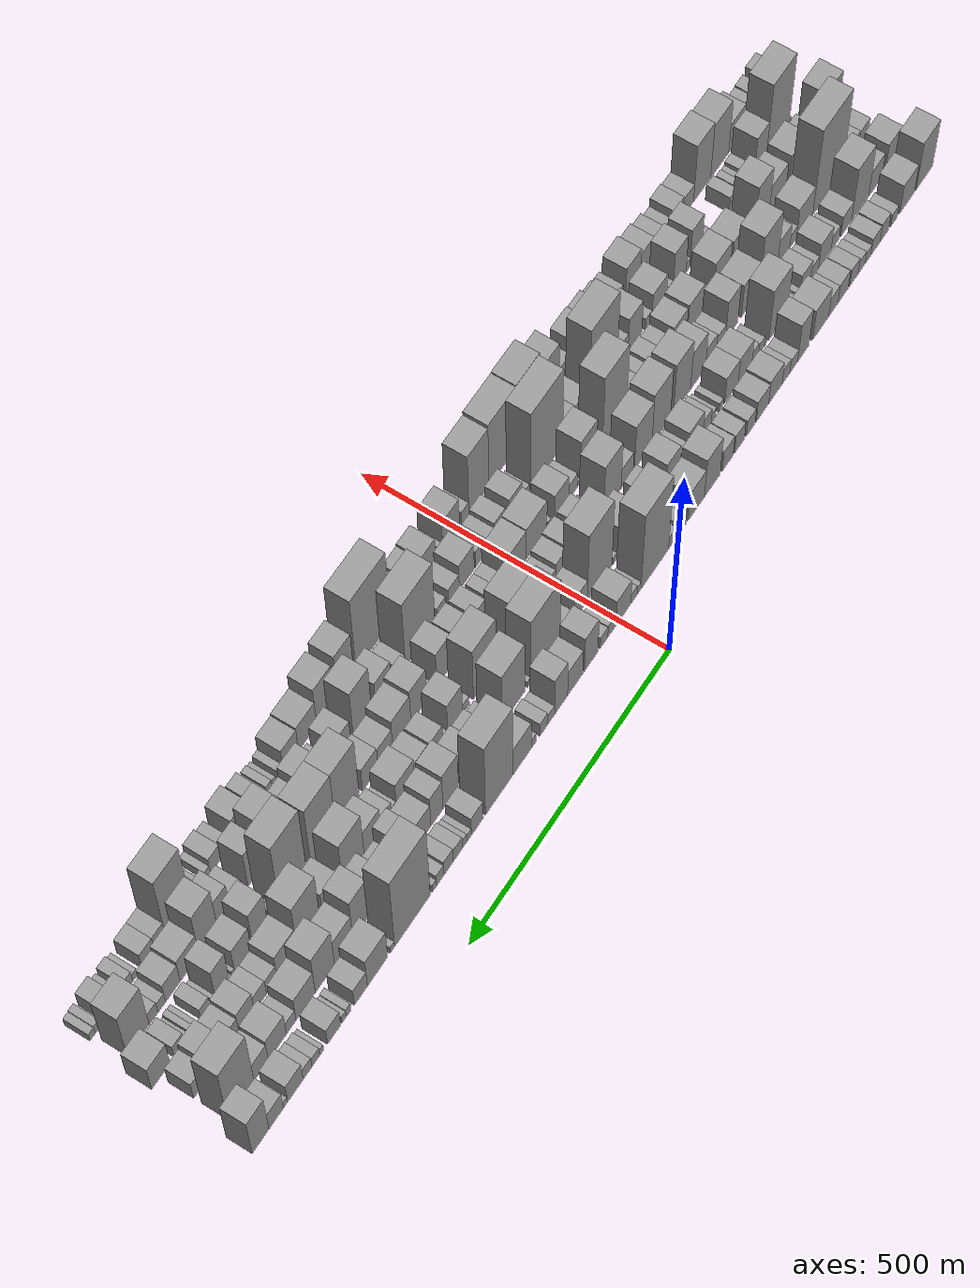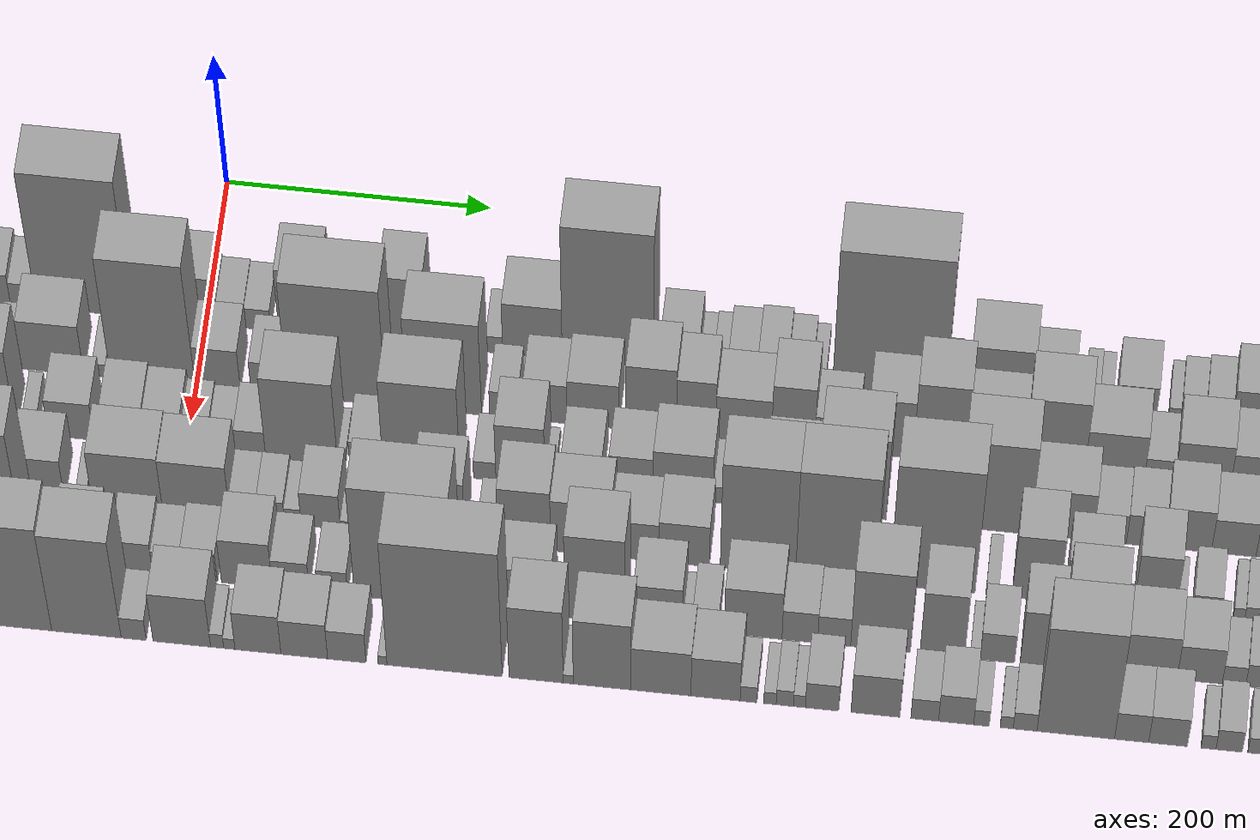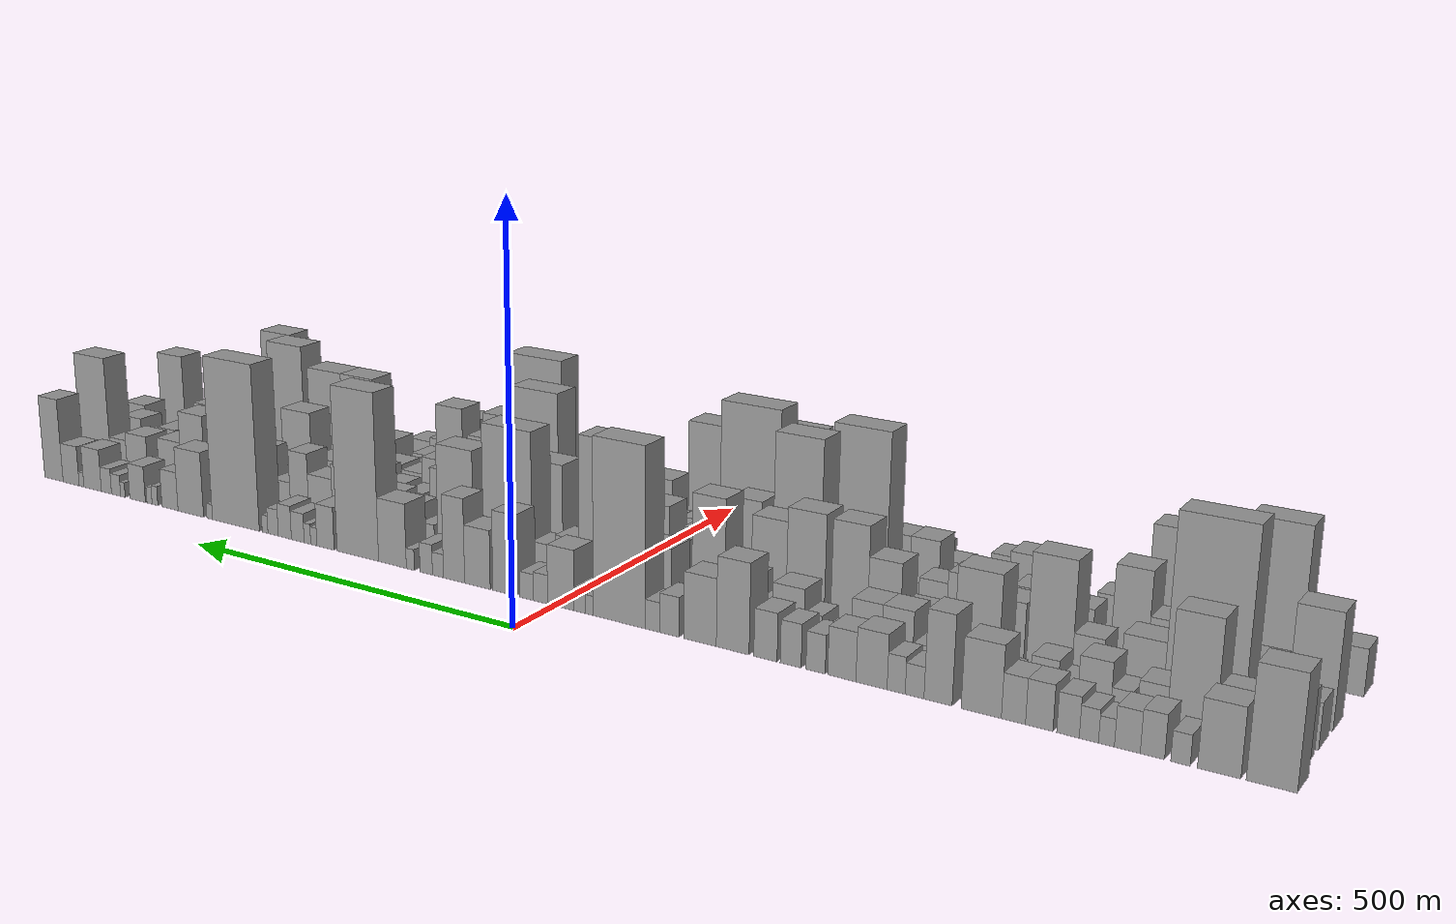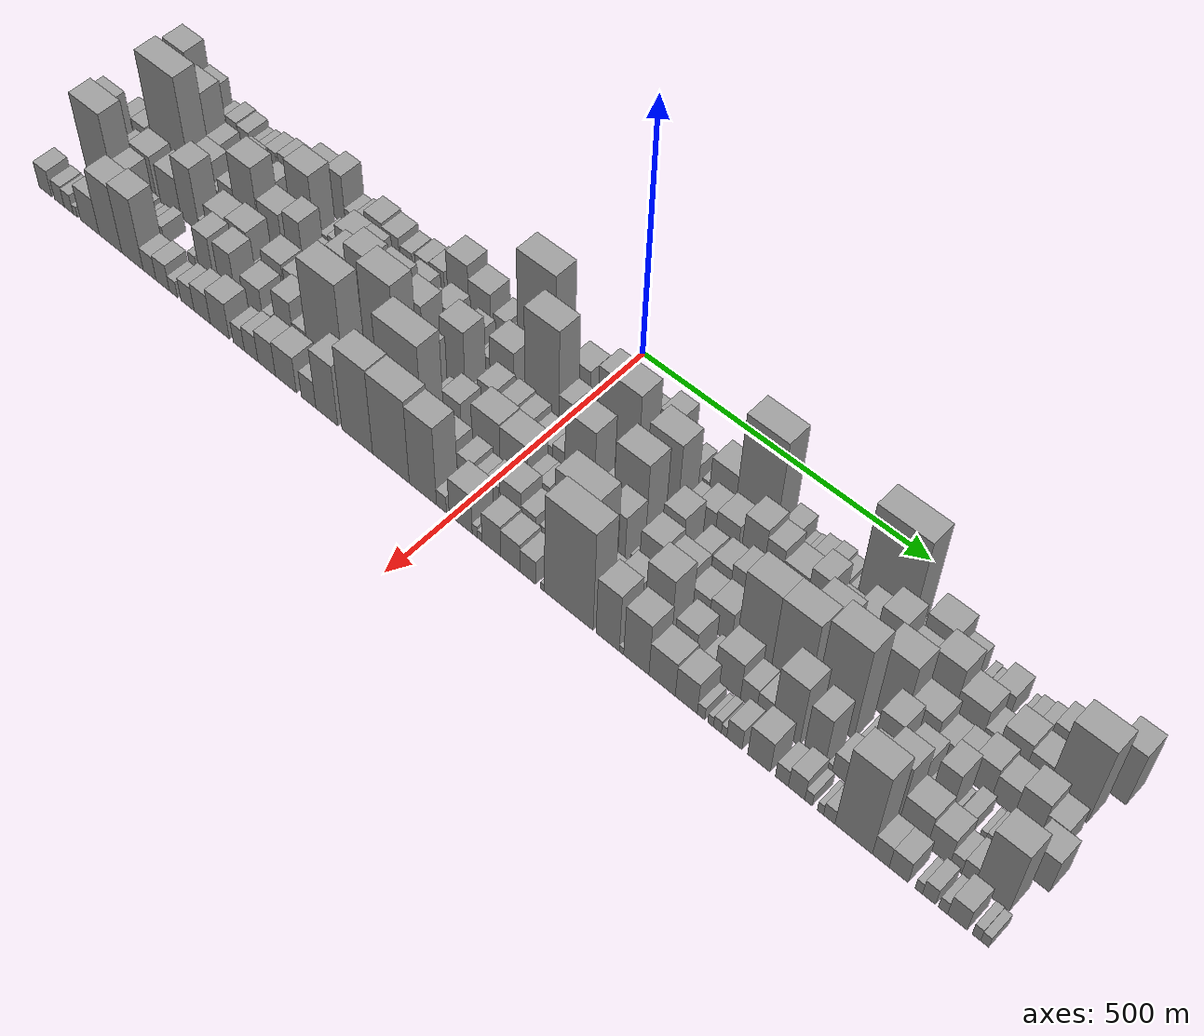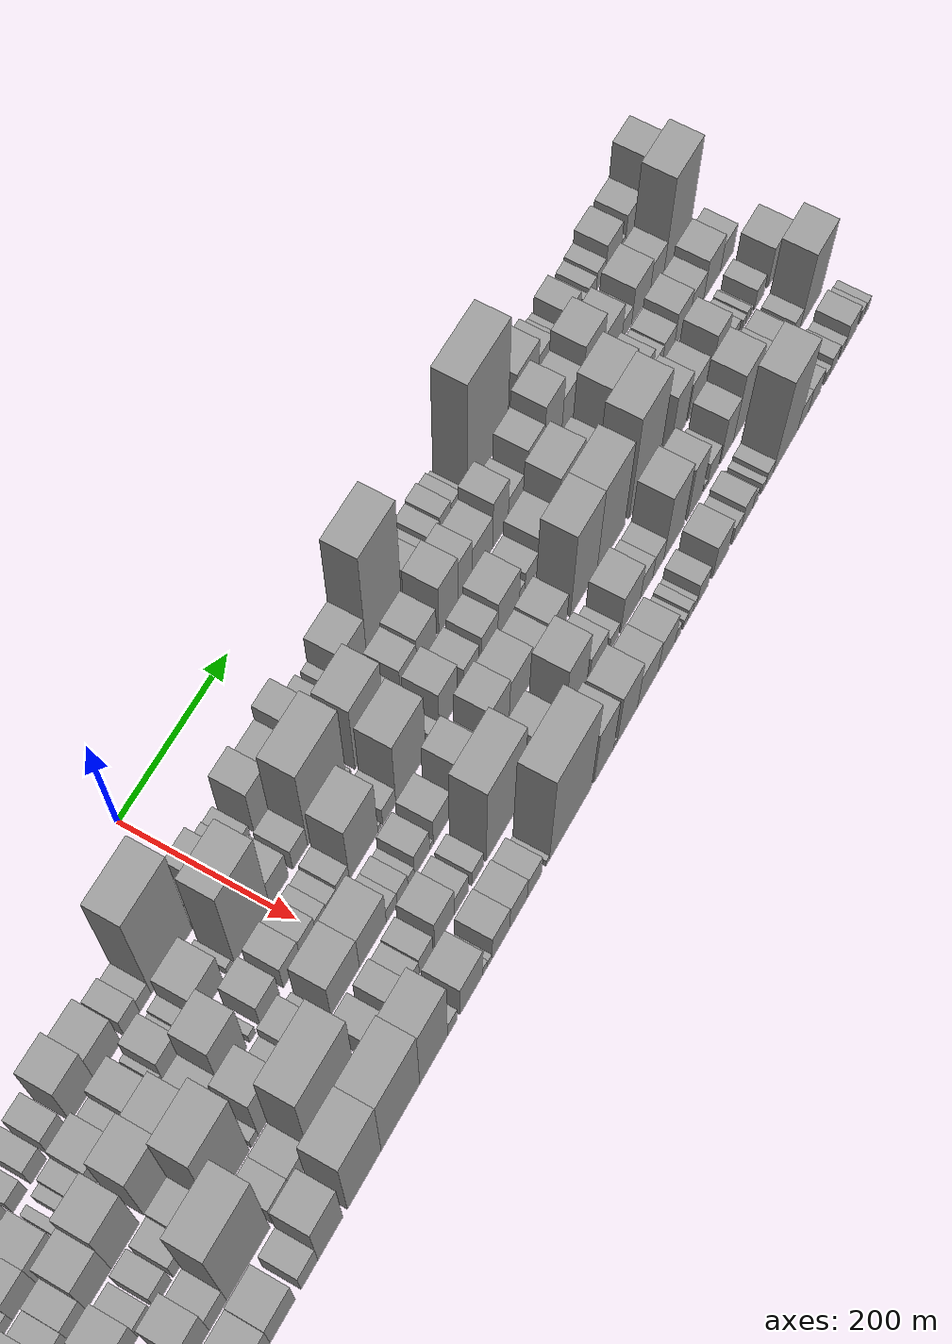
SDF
<sdf version="1.6">
 <world name="default">
  <scene>
   <sky><clouds><speed>12</speed></clouds></sky>
   <ambient>0.4 0.4 0.4 1</ambient>
   <background>0.7 0.7 0.7 1</background>
   <shadows>1</shadows>
  </scene>
  <gravity>0 0 -9.8066</gravity>
  <magnetic_field>6e-06 2.3e-05 -4.2e-05</magnetic_field>
  <physics default="0" name="default_physics" type="ode">
   <ode>
    <solver>
     <type>quick</type>
     <iters>10</iters>
     <sor>1.0</sor>
     <use_dynamic_moi_rescaling>0</use_dynamic_moi_rescaling>
    </solver>
    <constraints>
     <cfm>0</cfm>
     <erp>0.2</erp>
     <contact_max_correcting_vel>100</contact_max_correcting_vel>
     <contact_surface_layer>0.001</contact_surface_layer>
    </constraints>
   </ode>
   <max_step_size>0.004</max_step_size>
   <real_time_factor>1</real_time_factor>
   <real_time_update_rate>250</real_time_update_rate>
  </physics>
  <light name="sun" type="directional">
   <pose>0 0 10 0 0 0</pose>
   <diffuse>0.8 0.8 0.8 1</diffuse>
   <specular>0.2 0.2 0.2 1</specular>
   <attenuation>
    <range>1000</range>
    <constant>0.9</constant>
    <linear>0.01</linear>
    <quadratic>0.001</quadratic>
   </attenuation>
   <direction>-0.5 0.1 -0.9</direction>
  </light>
  <model name="building_1">
   <static>1</static>
   <pose>100.0000 -835.8675 0 0.000000 0.000000 0.000000</pose>
   <link name="link">
    <pose>0 0 61.50 0 0 0</pose>
    <collision name="collision"><geometry><box><size>40.0000 48.2651 123.0000</size></box></geometry></collision>
    <visual name="visual">
     <cast_shadows>0</cast_shadows>
     <geometry><box><size>40.0000 48.2651 123.0000</size></box></geometry>
     <material>
      <script>
       <uri>model://grey_wall/materials/scripts</uri>
       <uri>model://grey_wall/materials/textures</uri>
       <name>vrc/grey_wall</name>
      </script>
     </material>
    </visual>
   </link>
  </model>
  <model name="building_2">
   <static>1</static>
   <pose>100.0000 -785.6989 0 0.000000 0.000000 0.000000</pose>
   <link name="link">
    <pose>0 0 37.50 0 0 0</pose>
    <collision name="collision"><geometry><box><size>40.0000 42.0720 75.0000</size></box></geometry></collision>
    <visual name="visual">
     <cast_shadows>0</cast_shadows>
     <geometry><box><size>40.0000 42.0720 75.0000</size></box></geometry>
     <material>
      <script>
       <uri>model://grey_wall/materials/scripts</uri>
       <uri>model://grey_wall/materials/textures</uri>
       <name>vrc/grey_wall</name>
      </script>
     </material>
    </visual>
   </link>
  </model>
  <model name="building_3">
   <static>1</static>
   <pose>100.0000 -747.9911 0 0.000000 0.000000 0.000000</pose>
   <link name="link">
    <pose>0 0 16.50 0 0 0</pose>
    <collision name="collision"><geometry><box><size>40.0000 19.3437 33.0000</size></box></geometry></collision>
    <visual name="visual">
     <cast_shadows>0</cast_shadows>
     <geometry><box><size>40.0000 19.3437 33.0000</size></box></geometry>
     <material>
      <script>
       <uri>model://grey_wall/materials/scripts</uri>
       <uri>model://grey_wall/materials/textures</uri>
       <name>vrc/grey_wall</name>
      </script>
     </material>
    </visual>
   </link>
  </model>
  <model name="building_4">
   <static>1</static>
   <pose>100.0000 -720.0713 0 0.000000 0.000000 0.000000</pose>
   <link name="link">
    <pose>0 0 24.00 0 0 0</pose>
    <collision name="collision"><geometry><box><size>40.0000 24.4960 48.0000</size></box></geometry></collision>
    <visual name="visual">
     <cast_shadows>0</cast_shadows>
     <geometry><box><size>40.0000 24.4960 48.0000</size></box></geometry>
     <material>
      <script>
       <uri>model://grey_wall/materials/scripts</uri>
       <uri>model://grey_wall/materials/textures</uri>
       <name>vrc/grey_wall</name>
      </script>
     </material>
    </visual>
   </link>
  </model>
  <model name="building_5">
   <static>1</static>
   <pose>100.0000 -694.7094 0 0.000000 0.000000 0.000000</pose>
   <link name="link">
    <pose>0 0 22.50 0 0 0</pose>
    <collision name="collision"><geometry><box><size>40.0000 26.2278 45.0000</size></box></geometry></collision>
    <visual name="visual">
     <cast_shadows>0</cast_shadows>
     <geometry><box><size>40.0000 26.2278 45.0000</size></box></geometry>
     <material>
      <script>
       <uri>model://grey_wall/materials/scripts</uri>
       <uri>model://grey_wall/materials/textures</uri>
       <name>vrc/grey_wall</name>
      </script>
     </material>
    </visual>
   </link>
  </model>
  <model name="building_6">
   <static>1</static>
   <pose>100.0000 -673.3801 0 0.000000 0.000000 0.000000</pose>
   <link name="link">
    <pose>0 0 15.00 0 0 0</pose>
    <collision name="collision"><geometry><box><size>40.0000 16.4307 30.0000</size></box></geometry></collision>
    <visual name="visual">
     <cast_shadows>0</cast_shadows>
     <geometry><box><size>40.0000 16.4307 30.0000</size></box></geometry>
     <material>
      <script>
       <uri>model://grey_wall/materials/scripts</uri>
       <uri>model://grey_wall/materials/textures</uri>
       <name>vrc/grey_wall</name>
      </script>
     </material>
    </visual>
   </link>
  </model>
  <model name="building_7">
   <static>1</static>
   <pose>100.0000 -655.2093 0 0.000000 0.000000 0.000000</pose>
   <link name="link">
    <pose>0 0 18.00 0 0 0</pose>
    <collision name="collision"><geometry><box><size>40.0000 19.9109 36.0000</size></box></geometry></collision>
    <visual name="visual">
     <cast_shadows>0</cast_shadows>
     <geometry><box><size>40.0000 19.9109 36.0000</size></box></geometry>
     <material>
      <script>
       <uri>model://grey_wall/materials/scripts</uri>
       <uri>model://grey_wall/materials/textures</uri>
       <name>vrc/grey_wall</name>
      </script>
     </material>
    </visual>
   </link>
  </model>
  <model name="building_8">
   <static>1</static>
   <pose>100.0000 -633.3928 0 0.000000 0.000000 0.000000</pose>
   <link name="link">
    <pose>0 0 22.50 0 0 0</pose>
    <collision name="collision"><geometry><box><size>40.0000 23.7222 45.0000</size></box></geometry></collision>
    <visual name="visual">
     <cast_shadows>0</cast_shadows>
     <geometry><box><size>40.0000 23.7222 45.0000</size></box></geometry>
     <material>
      <script>
       <uri>model://grey_wall/materials/scripts</uri>
       <uri>model://grey_wall/materials/textures</uri>
       <name>vrc/grey_wall</name>
      </script>
     </material>
    </visual>
   </link>
  </model>
  <model name="building_9">
   <static>1</static>
   <pose>100.0000 -602.8302 0 0.000000 0.000000 0.000000</pose>
   <link name="link">
    <pose>0 0 25.50 0 0 0</pose>
    <collision name="collision"><geometry><box><size>40.0000 29.4031 51.0000</size></box></geometry></collision>
    <visual name="visual">
     <cast_shadows>0</cast_shadows>
     <geometry><box><size>40.0000 29.4031 51.0000</size></box></geometry>
     <material>
      <script>
       <uri>model://grey_wall/materials/scripts</uri>
       <uri>model://grey_wall/materials/textures</uri>
       <name>vrc/grey_wall</name>
      </script>
     </material>
    </visual>
   </link>
  </model>
  <model name="building_10">
   <static>1</static>
   <pose>100.0000 -575.0428 0 0.000000 0.000000 0.000000</pose>
   <link name="link">
    <pose>0 0 25.50 0 0 0</pose>
    <collision name="collision"><geometry><box><size>40.0000 26.1718 51.0000</size></box></geometry></collision>
    <visual name="visual">
     <cast_shadows>0</cast_shadows>
     <geometry><box><size>40.0000 26.1718 51.0000</size></box></geometry>
     <material>
      <script>
       <uri>model://grey_wall/materials/scripts</uri>
       <uri>model://grey_wall/materials/textures</uri>
       <name>vrc/grey_wall</name>
      </script>
     </material>
    </visual>
   </link>
  </model>
  <model name="building_11">
   <static>1</static>
   <pose>100.0000 -539.6976 0 0.000000 0.000000 0.000000</pose>
   <link name="link">
    <pose>0 0 40.50 0 0 0</pose>
    <collision name="collision"><geometry><box><size>40.0000 44.5184 81.0000</size></box></geometry></collision>
    <visual name="visual">
     <cast_shadows>0</cast_shadows>
     <geometry><box><size>40.0000 44.5184 81.0000</size></box></geometry>
     <material>
      <script>
       <uri>model://grey_wall/materials/scripts</uri>
       <uri>model://grey_wall/materials/textures</uri>
       <name>vrc/grey_wall</name>
      </script>
     </material>
    </visual>
   </link>
  </model>
  <model name="building_12">
   <static>1</static>
   <pose>100.0000 -491.4782 0 0.000000 0.000000 0.000000</pose>
   <link name="link">
    <pose>0 0 51.00 0 0 0</pose>
    <collision name="collision"><geometry><box><size>40.0000 31.9203 102.0000</size></box></geometry></collision>
    <visual name="visual">
     <cast_shadows>0</cast_shadows>
     <geometry><box><size>40.0000 31.9203 102.0000</size></box></geometry>
     <material>
      <script>
       <uri>model://grey_wall/materials/scripts</uri>
       <uri>model://grey_wall/materials/textures</uri>
       <name>vrc/grey_wall</name>
      </script>
     </material>
    </visual>
   </link>
  </model>
  <model name="building_13">
   <static>1</static>
   <pose>100.0000 -464.7341 0 0.000000 0.000000 0.000000</pose>
   <link name="link">
    <pose>0 0 18.00 0 0 0</pose>
    <collision name="collision"><geometry><box><size>40.0000 21.5680 36.0000</size></box></geometry></collision>
    <visual name="visual">
     <cast_shadows>0</cast_shadows>
     <geometry><box><size>40.0000 21.5680 36.0000</size></box></geometry>
     <material>
      <script>
       <uri>model://grey_wall/materials/scripts</uri>
       <uri>model://grey_wall/materials/textures</uri>
       <name>vrc/grey_wall</name>
      </script>
     </material>
    </visual>
   </link>
  </model>
  <model name="building_14">
   <static>1</static>
   <pose>100.0000 -443.4192 0 0.000000 0.000000 0.000000</pose>
   <link name="link">
    <pose>0 0 21.00 0 0 0</pose>
    <collision name="collision"><geometry><box><size>40.0000 21.0617 42.0000</size></box></geometry></collision>
    <visual name="visual">
     <cast_shadows>0</cast_shadows>
     <geometry><box><size>40.0000 21.0617 42.0000</size></box></geometry>
     <material>
      <script>
       <uri>model://grey_wall/materials/scripts</uri>
       <uri>model://grey_wall/materials/textures</uri>
       <name>vrc/grey_wall</name>
      </script>
     </material>
    </visual>
   </link>
  </model>
  <model name="building_15">
   <static>1</static>
   <pose>100.0000 -414.4768 0 0.000000 0.000000 0.000000</pose>
   <link name="link">
    <pose>0 0 31.50 0 0 0</pose>
    <collision name="collision"><geometry><box><size>40.0000 36.8232 63.0000</size></box></geometry></collision>
    <visual name="visual">
     <cast_shadows>0</cast_shadows>
     <geometry><box><size>40.0000 36.8232 63.0000</size></box></geometry>
     <material>
      <script>
       <uri>model://grey_wall/materials/scripts</uri>
       <uri>model://grey_wall/materials/textures</uri>
       <name>vrc/grey_wall</name>
      </script>
     </material>
    </visual>
   </link>
  </model>
  <model name="building_16">
   <static>1</static>
   <pose>100.0000 -379.1413 0 0.000000 0.000000 0.000000</pose>
   <link name="link">
    <pose>0 0 28.50 0 0 0</pose>
    <collision name="collision"><geometry><box><size>40.0000 33.8477 57.0000</size></box></geometry></collision>
    <visual name="visual">
     <cast_shadows>0</cast_shadows>
     <geometry><box><size>40.0000 33.8477 57.0000</size></box></geometry>
     <material>
      <script>
       <uri>model://grey_wall/materials/scripts</uri>
       <uri>model://grey_wall/materials/textures</uri>
       <name>vrc/grey_wall</name>
      </script>
     </material>
    </visual>
   </link>
  </model>
  <model name="building_17">
   <static>1</static>
   <pose>100.0000 -347.4632 0 0.000000 0.000000 0.000000</pose>
   <link name="link">
    <pose>0 0 22.50 0 0 0</pose>
    <collision name="collision"><geometry><box><size>40.0000 23.5085 45.0000</size></box></geometry></collision>
    <visual name="visual">
     <cast_shadows>0</cast_shadows>
     <geometry><box><size>40.0000 23.5085 45.0000</size></box></geometry>
     <material>
      <script>
       <uri>model://grey_wall/materials/scripts</uri>
       <uri>model://grey_wall/materials/textures</uri>
       <name>vrc/grey_wall</name>
      </script>
     </material>
    </visual>
   </link>
  </model>
  <model name="building_18">
   <static>1</static>
   <pose>100.0000 -316.7947 0 0.000000 0.000000 0.000000</pose>
   <link name="link">
    <pose>0 0 25.50 0 0 0</pose>
    <collision name="collision"><geometry><box><size>40.0000 25.8286 51.0000</size></box></geometry></collision>
    <visual name="visual">
     <cast_shadows>0</cast_shadows>
     <geometry><box><size>40.0000 25.8286 51.0000</size></box></geometry>
     <material>
      <script>
       <uri>model://grey_wall/materials/scripts</uri>
       <uri>model://grey_wall/materials/textures</uri>
       <name>vrc/grey_wall</name>
      </script>
     </material>
    </visual>
   </link>
  </model>
  <model name="building_19">
   <static>1</static>
   <pose>100.0000 -285.2485 0 0.000000 0.000000 0.000000</pose>
   <link name="link">
    <pose>0 0 28.50 0 0 0</pose>
    <collision name="collision"><geometry><box><size>40.0000 29.2637 57.0000</size></box></geometry></collision>
    <visual name="visual">
     <cast_shadows>0</cast_shadows>
     <geometry><box><size>40.0000 29.2637 57.0000</size></box></geometry>
     <material>
      <script>
       <uri>model://grey_wall/materials/scripts</uri>
       <uri>model://grey_wall/materials/textures</uri>
       <name>vrc/grey_wall</name>
      </script>
     </material>
    </visual>
   </link>
  </model>
  <model name="building_20">
   <static>1</static>
   <pose>100.0000 -243.5700 0 0.000000 0.000000 0.000000</pose>
   <link name="link">
    <pose>0 0 54.00 0 0 0</pose>
    <collision name="collision"><geometry><box><size>40.0000 42.0933 108.0000</size></box></geometry></collision>
    <visual name="visual">
     <cast_shadows>0</cast_shadows>
     <geometry><box><size>40.0000 42.0933 108.0000</size></box></geometry>
     <material>
      <script>
       <uri>model://grey_wall/materials/scripts</uri>
       <uri>model://grey_wall/materials/textures</uri>
       <name>vrc/grey_wall</name>
      </script>
     </material>
    </visual>
   </link>
  </model>
  <model name="building_21">
   <static>1</static>
   <pose>100.0000 -201.1396 0 0.000000 0.000000 0.000000</pose>
   <link name="link">
    <pose>0 0 40.50 0 0 0</pose>
    <collision name="collision"><geometry><box><size>40.0000 42.7674 81.0000</size></box></geometry></collision>
    <visual name="visual">
     <cast_shadows>0</cast_shadows>
     <geometry><box><size>40.0000 42.7674 81.0000</size></box></geometry>
     <material>
      <script>
       <uri>model://grey_wall/materials/scripts</uri>
       <uri>model://grey_wall/materials/textures</uri>
       <name>vrc/grey_wall</name>
      </script>
     </material>
    </visual>
   </link>
  </model>
  <model name="building_22">
   <static>1</static>
   <pose>100.0000 -160.5968 0 0.000000 0.000000 0.000000</pose>
   <link name="link">
    <pose>0 0 24.00 0 0 0</pose>
    <collision name="collision"><geometry><box><size>40.0000 26.3182 48.0000</size></box></geometry></collision>
    <visual name="visual">
     <cast_shadows>0</cast_shadows>
     <geometry><box><size>40.0000 26.3182 48.0000</size></box></geometry>
     <material>
      <script>
       <uri>model://grey_wall/materials/scripts</uri>
       <uri>model://grey_wall/materials/textures</uri>
       <name>vrc/grey_wall</name>
      </script>
     </material>
    </visual>
   </link>
  </model>
  <model name="building_23">
   <static>1</static>
   <pose>100.0000 -137.6014 0 0.000000 0.000000 0.000000</pose>
   <link name="link">
    <pose>0 0 18.00 0 0 0</pose>
    <collision name="collision"><geometry><box><size>40.0000 19.6725 36.0000</size></box></geometry></collision>
    <visual name="visual">
     <cast_shadows>0</cast_shadows>
     <geometry><box><size>40.0000 19.6725 36.0000</size></box></geometry>
     <material>
      <script>
       <uri>model://grey_wall/materials/scripts</uri>
       <uri>model://grey_wall/materials/textures</uri>
       <name>vrc/grey_wall</name>
      </script>
     </material>
    </visual>
   </link>
  </model>
  <model name="building_24">
   <static>1</static>
   <pose>100.0000 -91.9433 0 0.000000 0.000000 0.000000</pose>
   <link name="link">
    <pose>0 0 109.50 0 0 0</pose>
    <collision name="collision"><geometry><box><size>40.0000 71.6437 219.0000</size></box></geometry></collision>
    <visual name="visual">
     <cast_shadows>0</cast_shadows>
     <geometry><box><size>40.0000 71.6437 219.0000</size></box></geometry>
     <material>
      <script>
       <uri>model://grey_wall/materials/scripts</uri>
       <uri>model://grey_wall/materials/textures</uri>
       <name>vrc/grey_wall</name>
      </script>
     </material>
    </visual>
   </link>
  </model>
  <model name="building_25">
   <static>1</static>
   <pose>100.0000 -50.9003 0 0.000000 0.000000 0.000000</pose>
   <link name="link">
    <pose>0 0 12.00 0 0 0</pose>
    <collision name="collision"><geometry><box><size>40.0000 10.4422 24.0000</size></box></geometry></collision>
    <visual name="visual">
     <cast_shadows>0</cast_shadows>
     <geometry><box><size>40.0000 10.4422 24.0000</size></box></geometry>
     <material>
      <script>
       <uri>model://grey_wall/materials/scripts</uri>
       <uri>model://grey_wall/materials/textures</uri>
       <name>vrc/grey_wall</name>
      </script>
     </material>
    </visual>
   </link>
  </model>
  <model name="building_26">
   <static>1</static>
   <pose>100.0000 -37.4652 0 0.000000 0.000000 0.000000</pose>
   <link name="link">
    <pose>0 0 15.00 0 0 0</pose>
    <collision name="collision"><geometry><box><size>40.0000 16.4280 30.0000</size></box></geometry></collision>
    <visual name="visual">
     <cast_shadows>0</cast_shadows>
     <geometry><box><size>40.0000 16.4280 30.0000</size></box></geometry>
     <material>
      <script>
       <uri>model://grey_wall/materials/scripts</uri>
       <uri>model://grey_wall/materials/textures</uri>
       <name>vrc/grey_wall</name>
      </script>
     </material>
    </visual>
   </link>
  </model>
  <model name="building_27">
   <static>1</static>
   <pose>100.0000 -10.2353 0 0.000000 0.000000 0.000000</pose>
   <link name="link">
    <pose>0 0 37.50 0 0 0</pose>
    <collision name="collision"><geometry><box><size>40.0000 38.0316 75.0000</size></box></geometry></collision>
    <visual name="visual">
     <cast_shadows>0</cast_shadows>
     <geometry><box><size>40.0000 38.0316 75.0000</size></box></geometry>
     <material>
      <script>
       <uri>model://grey_wall/materials/scripts</uri>
       <uri>model://grey_wall/materials/textures</uri>
       <name>vrc/grey_wall</name>
      </script>
     </material>
    </visual>
   </link>
  </model>
  <model name="building_28">
   <static>1</static>
   <pose>100.0000 19.3150 0 0.000000 0.000000 0.000000</pose>
   <link name="link">
    <pose>0 0 18.00 0 0 0</pose>
    <collision name="collision"><geometry><box><size>40.0000 21.0690 36.0000</size></box></geometry></collision>
    <visual name="visual">
     <cast_shadows>0</cast_shadows>
     <geometry><box><size>40.0000 21.0690 36.0000</size></box></geometry>
     <material>
      <script>
       <uri>model://grey_wall/materials/scripts</uri>
       <uri>model://grey_wall/materials/textures</uri>
       <name>vrc/grey_wall</name>
      </script>
     </material>
    </visual>
   </link>
  </model>
  <model name="building_29">
   <static>1</static>
   <pose>100.0000 39.4453 0 0.000000 0.000000 0.000000</pose>
   <link name="link">
    <pose>0 0 16.50 0 0 0</pose>
    <collision name="collision"><geometry><box><size>40.0000 19.1917 33.0000</size></box></geometry></collision>
    <visual name="visual">
     <cast_shadows>0</cast_shadows>
     <geometry><box><size>40.0000 19.1917 33.0000</size></box></geometry>
     <material>
      <script>
       <uri>model://grey_wall/materials/scripts</uri>
       <uri>model://grey_wall/materials/textures</uri>
       <name>vrc/grey_wall</name>
      </script>
     </material>
    </visual>
   </link>
  </model>
  <model name="building_30">
   <static>1</static>
   <pose>100.0000 72.2070 0 0.000000 0.000000 0.000000</pose>
   <link name="link">
    <pose>0 0 51.00 0 0 0</pose>
    <collision name="collision"><geometry><box><size>40.0000 34.3316 102.0000</size></box></geometry></collision>
    <visual name="visual">
     <cast_shadows>0</cast_shadows>
     <geometry><box><size>40.0000 34.3316 102.0000</size></box></geometry>
     <material>
      <script>
       <uri>model://grey_wall/materials/scripts</uri>
       <uri>model://grey_wall/materials/textures</uri>
       <name>vrc/grey_wall</name>
      </script>
     </material>
    </visual>
   </link>
  </model>
  <model name="building_31">
   <static>1</static>
   <pose>100.0000 112.7792 0 0.000000 0.000000 0.000000</pose>
   <link name="link">
    <pose>0 0 37.50 0 0 0</pose>
    <collision name="collision"><geometry><box><size>40.0000 38.8129 75.0000</size></box></geometry></collision>
    <visual name="visual">
     <cast_shadows>0</cast_shadows>
     <geometry><box><size>40.0000 38.8129 75.0000</size></box></geometry>
     <material>
      <script>
       <uri>model://grey_wall/materials/scripts</uri>
       <uri>model://grey_wall/materials/textures</uri>
       <name>vrc/grey_wall</name>
      </script>
     </material>
    </visual>
   </link>
  </model>
  <model name="building_32">
   <static>1</static>
   <pose>100.0000 148.5087 0 0.000000 0.000000 0.000000</pose>
   <link name="link">
    <pose>0 0 54.00 0 0 0</pose>
    <collision name="collision"><geometry><box><size>40.0000 32.6460 108.0000</size></box></geometry></collision>
    <visual name="visual">
     <cast_shadows>0</cast_shadows>
     <geometry><box><size>40.0000 32.6460 108.0000</size></box></geometry>
     <material>
      <script>
       <uri>model://grey_wall/materials/scripts</uri>
       <uri>model://grey_wall/materials/textures</uri>
       <name>vrc/grey_wall</name>
      </script>
     </material>
    </visual>
   </link>
  </model>
  <model name="building_33">
   <static>1</static>
   <pose>100.0000 173.4542 0 0.000000 0.000000 0.000000</pose>
   <link name="link">
    <pose>0 0 15.00 0 0 0</pose>
    <collision name="collision"><geometry><box><size>40.0000 17.2449 30.0000</size></box></geometry></collision>
    <visual name="visual">
     <cast_shadows>0</cast_shadows>
     <geometry><box><size>40.0000 17.2449 30.0000</size></box></geometry>
     <material>
      <script>
       <uri>model://grey_wall/materials/scripts</uri>
       <uri>model://grey_wall/materials/textures</uri>
       <name>vrc/grey_wall</name>
      </script>
     </material>
    </visual>
   </link>
  </model>
  <model name="building_34">
   <static>1</static>
   <pose>100.0000 191.8668 0 0.000000 0.000000 0.000000</pose>
   <link name="link">
    <pose>0 0 19.50 0 0 0</pose>
    <collision name="collision"><geometry><box><size>40.0000 19.5803 39.0000</size></box></geometry></collision>
    <visual name="visual">
     <cast_shadows>0</cast_shadows>
     <geometry><box><size>40.0000 19.5803 39.0000</size></box></geometry>
     <material>
      <script>
       <uri>model://grey_wall/materials/scripts</uri>
       <uri>model://grey_wall/materials/textures</uri>
       <name>vrc/grey_wall</name>
      </script>
     </material>
    </visual>
   </link>
  </model>
  <model name="building_35">
   <static>1</static>
   <pose>100.0000 217.0242 0 0.000000 0.000000 0.000000</pose>
   <link name="link">
    <pose>0 0 13.50 0 0 0</pose>
    <collision name="collision"><geometry><box><size>40.0000 12.7344 27.0000</size></box></geometry></collision>
    <visual name="visual">
     <cast_shadows>0</cast_shadows>
     <geometry><box><size>40.0000 12.7344 27.0000</size></box></geometry>
     <material>
      <script>
       <uri>model://grey_wall/materials/scripts</uri>
       <uri>model://grey_wall/materials/textures</uri>
       <name>vrc/grey_wall</name>
      </script>
     </material>
    </visual>
   </link>
  </model>
  <model name="building_36">
   <static>1</static>
   <pose>100.0000 245.6946 0 0.000000 0.000000 0.000000</pose>
   <link name="link">
    <pose>0 0 42.00 0 0 0</pose>
    <collision name="collision"><geometry><box><size>40.0000 44.6065 84.0000</size></box></geometry></collision>
    <visual name="visual">
     <cast_shadows>0</cast_shadows>
     <geometry><box><size>40.0000 44.6065 84.0000</size></box></geometry>
     <material>
      <script>
       <uri>model://grey_wall/materials/scripts</uri>
       <uri>model://grey_wall/materials/textures</uri>
       <name>vrc/grey_wall</name>
      </script>
     </material>
    </visual>
   </link>
  </model>
  <model name="building_37">
   <static>1</static>
   <pose>100.0000 302.2115 0 0.000000 0.000000 0.000000</pose>
   <link name="link">
    <pose>0 0 109.50 0 0 0</pose>
    <collision name="collision"><geometry><box><size>40.0000 68.4273 219.0000</size></box></geometry></collision>
    <visual name="visual">
     <cast_shadows>0</cast_shadows>
     <geometry><box><size>40.0000 68.4273 219.0000</size></box></geometry>
     <material>
      <script>
       <uri>model://grey_wall/materials/scripts</uri>
       <uri>model://grey_wall/materials/textures</uri>
       <name>vrc/grey_wall</name>
      </script>
     </material>
    </visual>
   </link>
  </model>
  <model name="building_38">
   <static>1</static>
   <pose>100.0000 356.0403 0 0.000000 0.000000 0.000000</pose>
   <link name="link">
    <pose>0 0 28.50 0 0 0</pose>
    <collision name="collision"><geometry><box><size>40.0000 29.2303 57.0000</size></box></geometry></collision>
    <visual name="visual">
     <cast_shadows>0</cast_shadows>
     <geometry><box><size>40.0000 29.2303 57.0000</size></box></geometry>
     <material>
      <script>
       <uri>model://grey_wall/materials/scripts</uri>
       <uri>model://grey_wall/materials/textures</uri>
       <name>vrc/grey_wall</name>
      </script>
     </material>
    </visual>
   </link>
  </model>
  <model name="building_39">
   <static>1</static>
   <pose>100.0000 375.9039 0 0.000000 0.000000 0.000000</pose>
   <link name="link">
    <pose>0 0 12.00 0 0 0</pose>
    <collision name="collision"><geometry><box><size>40.0000 10.4968 24.0000</size></box></geometry></collision>
    <visual name="visual">
     <cast_shadows>0</cast_shadows>
     <geometry><box><size>40.0000 10.4968 24.0000</size></box></geometry>
     <material>
      <script>
       <uri>model://grey_wall/materials/scripts</uri>
       <uri>model://grey_wall/materials/textures</uri>
       <name>vrc/grey_wall</name>
      </script>
     </material>
    </visual>
   </link>
  </model>
  <model name="building_40">
   <static>1</static>
   <pose>100.0000 386.7250 0 0.000000 0.000000 0.000000</pose>
   <link name="link">
    <pose>0 0 13.50 0 0 0</pose>
    <collision name="collision"><geometry><box><size>40.0000 11.1454 27.0000</size></box></geometry></collision>
    <visual name="visual">
     <cast_shadows>0</cast_shadows>
     <geometry><box><size>40.0000 11.1454 27.0000</size></box></geometry>
     <material>
      <script>
       <uri>model://grey_wall/materials/scripts</uri>
       <uri>model://grey_wall/materials/textures</uri>
       <name>vrc/grey_wall</name>
      </script>
     </material>
    </visual>
   </link>
  </model>
  <model name="building_41">
   <static>1</static>
   <pose>100.0000 403.3421 0 0.000000 0.000000 0.000000</pose>
   <link name="link">
    <pose>0 0 19.50 0 0 0</pose>
    <collision name="collision"><geometry><box><size>40.0000 22.0888 39.0000</size></box></geometry></collision>
    <visual name="visual">
     <cast_shadows>0</cast_shadows>
     <geometry><box><size>40.0000 22.0888 39.0000</size></box></geometry>
     <material>
      <script>
       <uri>model://grey_wall/materials/scripts</uri>
       <uri>model://grey_wall/materials/textures</uri>
       <name>vrc/grey_wall</name>
      </script>
     </material>
    </visual>
   </link>
  </model>
  <model name="building_42">
   <static>1</static>
   <pose>100.0000 425.7299 0 0.000000 0.000000 0.000000</pose>
   <link name="link">
    <pose>0 0 22.50 0 0 0</pose>
    <collision name="collision"><geometry><box><size>40.0000 22.6869 45.0000</size></box></geometry></collision>
    <visual name="visual">
     <cast_shadows>0</cast_shadows>
     <geometry><box><size>40.0000 22.6869 45.0000</size></box></geometry>
     <material>
      <script>
       <uri>model://grey_wall/materials/scripts</uri>
       <uri>model://grey_wall/materials/textures</uri>
       <name>vrc/grey_wall</name>
      </script>
     </material>
    </visual>
   </link>
  </model>
  <model name="building_43">
   <static>1</static>
   <pose>100.0000 446.2108 0 0.000000 0.000000 0.000000</pose>
   <link name="link">
    <pose>0 0 18.00 0 0 0</pose>
    <collision name="collision"><geometry><box><size>40.0000 18.2748 36.0000</size></box></geometry></collision>
    <visual name="visual">
     <cast_shadows>0</cast_shadows>
     <geometry><box><size>40.0000 18.2748 36.0000</size></box></geometry>
     <material>
      <script>
       <uri>model://grey_wall/materials/scripts</uri>
       <uri>model://grey_wall/materials/textures</uri>
       <name>vrc/grey_wall</name>
      </script>
     </material>
    </visual>
   </link>
  </model>
  <model name="building_44">
   <static>1</static>
   <pose>100.0000 460.3603 0 0.000000 0.000000 0.000000</pose>
   <link name="link">
    <pose>0 0 12.00 0 0 0</pose>
    <collision name="collision"><geometry><box><size>40.0000 10.0242 24.0000</size></box></geometry></collision>
    <visual name="visual">
     <cast_shadows>0</cast_shadows>
     <geometry><box><size>40.0000 10.0242 24.0000</size></box></geometry>
     <material>
      <script>
       <uri>model://grey_wall/materials/scripts</uri>
       <uri>model://grey_wall/materials/textures</uri>
       <name>vrc/grey_wall</name>
      </script>
     </material>
    </visual>
   </link>
  </model>
  <model name="building_45">
   <static>1</static>
   <pose>100.0000 512.6496 0 0.000000 0.000000 0.000000</pose>
   <link name="link">
    <pose>0 0 112.50 0 0 0</pose>
    <collision name="collision"><geometry><box><size>40.0000 84.5545 225.0000</size></box></geometry></collision>
    <visual name="visual">
     <cast_shadows>0</cast_shadows>
     <geometry><box><size>40.0000 84.5545 225.0000</size></box></geometry>
     <material>
      <script>
       <uri>model://grey_wall/materials/scripts</uri>
       <uri>model://grey_wall/materials/textures</uri>
       <name>vrc/grey_wall</name>
      </script>
     </material>
    </visual>
   </link>
  </model>
  <model name="building_46">
   <static>1</static>
   <pose>100.0000 560.1286 0 0.000000 0.000000 0.000000</pose>
   <link name="link">
    <pose>0 0 10.50 0 0 0</pose>
    <collision name="collision"><geometry><box><size>40.0000 10.4033 21.0000</size></box></geometry></collision>
    <visual name="visual">
     <cast_shadows>0</cast_shadows>
     <geometry><box><size>40.0000 10.4033 21.0000</size></box></geometry>
     <material>
      <script>
       <uri>model://grey_wall/materials/scripts</uri>
       <uri>model://grey_wall/materials/textures</uri>
       <name>vrc/grey_wall</name>
      </script>
     </material>
    </visual>
   </link>
  </model>
  <model name="building_47">
   <static>1</static>
   <pose>100.0000 595.1719 0 0.000000 0.000000 0.000000</pose>
   <link name="link">
    <pose>0 0 45.00 0 0 0</pose>
    <collision name="collision"><geometry><box><size>40.0000 47.6834 90.0000</size></box></geometry></collision>
    <visual name="visual">
     <cast_shadows>0</cast_shadows>
     <geometry><box><size>40.0000 47.6834 90.0000</size></box></geometry>
     <material>
      <script>
       <uri>model://grey_wall/materials/scripts</uri>
       <uri>model://grey_wall/materials/textures</uri>
       <name>vrc/grey_wall</name>
      </script>
     </material>
    </visual>
   </link>
  </model>
  <model name="building_48">
   <static>1</static>
   <pose>100.0000 634.2060 0 0.000000 0.000000 0.000000</pose>
   <link name="link">
    <pose>0 0 27.00 0 0 0</pose>
    <collision name="collision"><geometry><box><size>40.0000 30.3847 54.0000</size></box></geometry></collision>
    <visual name="visual">
     <cast_shadows>0</cast_shadows>
     <geometry><box><size>40.0000 30.3847 54.0000</size></box></geometry>
     <material>
      <script>
       <uri>model://grey_wall/materials/scripts</uri>
       <uri>model://grey_wall/materials/textures</uri>
       <name>vrc/grey_wall</name>
      </script>
     </material>
    </visual>
   </link>
  </model>
  <model name="building_49">
   <static>1</static>
   <pose>100.0000 662.9370 0 0.000000 0.000000 0.000000</pose>
   <link name="link">
    <pose>0 0 13.50 0 0 0</pose>
    <collision name="collision"><geometry><box><size>40.0000 11.0773 27.0000</size></box></geometry></collision>
    <visual name="visual">
     <cast_shadows>0</cast_shadows>
     <geometry><box><size>40.0000 11.0773 27.0000</size></box></geometry>
     <material>
      <script>
       <uri>model://grey_wall/materials/scripts</uri>
       <uri>model://grey_wall/materials/textures</uri>
       <name>vrc/grey_wall</name>
      </script>
     </material>
    </visual>
   </link>
  </model>
  <model name="building_50">
   <static>1</static>
   <pose>100.0000 673.3901 0 0.000000 0.000000 0.000000</pose>
   <link name="link">
    <pose>0 0 12.00 0 0 0</pose>
    <collision name="collision"><geometry><box><size>40.0000 9.8288 24.0000</size></box></geometry></collision>
    <visual name="visual">
     <cast_shadows>0</cast_shadows>
     <geometry><box><size>40.0000 9.8288 24.0000</size></box></geometry>
     <material>
      <script>
       <uri>model://grey_wall/materials/scripts</uri>
       <uri>model://grey_wall/materials/textures</uri>
       <name>vrc/grey_wall</name>
      </script>
     </material>
    </visual>
   </link>
  </model>
  <model name="building_51">
   <static>1</static>
   <pose>100.0000 696.4857 0 0.000000 0.000000 0.000000</pose>
   <link name="link">
    <pose>0 0 25.50 0 0 0</pose>
    <collision name="collision"><geometry><box><size>40.0000 30.3625 51.0000</size></box></geometry></collision>
    <visual name="visual">
     <cast_shadows>0</cast_shadows>
     <geometry><box><size>40.0000 30.3625 51.0000</size></box></geometry>
     <material>
      <script>
       <uri>model://grey_wall/materials/scripts</uri>
       <uri>model://grey_wall/materials/textures</uri>
       <name>vrc/grey_wall</name>
      </script>
     </material>
    </visual>
   </link>
  </model>
  <model name="building_52">
   <static>1</static>
   <pose>100.0000 725.1748 0 0.000000 0.000000 0.000000</pose>
   <link name="link">
    <pose>0 0 10.50 0 0 0</pose>
    <collision name="collision"><geometry><box><size>40.0000 9.0157 21.0000</size></box></geometry></collision>
    <visual name="visual">
     <cast_shadows>0</cast_shadows>
     <geometry><box><size>40.0000 9.0157 21.0000</size></box></geometry>
     <material>
      <script>
       <uri>model://grey_wall/materials/scripts</uri>
       <uri>model://grey_wall/materials/textures</uri>
       <name>vrc/grey_wall</name>
      </script>
     </material>
    </visual>
   </link>
  </model>
  <model name="building_53">
   <static>1</static>
   <pose>100.0000 738.6402 0 0.000000 0.000000 0.000000</pose>
   <link name="link">
    <pose>0 0 15.00 0 0 0</pose>
    <collision name="collision"><geometry><box><size>40.0000 17.9151 30.0000</size></box></geometry></collision>
    <visual name="visual">
     <cast_shadows>0</cast_shadows>
     <geometry><box><size>40.0000 17.9151 30.0000</size></box></geometry>
     <material>
      <script>
       <uri>model://grey_wall/materials/scripts</uri>
       <uri>model://grey_wall/materials/textures</uri>
       <name>vrc/grey_wall</name>
      </script>
     </material>
    </visual>
   </link>
  </model>
  <model name="building_54">
   <static>1</static>
   <pose>100.0000 757.6617 0 0.000000 0.000000 0.000000</pose>
   <link name="link">
    <pose>0 0 18.00 0 0 0</pose>
    <collision name="collision"><geometry><box><size>40.0000 20.1278 36.0000</size></box></geometry></collision>
    <visual name="visual">
     <cast_shadows>0</cast_shadows>
     <geometry><box><size>40.0000 20.1278 36.0000</size></box></geometry>
     <material>
      <script>
       <uri>model://grey_wall/materials/scripts</uri>
       <uri>model://grey_wall/materials/textures</uri>
       <name>vrc/grey_wall</name>
      </script>
     </material>
    </visual>
   </link>
  </model>
  <model name="building_55">
   <static>1</static>
   <pose>100.0000 785.3259 0 0.000000 0.000000 0.000000</pose>
   <link name="link">
    <pose>0 0 30.00 0 0 0</pose>
    <collision name="collision"><geometry><box><size>40.0000 35.2008 60.0000</size></box></geometry></collision>
    <visual name="visual">
     <cast_shadows>0</cast_shadows>
     <geometry><box><size>40.0000 35.2008 60.0000</size></box></geometry>
     <material>
      <script>
       <uri>model://grey_wall/materials/scripts</uri>
       <uri>model://grey_wall/materials/textures</uri>
       <name>vrc/grey_wall</name>
      </script>
     </material>
    </visual>
   </link>
  </model>
  <model name="building_56">
   <static>1</static>
   <pose>100.0000 807.7318 0 0.000000 0.000000 0.000000</pose>
   <link name="link">
    <pose>0 0 10.50 0 0 0</pose>
    <collision name="collision"><geometry><box><size>40.0000 9.6110 21.0000</size></box></geometry></collision>
    <visual name="visual">
     <cast_shadows>0</cast_shadows>
     <geometry><box><size>40.0000 9.6110 21.0000</size></box></geometry>
     <material>
      <script>
       <uri>model://grey_wall/materials/scripts</uri>
       <uri>model://grey_wall/materials/textures</uri>
       <name>vrc/grey_wall</name>
      </script>
     </material>
    </visual>
   </link>
  </model>
  <model name="building_57">
   <static>1</static>
   <pose>100.0000 828.9677 0 0.000000 0.000000 0.000000</pose>
   <link name="link">
    <pose>0 0 28.50 0 0 0</pose>
    <collision name="collision"><geometry><box><size>40.0000 32.8608 57.0000</size></box></geometry></collision>
    <visual name="visual">
     <cast_shadows>0</cast_shadows>
     <geometry><box><size>40.0000 32.8608 57.0000</size></box></geometry>
     <material>
      <script>
       <uri>model://grey_wall/materials/scripts</uri>
       <uri>model://grey_wall/materials/textures</uri>
       <name>vrc/grey_wall</name>
      </script>
     </material>
    </visual>
   </link>
  </model>
  <model name="building_58">
   <static>1</static>
   <pose>100.0000 864.2887 0 0.000000 0.000000 0.000000</pose>
   <link name="link">
    <pose>0 0 60.00 0 0 0</pose>
    <collision name="collision"><geometry><box><size>40.0000 37.7812 120.0000</size></box></geometry></collision>
    <visual name="visual">
     <cast_shadows>0</cast_shadows>
     <geometry><box><size>40.0000 37.7812 120.0000</size></box></geometry>
     <material>
      <script>
       <uri>model://grey_wall/materials/scripts</uri>
       <uri>model://grey_wall/materials/textures</uri>
       <name>vrc/grey_wall</name>
      </script>
     </material>
    </visual>
   </link>
  </model>
  <model name="building_59">
   <static>1</static>
   <pose>152.0000 -832.2248 0 0.000000 0.000000 0.000000</pose>
   <link name="link">
    <pose>0 0 37.50 0 0 0</pose>
    <collision name="collision"><geometry><box><size>40.0000 39.5504 75.0000</size></box></geometry></collision>
    <visual name="visual">
     <cast_shadows>0</cast_shadows>
     <geometry><box><size>40.0000 39.5504 75.0000</size></box></geometry>
     <material>
      <script>
       <uri>model://grey_wall/materials/scripts</uri>
       <uri>model://grey_wall/materials/textures</uri>
       <name>vrc/grey_wall</name>
      </script>
     </material>
    </visual>
   </link>
  </model>
  <model name="building_60">
   <static>1</static>
   <pose>152.0000 -784.2301 0 0.000000 0.000000 0.000000</pose>
   <link name="link">
    <pose>0 0 33.00 0 0 0</pose>
    <collision name="collision"><geometry><box><size>40.0000 38.4390 66.0000</size></box></geometry></collision>
    <visual name="visual">
     <cast_shadows>0</cast_shadows>
     <geometry><box><size>40.0000 38.4390 66.0000</size></box></geometry>
     <material>
      <script>
       <uri>model://grey_wall/materials/scripts</uri>
       <uri>model://grey_wall/materials/textures</uri>
       <name>vrc/grey_wall</name>
      </script>
     </material>
    </visual>
   </link>
  </model>
  <model name="building_61">
   <static>1</static>
   <pose>152.0000 -740.5774 0 0.000000 0.000000 0.000000</pose>
   <link name="link">
    <pose>0 0 69.00 0 0 0</pose>
    <collision name="collision"><geometry><box><size>40.0000 48.8663 138.0000</size></box></geometry></collision>
    <visual name="visual">
     <cast_shadows>0</cast_shadows>
     <geometry><box><size>40.0000 48.8663 138.0000</size></box></geometry>
     <material>
      <script>
       <uri>model://grey_wall/materials/scripts</uri>
       <uri>model://grey_wall/materials/textures</uri>
       <name>vrc/grey_wall</name>
      </script>
     </material>
    </visual>
   </link>
  </model>
  <model name="building_62">
   <static>1</static>
   <pose>152.0000 -700.9382 0 0.000000 0.000000 0.000000</pose>
   <link name="link">
    <pose>0 0 27.00 0 0 0</pose>
    <collision name="collision"><geometry><box><size>40.0000 30.4121 54.0000</size></box></geometry></collision>
    <visual name="visual">
     <cast_shadows>0</cast_shadows>
     <geometry><box><size>40.0000 30.4121 54.0000</size></box></geometry>
     <material>
      <script>
       <uri>model://grey_wall/materials/scripts</uri>
       <uri>model://grey_wall/materials/textures</uri>
       <name>vrc/grey_wall</name>
      </script>
     </material>
    </visual>
   </link>
  </model>
  <model name="building_63">
   <static>1</static>
   <pose>152.0000 -669.3956 0 0.000000 0.000000 0.000000</pose>
   <link name="link">
    <pose>0 0 19.50 0 0 0</pose>
    <collision name="collision"><geometry><box><size>40.0000 22.6730 39.0000</size></box></geometry></collision>
    <visual name="visual">
     <cast_shadows>0</cast_shadows>
     <geometry><box><size>40.0000 22.6730 39.0000</size></box></geometry>
     <material>
      <script>
       <uri>model://grey_wall/materials/scripts</uri>
       <uri>model://grey_wall/materials/textures</uri>
       <name>vrc/grey_wall</name>
      </script>
     </material>
    </visual>
   </link>
  </model>
  <model name="building_64">
   <static>1</static>
   <pose>152.0000 -640.3801 0 0.000000 0.000000 0.000000</pose>
   <link name="link">
    <pose>0 0 33.00 0 0 0</pose>
    <collision name="collision"><geometry><box><size>40.0000 35.3580 66.0000</size></box></geometry></collision>
    <visual name="visual">
     <cast_shadows>0</cast_shadows>
     <geometry><box><size>40.0000 35.3580 66.0000</size></box></geometry>
     <material>
      <script>
       <uri>model://grey_wall/materials/scripts</uri>
       <uri>model://grey_wall/materials/textures</uri>
       <name>vrc/grey_wall</name>
      </script>
     </material>
    </visual>
   </link>
  </model>
  <model name="building_65">
   <static>1</static>
   <pose>152.0000 -612.0106 0 0.000000 0.000000 0.000000</pose>
   <link name="link">
    <pose>0 0 18.00 0 0 0</pose>
    <collision name="collision"><geometry><box><size>40.0000 21.3810 36.0000</size></box></geometry></collision>
    <visual name="visual">
     <cast_shadows>0</cast_shadows>
     <geometry><box><size>40.0000 21.3810 36.0000</size></box></geometry>
     <material>
      <script>
       <uri>model://grey_wall/materials/scripts</uri>
       <uri>model://grey_wall/materials/textures</uri>
       <name>vrc/grey_wall</name>
      </script>
     </material>
    </visual>
   </link>
  </model>
  <model name="building_66">
   <static>1</static>
   <pose>152.0000 -586.1350 0 0.000000 0.000000 0.000000</pose>
   <link name="link">
    <pose>0 0 27.00 0 0 0</pose>
    <collision name="collision"><geometry><box><size>40.0000 30.3704 54.0000</size></box></geometry></collision>
    <visual name="visual">
     <cast_shadows>0</cast_shadows>
     <geometry><box><size>40.0000 30.3704 54.0000</size></box></geometry>
     <material>
      <script>
       <uri>model://grey_wall/materials/scripts</uri>
       <uri>model://grey_wall/materials/textures</uri>
       <name>vrc/grey_wall</name>
      </script>
     </material>
    </visual>
   </link>
  </model>
  <model name="building_67">
   <static>1</static>
   <pose>152.0000 -565.7380 0 0.000000 0.000000 0.000000</pose>
   <link name="link">
    <pose>0 0 10.50 0 0 0</pose>
    <collision name="collision"><geometry><box><size>40.0000 10.4235 21.0000</size></box></geometry></collision>
    <visual name="visual">
     <cast_shadows>0</cast_shadows>
     <geometry><box><size>40.0000 10.4235 21.0000</size></box></geometry>
     <material>
      <script>
       <uri>model://grey_wall/materials/scripts</uri>
       <uri>model://grey_wall/materials/textures</uri>
       <name>vrc/grey_wall</name>
      </script>
     </material>
    </visual>
   </link>
  </model>
  <model name="building_68">
   <static>1</static>
   <pose>152.0000 -556.4889 0 0.000000 0.000000 0.000000</pose>
   <link name="link">
    <pose>0 0 9.00 0 0 0</pose>
    <collision name="collision"><geometry><box><size>40.0000 8.0748 18.0000</size></box></geometry></collision>
    <visual name="visual">
     <cast_shadows>0</cast_shadows>
     <geometry><box><size>40.0000 8.0748 18.0000</size></box></geometry>
     <material>
      <script>
       <uri>model://grey_wall/materials/scripts</uri>
       <uri>model://grey_wall/materials/textures</uri>
       <name>vrc/grey_wall</name>
      </script>
     </material>
    </visual>
   </link>
  </model>
  <model name="building_69">
   <static>1</static>
   <pose>152.0000 -543.8938 0 0.000000 0.000000 0.000000</pose>
   <link name="link">
    <pose>0 0 15.00 0 0 0</pose>
    <collision name="collision"><geometry><box><size>40.0000 17.1153 30.0000</size></box></geometry></collision>
    <visual name="visual">
     <cast_shadows>0</cast_shadows>
     <geometry><box><size>40.0000 17.1153 30.0000</size></box></geometry>
     <material>
      <script>
       <uri>model://grey_wall/materials/scripts</uri>
       <uri>model://grey_wall/materials/textures</uri>
       <name>vrc/grey_wall</name>
      </script>
     </material>
    </visual>
   </link>
  </model>
  <model name="building_70">
   <static>1</static>
   <pose>152.0000 -509.8802 0 0.000000 0.000000 0.000000</pose>
   <link name="link">
    <pose>0 0 67.50 0 0 0</pose>
    <collision name="collision"><geometry><box><size>40.0000 50.9121 135.0000</size></box></geometry></collision>
    <visual name="visual">
     <cast_shadows>0</cast_shadows>
     <geometry><box><size>40.0000 50.9121 135.0000</size></box></geometry>
     <material>
      <script>
       <uri>model://grey_wall/materials/scripts</uri>
       <uri>model://grey_wall/materials/textures</uri>
       <name>vrc/grey_wall</name>
      </script>
     </material>
    </visual>
   </link>
  </model>
  <model name="building_71">
   <static>1</static>
   <pose>152.0000 -474.4227 0 0.000000 0.000000 0.000000</pose>
   <link name="link">
    <pose>0 0 7.50 0 0 0</pose>
    <collision name="collision"><geometry><box><size>40.0000 6.0027 15.0000</size></box></geometry></collision>
    <visual name="visual">
     <cast_shadows>0</cast_shadows>
     <geometry><box><size>40.0000 6.0027 15.0000</size></box></geometry>
     <material>
      <script>
       <uri>model://grey_wall/materials/scripts</uri>
       <uri>model://grey_wall/materials/textures</uri>
       <name>vrc/grey_wall</name>
      </script>
     </material>
    </visual>
   </link>
  </model>
  <model name="building_72">
   <static>1</static>
   <pose>152.0000 -463.4967 0 0.000000 0.000000 0.000000</pose>
   <link name="link">
    <pose>0 0 15.00 0 0 0</pose>
    <collision name="collision"><geometry><box><size>40.0000 15.8494 30.0000</size></box></geometry></collision>
    <visual name="visual">
     <cast_shadows>0</cast_shadows>
     <geometry><box><size>40.0000 15.8494 30.0000</size></box></geometry>
     <material>
      <script>
       <uri>model://grey_wall/materials/scripts</uri>
       <uri>model://grey_wall/materials/textures</uri>
       <name>vrc/grey_wall</name>
      </script>
     </material>
    </visual>
   </link>
  </model>
  <model name="building_73">
   <static>1</static>
   <pose>152.0000 -446.4558 0 0.000000 0.000000 0.000000</pose>
   <link name="link">
    <pose>0 0 18.00 0 0 0</pose>
    <collision name="collision"><geometry><box><size>40.0000 18.2323 36.0000</size></box></geometry></collision>
    <visual name="visual">
     <cast_shadows>0</cast_shadows>
     <geometry><box><size>40.0000 18.2323 36.0000</size></box></geometry>
     <material>
      <script>
       <uri>model://grey_wall/materials/scripts</uri>
       <uri>model://grey_wall/materials/textures</uri>
       <name>vrc/grey_wall</name>
      </script>
     </material>
    </visual>
   </link>
  </model>
  <model name="building_74">
   <static>1</static>
   <pose>152.0000 -418.7842 0 0.000000 0.000000 0.000000</pose>
   <link name="link">
    <pose>0 0 36.00 0 0 0</pose>
    <collision name="collision"><geometry><box><size>40.0000 37.1108 72.0000</size></box></geometry></collision>
    <visual name="visual">
     <cast_shadows>0</cast_shadows>
     <geometry><box><size>40.0000 37.1108 72.0000</size></box></geometry>
     <material>
      <script>
       <uri>model://grey_wall/materials/scripts</uri>
       <uri>model://grey_wall/materials/textures</uri>
       <name>vrc/grey_wall</name>
      </script>
     </material>
    </visual>
   </link>
  </model>
  <model name="building_75">
   <static>1</static>
   <pose>152.0000 -381.7975 0 0.000000 0.000000 0.000000</pose>
   <link name="link">
    <pose>0 0 36.00 0 0 0</pose>
    <collision name="collision"><geometry><box><size>40.0000 36.8627 72.0000</size></box></geometry></collision>
    <visual name="visual">
     <cast_shadows>0</cast_shadows>
     <geometry><box><size>40.0000 36.8627 72.0000</size></box></geometry>
     <material>
      <script>
       <uri>model://grey_wall/materials/scripts</uri>
       <uri>model://grey_wall/materials/textures</uri>
       <name>vrc/grey_wall</name>
      </script>
     </material>
    </visual>
   </link>
  </model>
  <model name="building_76">
   <static>1</static>
   <pose>152.0000 -353.9044 0 0.000000 0.000000 0.000000</pose>
   <link name="link">
    <pose>0 0 12.00 0 0 0</pose>
    <collision name="collision"><geometry><box><size>40.0000 10.9236 24.0000</size></box></geometry></collision>
    <visual name="visual">
     <cast_shadows>0</cast_shadows>
     <geometry><box><size>40.0000 10.9236 24.0000</size></box></geometry>
     <material>
      <script>
       <uri>model://grey_wall/materials/scripts</uri>
       <uri>model://grey_wall/materials/textures</uri>
       <name>vrc/grey_wall</name>
      </script>
     </material>
    </visual>
   </link>
  </model>
  <model name="building_77">
   <static>1</static>
   <pose>152.0000 -333.8802 0 0.000000 0.000000 0.000000</pose>
   <link name="link">
    <pose>0 0 13.50 0 0 0</pose>
    <collision name="collision"><geometry><box><size>40.0000 13.1247 27.0000</size></box></geometry></collision>
    <visual name="visual">
     <cast_shadows>0</cast_shadows>
     <geometry><box><size>40.0000 13.1247 27.0000</size></box></geometry>
     <material>
      <script>
       <uri>model://grey_wall/materials/scripts</uri>
       <uri>model://grey_wall/materials/textures</uri>
       <name>vrc/grey_wall</name>
      </script>
     </material>
    </visual>
   </link>
  </model>
  <model name="building_78">
   <static>1</static>
   <pose>152.0000 -316.1333 0 0.000000 0.000000 0.000000</pose>
   <link name="link">
    <pose>0 0 21.00 0 0 0</pose>
    <collision name="collision"><geometry><box><size>40.0000 22.3693 42.0000</size></box></geometry></collision>
    <visual name="visual">
     <cast_shadows>0</cast_shadows>
     <geometry><box><size>40.0000 22.3693 42.0000</size></box></geometry>
     <material>
      <script>
       <uri>model://grey_wall/materials/scripts</uri>
       <uri>model://grey_wall/materials/textures</uri>
       <name>vrc/grey_wall</name>
      </script>
     </material>
    </visual>
   </link>
  </model>
  <model name="building_79">
   <static>1</static>
   <pose>152.0000 -284.8785 0 0.000000 0.000000 0.000000</pose>
   <link name="link">
    <pose>0 0 34.50 0 0 0</pose>
    <collision name="collision"><geometry><box><size>40.0000 40.1402 69.0000</size></box></geometry></collision>
    <visual name="visual">
     <cast_shadows>0</cast_shadows>
     <geometry><box><size>40.0000 40.1402 69.0000</size></box></geometry>
     <material>
      <script>
       <uri>model://grey_wall/materials/scripts</uri>
       <uri>model://grey_wall/materials/textures</uri>
       <name>vrc/grey_wall</name>
      </script>
     </material>
    </visual>
   </link>
  </model>
  <model name="building_80">
   <static>1</static>
   <pose>152.0000 -253.7390 0 0.000000 0.000000 0.000000</pose>
   <link name="link">
    <pose>0 0 21.00 0 0 0</pose>
    <collision name="collision"><geometry><box><size>40.0000 22.1389 42.0000</size></box></geometry></collision>
    <visual name="visual">
     <cast_shadows>0</cast_shadows>
     <geometry><box><size>40.0000 22.1389 42.0000</size></box></geometry>
     <material>
      <script>
       <uri>model://grey_wall/materials/scripts</uri>
       <uri>model://grey_wall/materials/textures</uri>
       <name>vrc/grey_wall</name>
      </script>
     </material>
    </visual>
   </link>
  </model>
  <model name="building_81">
   <static>1</static>
   <pose>152.0000 -224.5922 0 0.000000 0.000000 0.000000</pose>
   <link name="link">
    <pose>0 0 34.50 0 0 0</pose>
    <collision name="collision"><geometry><box><size>40.0000 36.1547 69.0000</size></box></geometry></collision>
    <visual name="visual">
     <cast_shadows>0</cast_shadows>
     <geometry><box><size>40.0000 36.1547 69.0000</size></box></geometry>
     <material>
      <script>
       <uri>model://grey_wall/materials/scripts</uri>
       <uri>model://grey_wall/materials/textures</uri>
       <name>vrc/grey_wall</name>
      </script>
     </material>
    </visual>
   </link>
  </model>
  <model name="building_82">
   <static>1</static>
   <pose>152.0000 -194.5961 0 0.000000 0.000000 0.000000</pose>
   <link name="link">
    <pose>0 0 9.00 0 0 0</pose>
    <collision name="collision"><geometry><box><size>40.0000 7.8374 18.0000</size></box></geometry></collision>
    <visual name="visual">
     <cast_shadows>0</cast_shadows>
     <geometry><box><size>40.0000 7.8374 18.0000</size></box></geometry>
     <material>
      <script>
       <uri>model://grey_wall/materials/scripts</uri>
       <uri>model://grey_wall/materials/textures</uri>
       <name>vrc/grey_wall</name>
      </script>
     </material>
    </visual>
   </link>
  </model>
  <model name="building_83">
   <static>1</static>
   <pose>152.0000 -174.4472 0 0.000000 0.000000 0.000000</pose>
   <link name="link">
    <pose>0 0 28.50 0 0 0</pose>
    <collision name="collision"><geometry><box><size>40.0000 32.4604 57.0000</size></box></geometry></collision>
    <visual name="visual">
     <cast_shadows>0</cast_shadows>
     <geometry><box><size>40.0000 32.4604 57.0000</size></box></geometry>
     <material>
      <script>
       <uri>model://grey_wall/materials/scripts</uri>
       <uri>model://grey_wall/materials/textures</uri>
       <name>vrc/grey_wall</name>
      </script>
     </material>
    </visual>
   </link>
  </model>
  <model name="building_84">
   <static>1</static>
   <pose>152.0000 -153.2148 0 0.000000 0.000000 0.000000</pose>
   <link name="link">
    <pose>0 0 10.50 0 0 0</pose>
    <collision name="collision"><geometry><box><size>40.0000 10.0044 21.0000</size></box></geometry></collision>
    <visual name="visual">
     <cast_shadows>0</cast_shadows>
     <geometry><box><size>40.0000 10.0044 21.0000</size></box></geometry>
     <material>
      <script>
       <uri>model://grey_wall/materials/scripts</uri>
       <uri>model://grey_wall/materials/textures</uri>
       <name>vrc/grey_wall</name>
      </script>
     </material>
    </visual>
   </link>
  </model>
  <model name="building_85">
   <static>1</static>
   <pose>152.0000 -139.5191 0 0.000000 0.000000 0.000000</pose>
   <link name="link">
    <pose>0 0 15.00 0 0 0</pose>
    <collision name="collision"><geometry><box><size>40.0000 17.3870 30.0000</size></box></geometry></collision>
    <visual name="visual">
     <cast_shadows>0</cast_shadows>
     <geometry><box><size>40.0000 17.3870 30.0000</size></box></geometry>
     <material>
      <script>
       <uri>model://grey_wall/materials/scripts</uri>
       <uri>model://grey_wall/materials/textures</uri>
       <name>vrc/grey_wall</name>
      </script>
     </material>
    </visual>
   </link>
  </model>
  <model name="building_86">
   <static>1</static>
   <pose>152.0000 -107.5899 0 0.000000 0.000000 0.000000</pose>
   <link name="link">
    <pose>0 0 40.50 0 0 0</pose>
    <collision name="collision"><geometry><box><size>40.0000 46.4714 81.0000</size></box></geometry></collision>
    <visual name="visual">
     <cast_shadows>0</cast_shadows>
     <geometry><box><size>40.0000 46.4714 81.0000</size></box></geometry>
     <material>
      <script>
       <uri>model://grey_wall/materials/scripts</uri>
       <uri>model://grey_wall/materials/textures</uri>
       <name>vrc/grey_wall</name>
      </script>
     </material>
    </visual>
   </link>
  </model>
  <model name="building_87">
   <static>1</static>
   <pose>152.0000 -72.3711 0 0.000000 0.000000 0.000000</pose>
   <link name="link">
    <pose>0 0 10.50 0 0 0</pose>
    <collision name="collision"><geometry><box><size>40.0000 9.9662 21.0000</size></box></geometry></collision>
    <visual name="visual">
     <cast_shadows>0</cast_shadows>
     <geometry><box><size>40.0000 9.9662 21.0000</size></box></geometry>
     <material>
      <script>
       <uri>model://grey_wall/materials/scripts</uri>
       <uri>model://grey_wall/materials/textures</uri>
       <name>vrc/grey_wall</name>
      </script>
     </material>
    </visual>
   </link>
  </model>
  <model name="building_88">
   <static>1</static>
   <pose>152.0000 -32.6085 0 0.000000 0.000000 0.000000</pose>
   <link name="link">
    <pose>0 0 99.00 0 0 0</pose>
    <collision name="collision"><geometry><box><size>40.0000 63.5590 198.0000</size></box></geometry></collision>
    <visual name="visual">
     <cast_shadows>0</cast_shadows>
     <geometry><box><size>40.0000 63.5590 198.0000</size></box></geometry>
     <material>
      <script>
       <uri>model://grey_wall/materials/scripts</uri>
       <uri>model://grey_wall/materials/textures</uri>
       <name>vrc/grey_wall</name>
      </script>
     </material>
    </visual>
   </link>
  </model>
  <model name="building_89">
   <static>1</static>
   <pose>152.0000 16.1946 0 0.000000 0.000000 0.000000</pose>
   <link name="link">
    <pose>0 0 33.00 0 0 0</pose>
    <collision name="collision"><geometry><box><size>40.0000 34.0472 66.0000</size></box></geometry></collision>
    <visual name="visual">
     <cast_shadows>0</cast_shadows>
     <geometry><box><size>40.0000 34.0472 66.0000</size></box></geometry>
     <material>
      <script>
       <uri>model://grey_wall/materials/scripts</uri>
       <uri>model://grey_wall/materials/textures</uri>
       <name>vrc/grey_wall</name>
      </script>
     </material>
    </visual>
   </link>
  </model>
  <model name="building_90">
   <static>1</static>
   <pose>152.0000 54.7938 0 0.000000 0.000000 0.000000</pose>
   <link name="link">
    <pose>0 0 25.50 0 0 0</pose>
    <collision name="collision"><geometry><box><size>40.0000 27.1513 51.0000</size></box></geometry></collision>
    <visual name="visual">
     <cast_shadows>0</cast_shadows>
     <geometry><box><size>40.0000 27.1513 51.0000</size></box></geometry>
     <material>
      <script>
       <uri>model://grey_wall/materials/scripts</uri>
       <uri>model://grey_wall/materials/textures</uri>
       <name>vrc/grey_wall</name>
      </script>
     </material>
    </visual>
   </link>
  </model>
  <model name="building_91">
   <static>1</static>
   <pose>152.0000 105.2189 0 0.000000 0.000000 0.000000</pose>
   <link name="link">
    <pose>0 0 94.50 0 0 0</pose>
    <collision name="collision"><geometry><box><size>40.0000 73.6988 189.0000</size></box></geometry></collision>
    <visual name="visual">
     <cast_shadows>0</cast_shadows>
     <geometry><box><size>40.0000 73.6988 189.0000</size></box></geometry>
     <material>
      <script>
       <uri>model://grey_wall/materials/scripts</uri>
       <uri>model://grey_wall/materials/textures</uri>
       <name>vrc/grey_wall</name>
      </script>
     </material>
    </visual>
   </link>
  </model>
  <model name="building_92">
   <static>1</static>
   <pose>152.0000 146.3299 0 0.000000 0.000000 0.000000</pose>
   <link name="link">
    <pose>0 0 9.00 0 0 0</pose>
    <collision name="collision"><geometry><box><size>40.0000 8.5233 18.0000</size></box></geometry></collision>
    <visual name="visual">
     <cast_shadows>0</cast_shadows>
     <geometry><box><size>40.0000 8.5233 18.0000</size></box></geometry>
     <material>
      <script>
       <uri>model://grey_wall/materials/scripts</uri>
       <uri>model://grey_wall/materials/textures</uri>
       <name>vrc/grey_wall</name>
      </script>
     </material>
    </visual>
   </link>
  </model>
  <model name="building_93">
   <static>1</static>
   <pose>152.0000 185.6778 0 0.000000 0.000000 0.000000</pose>
   <link name="link">
    <pose>0 0 75.00 0 0 0</pose>
    <collision name="collision"><geometry><box><size>40.0000 56.1724 150.0000</size></box></geometry></collision>
    <visual name="visual">
     <cast_shadows>0</cast_shadows>
     <geometry><box><size>40.0000 56.1724 150.0000</size></box></geometry>
     <material>
      <script>
       <uri>model://grey_wall/materials/scripts</uri>
       <uri>model://grey_wall/materials/textures</uri>
       <name>vrc/grey_wall</name>
      </script>
     </material>
    </visual>
   </link>
  </model>
  <model name="building_94">
   <static>1</static>
   <pose>152.0000 230.4216 0 0.000000 0.000000 0.000000</pose>
   <link name="link">
    <pose>0 0 21.00 0 0 0</pose>
    <collision name="collision"><geometry><box><size>40.0000 21.3153 42.0000</size></box></geometry></collision>
    <visual name="visual">
     <cast_shadows>0</cast_shadows>
     <geometry><box><size>40.0000 21.3153 42.0000</size></box></geometry>
     <material>
      <script>
       <uri>model://grey_wall/materials/scripts</uri>
       <uri>model://grey_wall/materials/textures</uri>
       <name>vrc/grey_wall</name>
      </script>
     </material>
    </visual>
   </link>
  </model>
  <model name="building_95">
   <static>1</static>
   <pose>152.0000 261.3870 0 0.000000 0.000000 0.000000</pose>
   <link name="link">
    <pose>0 0 31.50 0 0 0</pose>
    <collision name="collision"><geometry><box><size>40.0000 32.6154 63.0000</size></box></geometry></collision>
    <visual name="visual">
     <cast_shadows>0</cast_shadows>
     <geometry><box><size>40.0000 32.6154 63.0000</size></box></geometry>
     <material>
      <script>
       <uri>model://grey_wall/materials/scripts</uri>
       <uri>model://grey_wall/materials/textures</uri>
       <name>vrc/grey_wall</name>
      </script>
     </material>
    </visual>
   </link>
  </model>
  <model name="building_96">
   <static>1</static>
   <pose>152.0000 296.9586 0 0.000000 0.000000 0.000000</pose>
   <link name="link">
    <pose>0 0 36.00 0 0 0</pose>
    <collision name="collision"><geometry><box><size>40.0000 38.5279 72.0000</size></box></geometry></collision>
    <visual name="visual">
     <cast_shadows>0</cast_shadows>
     <geometry><box><size>40.0000 38.5279 72.0000</size></box></geometry>
     <material>
      <script>
       <uri>model://grey_wall/materials/scripts</uri>
       <uri>model://grey_wall/materials/textures</uri>
       <name>vrc/grey_wall</name>
      </script>
     </material>
    </visual>
   </link>
  </model>
  <model name="building_97">
   <static>1</static>
   <pose>152.0000 340.2343 0 0.000000 0.000000 0.000000</pose>
   <link name="link">
    <pose>0 0 54.00 0 0 0</pose>
    <collision name="collision"><geometry><box><size>40.0000 38.0236 108.0000</size></box></geometry></collision>
    <visual name="visual">
     <cast_shadows>0</cast_shadows>
     <geometry><box><size>40.0000 38.0236 108.0000</size></box></geometry>
     <material>
      <script>
       <uri>model://grey_wall/materials/scripts</uri>
       <uri>model://grey_wall/materials/textures</uri>
       <name>vrc/grey_wall</name>
      </script>
     </material>
    </visual>
   </link>
  </model>
  <model name="building_98">
   <static>1</static>
   <pose>152.0000 373.8720 0 0.000000 0.000000 0.000000</pose>
   <link name="link">
    <pose>0 0 46.50 0 0 0</pose>
    <collision name="collision"><geometry><box><size>40.0000 29.2518 93.0000</size></box></geometry></collision>
    <visual name="visual">
     <cast_shadows>0</cast_shadows>
     <geometry><box><size>40.0000 29.2518 93.0000</size></box></geometry>
     <material>
      <script>
       <uri>model://grey_wall/materials/scripts</uri>
       <uri>model://grey_wall/materials/textures</uri>
       <name>vrc/grey_wall</name>
      </script>
     </material>
    </visual>
   </link>
  </model>
  <model name="building_99">
   <static>1</static>
   <pose>152.0000 409.2362 0 0.000000 0.000000 0.000000</pose>
   <link name="link">
    <pose>0 0 36.00 0 0 0</pose>
    <collision name="collision"><geometry><box><size>40.0000 41.4767 72.0000</size></box></geometry></collision>
    <visual name="visual">
     <cast_shadows>0</cast_shadows>
     <geometry><box><size>40.0000 41.4767 72.0000</size></box></geometry>
     <material>
      <script>
       <uri>model://grey_wall/materials/scripts</uri>
       <uri>model://grey_wall/materials/textures</uri>
       <name>vrc/grey_wall</name>
      </script>
     </material>
    </visual>
   </link>
  </model>
  <model name="building_100">
   <static>1</static>
   <pose>152.0000 446.0586 0 0.000000 0.000000 0.000000</pose>
   <link name="link">
    <pose>0 0 49.50 0 0 0</pose>
    <collision name="collision"><geometry><box><size>40.0000 32.1679 99.0000</size></box></geometry></collision>
    <visual name="visual">
     <cast_shadows>0</cast_shadows>
     <geometry><box><size>40.0000 32.1679 99.0000</size></box></geometry>
     <material>
      <script>
       <uri>model://grey_wall/materials/scripts</uri>
       <uri>model://grey_wall/materials/textures</uri>
       <name>vrc/grey_wall</name>
      </script>
     </material>
    </visual>
   </link>
  </model>
  <model name="building_101">
   <static>1</static>
   <pose>152.0000 478.1528 0 0.000000 0.000000 0.000000</pose>
   <link name="link">
    <pose>0 0 27.00 0 0 0</pose>
    <collision name="collision"><geometry><box><size>40.0000 32.0204 54.0000</size></box></geometry></collision>
    <visual name="visual">
     <cast_shadows>0</cast_shadows>
     <geometry><box><size>40.0000 32.0204 54.0000</size></box></geometry>
     <material>
      <script>
       <uri>model://grey_wall/materials/scripts</uri>
       <uri>model://grey_wall/materials/textures</uri>
       <name>vrc/grey_wall</name>
      </script>
     </material>
    </visual>
   </link>
  </model>
  <model name="building_102">
   <static>1</static>
   <pose>152.0000 497.4850 0 0.000000 0.000000 0.000000</pose>
   <link name="link">
    <pose>0 0 7.50 0 0 0</pose>
    <collision name="collision"><geometry><box><size>40.0000 6.6440 15.0000</size></box></geometry></collision>
    <visual name="visual">
     <cast_shadows>0</cast_shadows>
     <geometry><box><size>40.0000 6.6440 15.0000</size></box></geometry>
     <material>
      <script>
       <uri>model://grey_wall/materials/scripts</uri>
       <uri>model://grey_wall/materials/textures</uri>
       <name>vrc/grey_wall</name>
      </script>
     </material>
    </visual>
   </link>
  </model>
  <model name="building_103">
   <static>1</static>
   <pose>152.0000 518.0880 0 0.000000 0.000000 0.000000</pose>
   <link name="link">
    <pose>0 0 46.50 0 0 0</pose>
    <collision name="collision"><geometry><box><size>40.0000 34.5620 93.0000</size></box></geometry></collision>
    <visual name="visual">
     <cast_shadows>0</cast_shadows>
     <geometry><box><size>40.0000 34.5620 93.0000</size></box></geometry>
     <material>
      <script>
       <uri>model://grey_wall/materials/scripts</uri>
       <uri>model://grey_wall/materials/textures</uri>
       <name>vrc/grey_wall</name>
      </script>
     </material>
    </visual>
   </link>
  </model>
  <model name="building_104">
   <static>1</static>
   <pose>152.0000 555.0826 0 0.000000 0.000000 0.000000</pose>
   <link name="link">
    <pose>0 0 63.00 0 0 0</pose>
    <collision name="collision"><geometry><box><size>40.0000 39.4271 126.0000</size></box></geometry></collision>
    <visual name="visual">
     <cast_shadows>0</cast_shadows>
     <geometry><box><size>40.0000 39.4271 126.0000</size></box></geometry>
     <material>
      <script>
       <uri>model://grey_wall/materials/scripts</uri>
       <uri>model://grey_wall/materials/textures</uri>
       <name>vrc/grey_wall</name>
      </script>
     </material>
    </visual>
   </link>
  </model>
  <model name="building_105">
   <static>1</static>
   <pose>152.0000 596.1161 0 0.000000 0.000000 0.000000</pose>
   <link name="link">
    <pose>0 0 40.50 0 0 0</pose>
    <collision name="collision"><geometry><box><size>40.0000 42.6399 81.0000</size></box></geometry></collision>
    <visual name="visual">
     <cast_shadows>0</cast_shadows>
     <geometry><box><size>40.0000 42.6399 81.0000</size></box></geometry>
     <material>
      <script>
       <uri>model://grey_wall/materials/scripts</uri>
       <uri>model://grey_wall/materials/textures</uri>
       <name>vrc/grey_wall</name>
      </script>
     </material>
    </visual>
   </link>
  </model>
  <model name="building_106">
   <static>1</static>
   <pose>152.0000 639.8982 0 0.000000 0.000000 0.000000</pose>
   <link name="link">
    <pose>0 0 60.00 0 0 0</pose>
    <collision name="collision"><geometry><box><size>40.0000 44.9244 120.0000</size></box></geometry></collision>
    <visual name="visual">
     <cast_shadows>0</cast_shadows>
     <geometry><box><size>40.0000 44.9244 120.0000</size></box></geometry>
     <material>
      <script>
       <uri>model://grey_wall/materials/scripts</uri>
       <uri>model://grey_wall/materials/textures</uri>
       <name>vrc/grey_wall</name>
      </script>
     </material>
    </visual>
   </link>
  </model>
  <model name="building_107">
   <static>1</static>
   <pose>152.0000 684.5421 0 0.000000 0.000000 0.000000</pose>
   <link name="link">
    <pose>0 0 37.50 0 0 0</pose>
    <collision name="collision"><geometry><box><size>40.0000 44.3634 75.0000</size></box></geometry></collision>
    <visual name="visual">
     <cast_shadows>0</cast_shadows>
     <geometry><box><size>40.0000 44.3634 75.0000</size></box></geometry>
     <material>
      <script>
       <uri>model://grey_wall/materials/scripts</uri>
       <uri>model://grey_wall/materials/textures</uri>
       <name>vrc/grey_wall</name>
      </script>
     </material>
    </visual>
   </link>
  </model>
  <model name="building_108">
   <static>1</static>
   <pose>152.0000 717.8765 0 0.000000 0.000000 0.000000</pose>
   <link name="link">
    <pose>0 0 19.50 0 0 0</pose>
    <collision name="collision"><geometry><box><size>40.0000 22.3053 39.0000</size></box></geometry></collision>
    <visual name="visual">
     <cast_shadows>0</cast_shadows>
     <geometry><box><size>40.0000 22.3053 39.0000</size></box></geometry>
     <material>
      <script>
       <uri>model://grey_wall/materials/scripts</uri>
       <uri>model://grey_wall/materials/textures</uri>
       <name>vrc/grey_wall</name>
      </script>
     </material>
    </visual>
   </link>
  </model>
  <model name="building_109">
   <static>1</static>
   <pose>152.0000 749.6627 0 0.000000 0.000000 0.000000</pose>
   <link name="link">
    <pose>0 0 36.00 0 0 0</pose>
    <collision name="collision"><geometry><box><size>40.0000 41.2671 72.0000</size></box></geometry></collision>
    <visual name="visual">
     <cast_shadows>0</cast_shadows>
     <geometry><box><size>40.0000 41.2671 72.0000</size></box></geometry>
     <material>
      <script>
       <uri>model://grey_wall/materials/scripts</uri>
       <uri>model://grey_wall/materials/textures</uri>
       <name>vrc/grey_wall</name>
      </script>
     </material>
    </visual>
   </link>
  </model>
  <model name="building_110">
   <static>1</static>
   <pose>152.0000 786.5285 0 0.000000 0.000000 0.000000</pose>
   <link name="link">
    <pose>0 0 30.00 0 0 0</pose>
    <collision name="collision"><geometry><box><size>40.0000 32.4644 60.0000</size></box></geometry></collision>
    <visual name="visual">
     <cast_shadows>0</cast_shadows>
     <geometry><box><size>40.0000 32.4644 60.0000</size></box></geometry>
     <material>
      <script>
       <uri>model://grey_wall/materials/scripts</uri>
       <uri>model://grey_wall/materials/textures</uri>
       <name>vrc/grey_wall</name>
      </script>
     </material>
    </visual>
   </link>
  </model>
  <model name="building_111">
   <static>1</static>
   <pose>152.0000 832.8125 0 0.000000 0.000000 0.000000</pose>
   <link name="link">
    <pose>0 0 87.00 0 0 0</pose>
    <collision name="collision"><geometry><box><size>40.0000 60.1036 174.0000</size></box></geometry></collision>
    <visual name="visual">
     <cast_shadows>0</cast_shadows>
     <geometry><box><size>40.0000 60.1036 174.0000</size></box></geometry>
     <material>
      <script>
       <uri>model://grey_wall/materials/scripts</uri>
       <uri>model://grey_wall/materials/textures</uri>
       <name>vrc/grey_wall</name>
      </script>
     </material>
    </visual>
   </link>
  </model>
  <model name="building_112">
   <static>1</static>
   <pose>204.0000 -838.8723 0 0.000000 0.000000 0.000000</pose>
   <link name="link">
    <pose>0 0 25.50 0 0 0</pose>
    <collision name="collision"><geometry><box><size>40.0000 28.2554 51.0000</size></box></geometry></collision>
    <visual name="visual">
     <cast_shadows>0</cast_shadows>
     <geometry><box><size>40.0000 28.2554 51.0000</size></box></geometry>
     <material>
      <script>
       <uri>model://grey_wall/materials/scripts</uri>
       <uri>model://grey_wall/materials/textures</uri>
       <name>vrc/grey_wall</name>
      </script>
     </material>
    </visual>
   </link>
  </model>
  <model name="building_113">
   <static>1</static>
   <pose>204.0000 -809.0320 0 0.000000 0.000000 0.000000</pose>
   <link name="link">
    <pose>0 0 27.00 0 0 0</pose>
    <collision name="collision"><geometry><box><size>40.0000 31.4252 54.0000</size></box></geometry></collision>
    <visual name="visual">
     <cast_shadows>0</cast_shadows>
     <geometry><box><size>40.0000 31.4252 54.0000</size></box></geometry>
     <material>
      <script>
       <uri>model://grey_wall/materials/scripts</uri>
       <uri>model://grey_wall/materials/textures</uri>
       <name>vrc/grey_wall</name>
      </script>
     </material>
    </visual>
   </link>
  </model>
  <model name="building_114">
   <static>1</static>
   <pose>204.0000 -785.6874 0 0.000000 0.000000 0.000000</pose>
   <link name="link">
    <pose>0 0 15.00 0 0 0</pose>
    <collision name="collision"><geometry><box><size>40.0000 15.2639 30.0000</size></box></geometry></collision>
    <visual name="visual">
     <cast_shadows>0</cast_shadows>
     <geometry><box><size>40.0000 15.2639 30.0000</size></box></geometry>
     <material>
      <script>
       <uri>model://grey_wall/materials/scripts</uri>
       <uri>model://grey_wall/materials/textures</uri>
       <name>vrc/grey_wall</name>
      </script>
     </material>
    </visual>
   </link>
  </model>
  <model name="building_115">
   <static>1</static>
   <pose>204.0000 -736.5091 0 0.000000 0.000000 0.000000</pose>
   <link name="link">
    <pose>0 0 111.00 0 0 0</pose>
    <collision name="collision"><geometry><box><size>40.0000 83.0926 222.0000</size></box></geometry></collision>
    <visual name="visual">
     <cast_shadows>0</cast_shadows>
     <geometry><box><size>40.0000 83.0926 222.0000</size></box></geometry>
     <material>
      <script>
       <uri>model://grey_wall/materials/scripts</uri>
       <uri>model://grey_wall/materials/textures</uri>
       <name>vrc/grey_wall</name>
      </script>
     </material>
    </visual>
   </link>
  </model>
  <model name="building_116">
   <static>1</static>
   <pose>204.0000 -672.1722 0 0.000000 0.000000 0.000000</pose>
   <link name="link">
    <pose>0 0 39.00 0 0 0</pose>
    <collision name="collision"><geometry><box><size>40.0000 45.5812 78.0000</size></box></geometry></collision>
    <visual name="visual">
     <cast_shadows>0</cast_shadows>
     <geometry><box><size>40.0000 45.5812 78.0000</size></box></geometry>
     <material>
      <script>
       <uri>model://grey_wall/materials/scripts</uri>
       <uri>model://grey_wall/materials/textures</uri>
       <name>vrc/grey_wall</name>
      </script>
     </material>
    </visual>
   </link>
  </model>
  <model name="building_117">
   <static>1</static>
   <pose>204.0000 -639.7111 0 0.000000 0.000000 0.000000</pose>
   <link name="link">
    <pose>0 0 18.00 0 0 0</pose>
    <collision name="collision"><geometry><box><size>40.0000 19.3409 36.0000</size></box></geometry></collision>
    <visual name="visual">
     <cast_shadows>0</cast_shadows>
     <geometry><box><size>40.0000 19.3409 36.0000</size></box></geometry>
     <material>
      <script>
       <uri>model://grey_wall/materials/scripts</uri>
       <uri>model://grey_wall/materials/textures</uri>
       <name>vrc/grey_wall</name>
      </script>
     </material>
    </visual>
   </link>
  </model>
  <model name="building_118">
   <static>1</static>
   <pose>204.0000 -613.2335 0 0.000000 0.000000 0.000000</pose>
   <link name="link">
    <pose>0 0 33.00 0 0 0</pose>
    <collision name="collision"><geometry><box><size>40.0000 33.6143 66.0000</size></box></geometry></collision>
    <visual name="visual">
     <cast_shadows>0</cast_shadows>
     <geometry><box><size>40.0000 33.6143 66.0000</size></box></geometry>
     <material>
      <script>
       <uri>model://grey_wall/materials/scripts</uri>
       <uri>model://grey_wall/materials/textures</uri>
       <name>vrc/grey_wall</name>
      </script>
     </material>
    </visual>
   </link>
  </model>
  <model name="building_119">
   <static>1</static>
   <pose>204.0000 -571.0048 0 0.000000 0.000000 0.000000</pose>
   <link name="link">
    <pose>0 0 73.50 0 0 0</pose>
    <collision name="collision"><geometry><box><size>40.0000 50.8432 147.0000</size></box></geometry></collision>
    <visual name="visual">
     <cast_shadows>0</cast_shadows>
     <geometry><box><size>40.0000 50.8432 147.0000</size></box></geometry>
     <material>
      <script>
       <uri>model://grey_wall/materials/scripts</uri>
       <uri>model://grey_wall/materials/textures</uri>
       <name>vrc/grey_wall</name>
      </script>
     </material>
    </visual>
   </link>
  </model>
  <model name="building_120">
   <static>1</static>
   <pose>204.0000 -519.3461 0 0.000000 0.000000 0.000000</pose>
   <link name="link">
    <pose>0 0 43.50 0 0 0</pose>
    <collision name="collision"><geometry><box><size>40.0000 46.4740 87.0000</size></box></geometry></collision>
    <visual name="visual">
     <cast_shadows>0</cast_shadows>
     <geometry><box><size>40.0000 46.4740 87.0000</size></box></geometry>
     <material>
      <script>
       <uri>model://grey_wall/materials/scripts</uri>
       <uri>model://grey_wall/materials/textures</uri>
       <name>vrc/grey_wall</name>
      </script>
     </material>
    </visual>
   </link>
  </model>
  <model name="building_121">
   <static>1</static>
   <pose>204.0000 -469.0116 0 0.000000 0.000000 0.000000</pose>
   <link name="link">
    <pose>0 0 52.50 0 0 0</pose>
    <collision name="collision"><geometry><box><size>40.0000 34.1950 105.0000</size></box></geometry></collision>
    <visual name="visual">
     <cast_shadows>0</cast_shadows>
     <geometry><box><size>40.0000 34.1950 105.0000</size></box></geometry>
     <material>
      <script>
       <uri>model://grey_wall/materials/scripts</uri>
       <uri>model://grey_wall/materials/textures</uri>
       <name>vrc/grey_wall</name>
      </script>
     </material>
    </visual>
   </link>
  </model>
  <model name="building_122">
   <static>1</static>
   <pose>204.0000 -439.5839 0 0.000000 0.000000 0.000000</pose>
   <link name="link">
    <pose>0 0 22.50 0 0 0</pose>
    <collision name="collision"><geometry><box><size>40.0000 24.6604 45.0000</size></box></geometry></collision>
    <visual name="visual">
     <cast_shadows>0</cast_shadows>
     <geometry><box><size>40.0000 24.6604 45.0000</size></box></geometry>
     <material>
      <script>
       <uri>model://grey_wall/materials/scripts</uri>
       <uri>model://grey_wall/materials/textures</uri>
       <name>vrc/grey_wall</name>
      </script>
     </material>
    </visual>
   </link>
  </model>
  <model name="building_123">
   <static>1</static>
   <pose>204.0000 -412.4504 0 0.000000 0.000000 0.000000</pose>
   <link name="link">
    <pose>0 0 27.00 0 0 0</pose>
    <collision name="collision"><geometry><box><size>40.0000 29.6065 54.0000</size></box></geometry></collision>
    <visual name="visual">
     <cast_shadows>0</cast_shadows>
     <geometry><box><size>40.0000 29.6065 54.0000</size></box></geometry>
     <material>
      <script>
       <uri>model://grey_wall/materials/scripts</uri>
       <uri>model://grey_wall/materials/textures</uri>
       <name>vrc/grey_wall</name>
      </script>
     </material>
    </visual>
   </link>
  </model>
  <model name="building_124">
   <static>1</static>
   <pose>204.0000 -377.4263 0 0.000000 0.000000 0.000000</pose>
   <link name="link">
    <pose>0 0 51.00 0 0 0</pose>
    <collision name="collision"><geometry><box><size>40.0000 40.4418 102.0000</size></box></geometry></collision>
    <visual name="visual">
     <cast_shadows>0</cast_shadows>
     <geometry><box><size>40.0000 40.4418 102.0000</size></box></geometry>
     <material>
      <script>
       <uri>model://grey_wall/materials/scripts</uri>
       <uri>model://grey_wall/materials/textures</uri>
       <name>vrc/grey_wall</name>
      </script>
     </material>
    </visual>
   </link>
  </model>
  <model name="building_125">
   <static>1</static>
   <pose>204.0000 -334.1297 0 0.000000 0.000000 0.000000</pose>
   <link name="link">
    <pose>0 0 69.00 0 0 0</pose>
    <collision name="collision"><geometry><box><size>40.0000 46.1516 138.0000</size></box></geometry></collision>
    <visual name="visual">
     <cast_shadows>0</cast_shadows>
     <geometry><box><size>40.0000 46.1516 138.0000</size></box></geometry>
     <material>
      <script>
       <uri>model://grey_wall/materials/scripts</uri>
       <uri>model://grey_wall/materials/textures</uri>
       <name>vrc/grey_wall</name>
      </script>
     </material>
    </visual>
   </link>
  </model>
  <model name="building_126">
   <static>1</static>
   <pose>204.0000 -278.3662 0 0.000000 0.000000 0.000000</pose>
   <link name="link">
    <pose>0 0 70.50 0 0 0</pose>
    <collision name="collision"><geometry><box><size>40.0000 49.3752 141.0000</size></box></geometry></collision>
    <visual name="visual">
     <cast_shadows>0</cast_shadows>
     <geometry><box><size>40.0000 49.3752 141.0000</size></box></geometry>
     <material>
      <script>
       <uri>model://grey_wall/materials/scripts</uri>
       <uri>model://grey_wall/materials/textures</uri>
       <name>vrc/grey_wall</name>
      </script>
     </material>
    </visual>
   </link>
  </model>
  <model name="building_127">
   <static>1</static>
   <pose>204.0000 -230.5601 0 0.000000 0.000000 0.000000</pose>
   <link name="link">
    <pose>0 0 61.50 0 0 0</pose>
    <collision name="collision"><geometry><box><size>40.0000 46.2371 123.0000</size></box></geometry></collision>
    <visual name="visual">
     <cast_shadows>0</cast_shadows>
     <geometry><box><size>40.0000 46.2371 123.0000</size></box></geometry>
     <material>
      <script>
       <uri>model://grey_wall/materials/scripts</uri>
       <uri>model://grey_wall/materials/textures</uri>
       <name>vrc/grey_wall</name>
      </script>
     </material>
    </visual>
   </link>
  </model>
  <model name="building_128">
   <static>1</static>
   <pose>204.0000 -188.5163 0 0.000000 0.000000 0.000000</pose>
   <link name="link">
    <pose>0 0 28.50 0 0 0</pose>
    <collision name="collision"><geometry><box><size>40.0000 31.8505 57.0000</size></box></geometry></collision>
    <visual name="visual">
     <cast_shadows>0</cast_shadows>
     <geometry><box><size>40.0000 31.8505 57.0000</size></box></geometry>
     <material>
      <script>
       <uri>model://grey_wall/materials/scripts</uri>
       <uri>model://grey_wall/materials/textures</uri>
       <name>vrc/grey_wall</name>
      </script>
     </material>
    </visual>
   </link>
  </model>
  <model name="building_129">
   <static>1</static>
   <pose>204.0000 -149.8427 0 0.000000 0.000000 0.000000</pose>
   <link name="link">
    <pose>0 0 67.50 0 0 0</pose>
    <collision name="collision"><geometry><box><size>40.0000 45.4966 135.0000</size></box></geometry></collision>
    <visual name="visual">
     <cast_shadows>0</cast_shadows>
     <geometry><box><size>40.0000 45.4966 135.0000</size></box></geometry>
     <material>
      <script>
       <uri>model://grey_wall/materials/scripts</uri>
       <uri>model://grey_wall/materials/textures</uri>
       <name>vrc/grey_wall</name>
      </script>
     </material>
    </visual>
   </link>
  </model>
  <model name="building_130">
   <static>1</static>
   <pose>204.0000 -116.7691 0 0.000000 0.000000 0.000000</pose>
   <link name="link">
    <pose>0 0 12.00 0 0 0</pose>
    <collision name="collision"><geometry><box><size>40.0000 10.6506 24.0000</size></box></geometry></collision>
    <visual name="visual">
     <cast_shadows>0</cast_shadows>
     <geometry><box><size>40.0000 10.6506 24.0000</size></box></geometry>
     <material>
      <script>
       <uri>model://grey_wall/materials/scripts</uri>
       <uri>model://grey_wall/materials/textures</uri>
       <name>vrc/grey_wall</name>
      </script>
     </material>
    </visual>
   </link>
  </model>
  <model name="building_131">
   <static>1</static>
   <pose>204.0000 -86.3166 0 0.000000 0.000000 0.000000</pose>
   <link name="link">
    <pose>0 0 30.00 0 0 0</pose>
    <collision name="collision"><geometry><box><size>40.0000 34.2545 60.0000</size></box></geometry></collision>
    <visual name="visual">
     <cast_shadows>0</cast_shadows>
     <geometry><box><size>40.0000 34.2545 60.0000</size></box></geometry>
     <material>
      <script>
       <uri>model://grey_wall/materials/scripts</uri>
       <uri>model://grey_wall/materials/textures</uri>
       <name>vrc/grey_wall</name>
      </script>
     </material>
    </visual>
   </link>
  </model>
  <model name="building_132">
   <static>1</static>
   <pose>204.0000 -46.6517 0 0.000000 0.000000 0.000000</pose>
   <link name="link">
    <pose>0 0 30.00 0 0 0</pose>
    <collision name="collision"><geometry><box><size>40.0000 31.0752 60.0000</size></box></geometry></collision>
    <visual name="visual">
     <cast_shadows>0</cast_shadows>
     <geometry><box><size>40.0000 31.0752 60.0000</size></box></geometry>
     <material>
      <script>
       <uri>model://grey_wall/materials/scripts</uri>
       <uri>model://grey_wall/materials/textures</uri>
       <name>vrc/grey_wall</name>
      </script>
     </material>
    </visual>
   </link>
  </model>
  <model name="building_133">
   <static>1</static>
   <pose>204.0000 -17.0158 0 0.000000 0.000000 0.000000</pose>
   <link name="link">
    <pose>0 0 27.00 0 0 0</pose>
    <collision name="collision"><geometry><box><size>40.0000 28.1968 54.0000</size></box></geometry></collision>
    <visual name="visual">
     <cast_shadows>0</cast_shadows>
     <geometry><box><size>40.0000 28.1968 54.0000</size></box></geometry>
     <material>
      <script>
       <uri>model://grey_wall/materials/scripts</uri>
       <uri>model://grey_wall/materials/textures</uri>
       <name>vrc/grey_wall</name>
      </script>
     </material>
    </visual>
   </link>
  </model>
  <model name="building_134">
   <static>1</static>
   <pose>204.0000 7.2032 0 0.000000 0.000000 0.000000</pose>
   <link name="link">
    <pose>0 0 19.50 0 0 0</pose>
    <collision name="collision"><geometry><box><size>40.0000 20.2411 39.0000</size></box></geometry></collision>
    <visual name="visual">
     <cast_shadows>0</cast_shadows>
     <geometry><box><size>40.0000 20.2411 39.0000</size></box></geometry>
     <material>
      <script>
       <uri>model://grey_wall/materials/scripts</uri>
       <uri>model://grey_wall/materials/textures</uri>
       <name>vrc/grey_wall</name>
      </script>
     </material>
    </visual>
   </link>
  </model>
  <model name="building_135">
   <static>1</static>
   <pose>204.0000 26.8437 0 0.000000 0.000000 0.000000</pose>
   <link name="link">
    <pose>0 0 16.50 0 0 0</pose>
    <collision name="collision"><geometry><box><size>40.0000 19.0400 33.0000</size></box></geometry></collision>
    <visual name="visual">
     <cast_shadows>0</cast_shadows>
     <geometry><box><size>40.0000 19.0400 33.0000</size></box></geometry>
     <material>
      <script>
       <uri>model://grey_wall/materials/scripts</uri>
       <uri>model://grey_wall/materials/textures</uri>
       <name>vrc/grey_wall</name>
      </script>
     </material>
    </visual>
   </link>
  </model>
  <model name="building_136">
   <static>1</static>
   <pose>204.0000 47.6767 0 0.000000 0.000000 0.000000</pose>
   <link name="link">
    <pose>0 0 21.00 0 0 0</pose>
    <collision name="collision"><geometry><box><size>40.0000 22.6261 42.0000</size></box></geometry></collision>
    <visual name="visual">
     <cast_shadows>0</cast_shadows>
     <geometry><box><size>40.0000 22.6261 42.0000</size></box></geometry>
     <material>
      <script>
       <uri>model://grey_wall/materials/scripts</uri>
       <uri>model://grey_wall/materials/textures</uri>
       <name>vrc/grey_wall</name>
      </script>
     </material>
    </visual>
   </link>
  </model>
  <model name="building_137">
   <static>1</static>
   <pose>204.0000 85.8415 0 0.000000 0.000000 0.000000</pose>
   <link name="link">
    <pose>0 0 67.50 0 0 0</pose>
    <collision name="collision"><geometry><box><size>40.0000 53.7035 135.0000</size></box></geometry></collision>
    <visual name="visual">
     <cast_shadows>0</cast_shadows>
     <geometry><box><size>40.0000 53.7035 135.0000</size></box></geometry>
     <material>
      <script>
       <uri>model://grey_wall/materials/scripts</uri>
       <uri>model://grey_wall/materials/textures</uri>
       <name>vrc/grey_wall</name>
      </script>
     </material>
    </visual>
   </link>
  </model>
  <model name="building_138">
   <static>1</static>
   <pose>204.0000 115.7092 0 0.000000 0.000000 0.000000</pose>
   <link name="link">
    <pose>0 0 7.50 0 0 0</pose>
    <collision name="collision"><geometry><box><size>40.0000 6.0317 15.0000</size></box></geometry></collision>
    <visual name="visual">
     <cast_shadows>0</cast_shadows>
     <geometry><box><size>40.0000 6.0317 15.0000</size></box></geometry>
     <material>
      <script>
       <uri>model://grey_wall/materials/scripts</uri>
       <uri>model://grey_wall/materials/textures</uri>
       <name>vrc/grey_wall</name>
      </script>
     </material>
    </visual>
   </link>
  </model>
  <model name="building_139">
   <static>1</static>
   <pose>204.0000 134.1644 0 0.000000 0.000000 0.000000</pose>
   <link name="link">
    <pose>0 0 21.00 0 0 0</pose>
    <collision name="collision"><geometry><box><size>40.0000 24.8788 42.0000</size></box></geometry></collision>
    <visual name="visual">
     <cast_shadows>0</cast_shadows>
     <geometry><box><size>40.0000 24.8788 42.0000</size></box></geometry>
     <material>
      <script>
       <uri>model://grey_wall/materials/scripts</uri>
       <uri>model://grey_wall/materials/textures</uri>
       <name>vrc/grey_wall</name>
      </script>
     </material>
    </visual>
   </link>
  </model>
  <model name="building_140">
   <static>1</static>
   <pose>204.0000 175.3065 0 0.000000 0.000000 0.000000</pose>
   <link name="link">
    <pose>0 0 75.00 0 0 0</pose>
    <collision name="collision"><geometry><box><size>40.0000 57.4054 150.0000</size></box></geometry></collision>
    <visual name="visual">
     <cast_shadows>0</cast_shadows>
     <geometry><box><size>40.0000 57.4054 150.0000</size></box></geometry>
     <material>
      <script>
       <uri>model://grey_wall/materials/scripts</uri>
       <uri>model://grey_wall/materials/textures</uri>
       <name>vrc/grey_wall</name>
      </script>
     </material>
    </visual>
   </link>
  </model>
  <model name="building_141">
   <static>1</static>
   <pose>204.0000 222.3287 0 0.000000 0.000000 0.000000</pose>
   <link name="link">
    <pose>0 0 15.00 0 0 0</pose>
    <collision name="collision"><geometry><box><size>40.0000 16.6390 30.0000</size></box></geometry></collision>
    <visual name="visual">
     <cast_shadows>0</cast_shadows>
     <geometry><box><size>40.0000 16.6390 30.0000</size></box></geometry>
     <material>
      <script>
       <uri>model://grey_wall/materials/scripts</uri>
       <uri>model://grey_wall/materials/textures</uri>
       <name>vrc/grey_wall</name>
      </script>
     </material>
    </visual>
   </link>
  </model>
  <model name="building_142">
   <static>1</static>
   <pose>204.0000 248.8746 0 0.000000 0.000000 0.000000</pose>
   <link name="link">
    <pose>0 0 48.00 0 0 0</pose>
    <collision name="collision"><geometry><box><size>40.0000 36.4527 96.0000</size></box></geometry></collision>
    <visual name="visual">
     <cast_shadows>0</cast_shadows>
     <geometry><box><size>40.0000 36.4527 96.0000</size></box></geometry>
     <material>
      <script>
       <uri>model://grey_wall/materials/scripts</uri>
       <uri>model://grey_wall/materials/textures</uri>
       <name>vrc/grey_wall</name>
      </script>
     </material>
    </visual>
   </link>
  </model>
  <model name="building_143">
   <static>1</static>
   <pose>204.0000 270.7658 0 0.000000 0.000000 0.000000</pose>
   <link name="link">
    <pose>0 0 9.00 0 0 0</pose>
    <collision name="collision"><geometry><box><size>40.0000 7.3298 18.0000</size></box></geometry></collision>
    <visual name="visual">
     <cast_shadows>0</cast_shadows>
     <geometry><box><size>40.0000 7.3298 18.0000</size></box></geometry>
     <material>
      <script>
       <uri>model://grey_wall/materials/scripts</uri>
       <uri>model://grey_wall/materials/textures</uri>
       <name>vrc/grey_wall</name>
      </script>
     </material>
    </visual>
   </link>
  </model>
  <model name="building_144">
   <static>1</static>
   <pose>204.0000 294.5492 0 0.000000 0.000000 0.000000</pose>
   <link name="link">
    <pose>0 0 28.50 0 0 0</pose>
    <collision name="collision"><geometry><box><size>40.0000 30.2370 57.0000</size></box></geometry></collision>
    <visual name="visual">
     <cast_shadows>0</cast_shadows>
     <geometry><box><size>40.0000 30.2370 57.0000</size></box></geometry>
     <material>
      <script>
       <uri>model://grey_wall/materials/scripts</uri>
       <uri>model://grey_wall/materials/textures</uri>
       <name>vrc/grey_wall</name>
      </script>
     </material>
    </visual>
   </link>
  </model>
  <model name="building_145">
   <static>1</static>
   <pose>204.0000 331.0712 0 0.000000 0.000000 0.000000</pose>
   <link name="link">
    <pose>0 0 31.50 0 0 0</pose>
    <collision name="collision"><geometry><box><size>40.0000 32.8069 63.0000</size></box></geometry></collision>
    <visual name="visual">
     <cast_shadows>0</cast_shadows>
     <geometry><box><size>40.0000 32.8069 63.0000</size></box></geometry>
     <material>
      <script>
       <uri>model://grey_wall/materials/scripts</uri>
       <uri>model://grey_wall/materials/textures</uri>
       <name>vrc/grey_wall</name>
      </script>
     </material>
    </visual>
   </link>
  </model>
  <model name="building_146">
   <static>1</static>
   <pose>204.0000 369.7140 0 0.000000 0.000000 0.000000</pose>
   <link name="link">
    <pose>0 0 39.00 0 0 0</pose>
    <collision name="collision"><geometry><box><size>40.0000 44.4787 78.0000</size></box></geometry></collision>
    <visual name="visual">
     <cast_shadows>0</cast_shadows>
     <geometry><box><size>40.0000 44.4787 78.0000</size></box></geometry>
     <material>
      <script>
       <uri>model://grey_wall/materials/scripts</uri>
       <uri>model://grey_wall/materials/textures</uri>
       <name>vrc/grey_wall</name>
      </script>
     </material>
    </visual>
   </link>
  </model>
  <model name="building_147">
   <static>1</static>
   <pose>204.0000 397.6254 0 0.000000 0.000000 0.000000</pose>
   <link name="link">
    <pose>0 0 13.50 0 0 0</pose>
    <collision name="collision"><geometry><box><size>40.0000 11.3440 27.0000</size></box></geometry></collision>
    <visual name="visual">
     <cast_shadows>0</cast_shadows>
     <geometry><box><size>40.0000 11.3440 27.0000</size></box></geometry>
     <material>
      <script>
       <uri>model://grey_wall/materials/scripts</uri>
       <uri>model://grey_wall/materials/textures</uri>
       <name>vrc/grey_wall</name>
      </script>
     </material>
    </visual>
   </link>
  </model>
  <model name="building_148">
   <static>1</static>
   <pose>204.0000 416.4373 0 0.000000 0.000000 0.000000</pose>
   <link name="link">
    <pose>0 0 22.50 0 0 0</pose>
    <collision name="collision"><geometry><box><size>40.0000 26.2798 45.0000</size></box></geometry></collision>
    <visual name="visual">
     <cast_shadows>0</cast_shadows>
     <geometry><box><size>40.0000 26.2798 45.0000</size></box></geometry>
     <material>
      <script>
       <uri>model://grey_wall/materials/scripts</uri>
       <uri>model://grey_wall/materials/textures</uri>
       <name>vrc/grey_wall</name>
      </script>
     </material>
    </visual>
   </link>
  </model>
  <model name="building_149">
   <static>1</static>
   <pose>204.0000 449.4391 0 0.000000 0.000000 0.000000</pose>
   <link name="link">
    <pose>0 0 37.50 0 0 0</pose>
    <collision name="collision"><geometry><box><size>40.0000 39.7237 75.0000</size></box></geometry></collision>
    <visual name="visual">
     <cast_shadows>0</cast_shadows>
     <geometry><box><size>40.0000 39.7237 75.0000</size></box></geometry>
     <material>
      <script>
       <uri>model://grey_wall/materials/scripts</uri>
       <uri>model://grey_wall/materials/textures</uri>
       <name>vrc/grey_wall</name>
      </script>
     </material>
    </visual>
   </link>
  </model>
  <model name="building_150">
   <static>1</static>
   <pose>204.0000 494.8100 0 0.000000 0.000000 0.000000</pose>
   <link name="link">
    <pose>0 0 67.50 0 0 0</pose>
    <collision name="collision"><geometry><box><size>40.0000 51.0181 135.0000</size></box></geometry></collision>
    <visual name="visual">
     <cast_shadows>0</cast_shadows>
     <geometry><box><size>40.0000 51.0181 135.0000</size></box></geometry>
     <material>
      <script>
       <uri>model://grey_wall/materials/scripts</uri>
       <uri>model://grey_wall/materials/textures</uri>
       <name>vrc/grey_wall</name>
      </script>
     </material>
    </visual>
   </link>
  </model>
  <model name="building_151">
   <static>1</static>
   <pose>204.0000 548.5438 0 0.000000 0.000000 0.000000</pose>
   <link name="link">
    <pose>0 0 34.50 0 0 0</pose>
    <collision name="collision"><geometry><box><size>40.0000 38.4496 69.0000</size></box></geometry></collision>
    <visual name="visual">
     <cast_shadows>0</cast_shadows>
     <geometry><box><size>40.0000 38.4496 69.0000</size></box></geometry>
     <material>
      <script>
       <uri>model://grey_wall/materials/scripts</uri>
       <uri>model://grey_wall/materials/textures</uri>
       <name>vrc/grey_wall</name>
      </script>
     </material>
    </visual>
   </link>
  </model>
  <model name="building_152">
   <static>1</static>
   <pose>204.0000 600.3227 0 0.000000 0.000000 0.000000</pose>
   <link name="link">
    <pose>0 0 73.50 0 0 0</pose>
    <collision name="collision"><geometry><box><size>40.0000 53.1082 147.0000</size></box></geometry></collision>
    <visual name="visual">
     <cast_shadows>0</cast_shadows>
     <geometry><box><size>40.0000 53.1082 147.0000</size></box></geometry>
     <material>
      <script>
       <uri>model://grey_wall/materials/scripts</uri>
       <uri>model://grey_wall/materials/textures</uri>
       <name>vrc/grey_wall</name>
      </script>
     </material>
    </visual>
   </link>
  </model>
  <model name="building_153">
   <static>1</static>
   <pose>204.0000 650.0139 0 0.000000 0.000000 0.000000</pose>
   <link name="link">
    <pose>0 0 39.00 0 0 0</pose>
    <collision name="collision"><geometry><box><size>40.0000 46.2743 78.0000</size></box></geometry></collision>
    <visual name="visual">
     <cast_shadows>0</cast_shadows>
     <geometry><box><size>40.0000 46.2743 78.0000</size></box></geometry>
     <material>
      <script>
       <uri>model://grey_wall/materials/scripts</uri>
       <uri>model://grey_wall/materials/textures</uri>
       <name>vrc/grey_wall</name>
      </script>
     </material>
    </visual>
   </link>
  </model>
  <model name="building_154">
   <static>1</static>
   <pose>204.0000 685.4696 0 0.000000 0.000000 0.000000</pose>
   <link name="link">
    <pose>0 0 24.00 0 0 0</pose>
    <collision name="collision"><geometry><box><size>40.0000 24.6371 48.0000</size></box></geometry></collision>
    <visual name="visual">
     <cast_shadows>0</cast_shadows>
     <geometry><box><size>40.0000 24.6371 48.0000</size></box></geometry>
     <material>
      <script>
       <uri>model://grey_wall/materials/scripts</uri>
       <uri>model://grey_wall/materials/textures</uri>
       <name>vrc/grey_wall</name>
      </script>
     </material>
    </visual>
   </link>
  </model>
  <model name="building_155">
   <static>1</static>
   <pose>204.0000 711.7143 0 0.000000 0.000000 0.000000</pose>
   <link name="link">
    <pose>0 0 25.50 0 0 0</pose>
    <collision name="collision"><geometry><box><size>40.0000 27.8524 51.0000</size></box></geometry></collision>
    <visual name="visual">
     <cast_shadows>0</cast_shadows>
     <geometry><box><size>40.0000 27.8524 51.0000</size></box></geometry>
     <material>
      <script>
       <uri>model://grey_wall/materials/scripts</uri>
       <uri>model://grey_wall/materials/textures</uri>
       <name>vrc/grey_wall</name>
      </script>
     </material>
    </visual>
   </link>
  </model>
  <model name="building_156">
   <static>1</static>
   <pose>204.0000 743.0435 0 0.000000 0.000000 0.000000</pose>
   <link name="link">
    <pose>0 0 34.50 0 0 0</pose>
    <collision name="collision"><geometry><box><size>40.0000 34.8059 69.0000</size></box></geometry></collision>
    <visual name="visual">
     <cast_shadows>0</cast_shadows>
     <geometry><box><size>40.0000 34.8059 69.0000</size></box></geometry>
     <material>
      <script>
       <uri>model://grey_wall/materials/scripts</uri>
       <uri>model://grey_wall/materials/textures</uri>
       <name>vrc/grey_wall</name>
      </script>
     </material>
    </visual>
   </link>
  </model>
  <model name="building_157">
   <static>1</static>
   <pose>204.0000 776.9149 0 0.000000 0.000000 0.000000</pose>
   <link name="link">
    <pose>0 0 28.50 0 0 0</pose>
    <collision name="collision"><geometry><box><size>40.0000 32.9371 57.0000</size></box></geometry></collision>
    <visual name="visual">
     <cast_shadows>0</cast_shadows>
     <geometry><box><size>40.0000 32.9371 57.0000</size></box></geometry>
     <material>
      <script>
       <uri>model://grey_wall/materials/scripts</uri>
       <uri>model://grey_wall/materials/textures</uri>
       <name>vrc/grey_wall</name>
      </script>
     </material>
    </visual>
   </link>
  </model>
  <model name="building_158">
   <static>1</static>
   <pose>204.0000 812.6233 0 0.000000 0.000000 0.000000</pose>
   <link name="link">
    <pose>0 0 37.50 0 0 0</pose>
    <collision name="collision"><geometry><box><size>40.0000 38.4797 75.0000</size></box></geometry></collision>
    <visual name="visual">
     <cast_shadows>0</cast_shadows>
     <geometry><box><size>40.0000 38.4797 75.0000</size></box></geometry>
     <material>
      <script>
       <uri>model://grey_wall/materials/scripts</uri>
       <uri>model://grey_wall/materials/textures</uri>
       <name>vrc/grey_wall</name>
      </script>
     </material>
    </visual>
   </link>
  </model>
  <model name="building_159">
   <static>1</static>
   <pose>204.0000 847.3973 0 0.000000 0.000000 0.000000</pose>
   <link name="link">
    <pose>0 0 27.00 0 0 0</pose>
    <collision name="collision"><geometry><box><size>40.0000 31.0683 54.0000</size></box></geometry></collision>
    <visual name="visual">
     <cast_shadows>0</cast_shadows>
     <geometry><box><size>40.0000 31.0683 54.0000</size></box></geometry>
     <material>
      <script>
       <uri>model://grey_wall/materials/scripts</uri>
       <uri>model://grey_wall/materials/textures</uri>
       <name>vrc/grey_wall</name>
      </script>
     </material>
    </visual>
   </link>
  </model>
  <model name="building_160">
   <static>1</static>
   <pose>256.0000 -830.2845 0 0.000000 0.000000 0.000000</pose>
   <link name="link">
    <pose>0 0 64.50 0 0 0</pose>
    <collision name="collision"><geometry><box><size>40.0000 47.4311 129.0000</size></box></geometry></collision>
    <visual name="visual">
     <cast_shadows>0</cast_shadows>
     <geometry><box><size>40.0000 47.4311 129.0000</size></box></geometry>
     <material>
      <script>
       <uri>model://grey_wall/materials/scripts</uri>
       <uri>model://grey_wall/materials/textures</uri>
       <name>vrc/grey_wall</name>
      </script>
     </material>
    </visual>
   </link>
  </model>
  <model name="building_161">
   <static>1</static>
   <pose>256.0000 -779.2573 0 0.000000 0.000000 0.000000</pose>
   <link name="link">
    <pose>0 0 30.00 0 0 0</pose>
    <collision name="collision"><geometry><box><size>40.0000 34.6232 60.0000</size></box></geometry></collision>
    <visual name="visual">
     <cast_shadows>0</cast_shadows>
     <geometry><box><size>40.0000 34.6232 60.0000</size></box></geometry>
     <material>
      <script>
       <uri>model://grey_wall/materials/scripts</uri>
       <uri>model://grey_wall/materials/textures</uri>
       <name>vrc/grey_wall</name>
      </script>
     </material>
    </visual>
   </link>
  </model>
  <model name="building_162">
   <static>1</static>
   <pose>256.0000 -738.6469 0 0.000000 0.000000 0.000000</pose>
   <link name="link">
    <pose>0 0 43.50 0 0 0</pose>
    <collision name="collision"><geometry><box><size>40.0000 46.5975 87.0000</size></box></geometry></collision>
    <visual name="visual">
     <cast_shadows>0</cast_shadows>
     <geometry><box><size>40.0000 46.5975 87.0000</size></box></geometry>
     <material>
      <script>
       <uri>model://grey_wall/materials/scripts</uri>
       <uri>model://grey_wall/materials/textures</uri>
       <name>vrc/grey_wall</name>
      </script>
     </material>
    </visual>
   </link>
  </model>
  <model name="building_163">
   <static>1</static>
   <pose>256.0000 -683.0446 0 0.000000 0.000000 0.000000</pose>
   <link name="link">
    <pose>0 0 40.50 0 0 0</pose>
    <collision name="collision"><geometry><box><size>40.0000 46.6071 81.0000</size></box></geometry></collision>
    <visual name="visual">
     <cast_shadows>0</cast_shadows>
     <geometry><box><size>40.0000 46.6071 81.0000</size></box></geometry>
     <material>
      <script>
       <uri>model://grey_wall/materials/scripts</uri>
       <uri>model://grey_wall/materials/textures</uri>
       <name>vrc/grey_wall</name>
      </script>
     </material>
    </visual>
   </link>
  </model>
  <model name="building_164">
   <static>1</static>
   <pose>256.0000 -639.3700 0 0.000000 0.000000 0.000000</pose>
   <link name="link">
    <pose>0 0 66.00 0 0 0</pose>
    <collision name="collision"><geometry><box><size>40.0000 40.7420 132.0000</size></box></geometry></collision>
    <visual name="visual">
     <cast_shadows>0</cast_shadows>
     <geometry><box><size>40.0000 40.7420 132.0000</size></box></geometry>
     <material>
      <script>
       <uri>model://grey_wall/materials/scripts</uri>
       <uri>model://grey_wall/materials/textures</uri>
       <name>vrc/grey_wall</name>
      </script>
     </material>
    </visual>
   </link>
  </model>
  <model name="building_165">
   <static>1</static>
   <pose>256.0000 -610.5490 0 0.000000 0.000000 0.000000</pose>
   <link name="link">
    <pose>0 0 15.00 0 0 0</pose>
    <collision name="collision"><geometry><box><size>40.0000 16.9000 30.0000</size></box></geometry></collision>
    <visual name="visual">
     <cast_shadows>0</cast_shadows>
     <geometry><box><size>40.0000 16.9000 30.0000</size></box></geometry>
     <material>
      <script>
       <uri>model://grey_wall/materials/scripts</uri>
       <uri>model://grey_wall/materials/textures</uri>
       <name>vrc/grey_wall</name>
      </script>
     </material>
    </visual>
   </link>
  </model>
  <model name="building_166">
   <static>1</static>
   <pose>256.0000 -577.7376 0 0.000000 0.000000 0.000000</pose>
   <link name="link">
    <pose>0 0 37.50 0 0 0</pose>
    <collision name="collision"><geometry><box><size>40.0000 42.7228 75.0000</size></box></geometry></collision>
    <visual name="visual">
     <cast_shadows>0</cast_shadows>
     <geometry><box><size>40.0000 42.7228 75.0000</size></box></geometry>
     <material>
      <script>
       <uri>model://grey_wall/materials/scripts</uri>
       <uri>model://grey_wall/materials/textures</uri>
       <name>vrc/grey_wall</name>
      </script>
     </material>
    </visual>
   </link>
  </model>
  <model name="building_167">
   <static>1</static>
   <pose>256.0000 -529.1499 0 0.000000 0.000000 0.000000</pose>
   <link name="link">
    <pose>0 0 42.00 0 0 0</pose>
    <collision name="collision"><geometry><box><size>40.0000 44.4525 84.0000</size></box></geometry></collision>
    <visual name="visual">
     <cast_shadows>0</cast_shadows>
     <geometry><box><size>40.0000 44.4525 84.0000</size></box></geometry>
     <material>
      <script>
       <uri>model://grey_wall/materials/scripts</uri>
       <uri>model://grey_wall/materials/textures</uri>
       <name>vrc/grey_wall</name>
      </script>
     </material>
    </visual>
   </link>
  </model>
  <model name="building_168">
   <static>1</static>
   <pose>256.0000 -503.1263 0 0.000000 0.000000 0.000000</pose>
   <link name="link">
    <pose>0 0 9.00 0 0 0</pose>
    <collision name="collision"><geometry><box><size>40.0000 7.5948 18.0000</size></box></geometry></collision>
    <visual name="visual">
     <cast_shadows>0</cast_shadows>
     <geometry><box><size>40.0000 7.5948 18.0000</size></box></geometry>
     <material>
      <script>
       <uri>model://grey_wall/materials/scripts</uri>
       <uri>model://grey_wall/materials/textures</uri>
       <name>vrc/grey_wall</name>
      </script>
     </material>
    </visual>
   </link>
  </model>
  <model name="building_169">
   <static>1</static>
   <pose>256.0000 -493.3937 0 0.000000 0.000000 0.000000</pose>
   <link name="link">
    <pose>0 0 12.00 0 0 0</pose>
    <collision name="collision"><geometry><box><size>40.0000 11.8704 24.0000</size></box></geometry></collision>
    <visual name="visual">
     <cast_shadows>0</cast_shadows>
     <geometry><box><size>40.0000 11.8704 24.0000</size></box></geometry>
     <material>
      <script>
       <uri>model://grey_wall/materials/scripts</uri>
       <uri>model://grey_wall/materials/textures</uri>
       <name>vrc/grey_wall</name>
      </script>
     </material>
    </visual>
   </link>
  </model>
  <model name="building_170">
   <static>1</static>
   <pose>256.0000 -456.9606 0 0.000000 0.000000 0.000000</pose>
   <link name="link">
    <pose>0 0 36.00 0 0 0</pose>
    <collision name="collision"><geometry><box><size>40.0000 42.9958 72.0000</size></box></geometry></collision>
    <visual name="visual">
     <cast_shadows>0</cast_shadows>
     <geometry><box><size>40.0000 42.9958 72.0000</size></box></geometry>
     <material>
      <script>
       <uri>model://grey_wall/materials/scripts</uri>
       <uri>model://grey_wall/materials/textures</uri>
       <name>vrc/grey_wall</name>
      </script>
     </material>
    </visual>
   </link>
  </model>
  <model name="building_171">
   <static>1</static>
   <pose>256.0000 -413.6905 0 0.000000 0.000000 0.000000</pose>
   <link name="link">
    <pose>0 0 34.50 0 0 0</pose>
    <collision name="collision"><geometry><box><size>40.0000 37.5443 69.0000</size></box></geometry></collision>
    <visual name="visual">
     <cast_shadows>0</cast_shadows>
     <geometry><box><size>40.0000 37.5443 69.0000</size></box></geometry>
     <material>
      <script>
       <uri>model://grey_wall/materials/scripts</uri>
       <uri>model://grey_wall/materials/textures</uri>
       <name>vrc/grey_wall</name>
      </script>
     </material>
    </visual>
   </link>
  </model>
  <model name="building_172">
   <static>1</static>
   <pose>256.0000 -382.7343 0 0.000000 0.000000 0.000000</pose>
   <link name="link">
    <pose>0 0 22.50 0 0 0</pose>
    <collision name="collision"><geometry><box><size>40.0000 24.3682 45.0000</size></box></geometry></collision>
    <visual name="visual">
     <cast_shadows>0</cast_shadows>
     <geometry><box><size>40.0000 24.3682 45.0000</size></box></geometry>
     <material>
      <script>
       <uri>model://grey_wall/materials/scripts</uri>
       <uri>model://grey_wall/materials/textures</uri>
       <name>vrc/grey_wall</name>
      </script>
     </material>
    </visual>
   </link>
  </model>
  <model name="building_173">
   <static>1</static>
   <pose>256.0000 -352.8234 0 0.000000 0.000000 0.000000</pose>
   <link name="link">
    <pose>0 0 27.00 0 0 0</pose>
    <collision name="collision"><geometry><box><size>40.0000 27.4536 54.0000</size></box></geometry></collision>
    <visual name="visual">
     <cast_shadows>0</cast_shadows>
     <geometry><box><size>40.0000 27.4536 54.0000</size></box></geometry>
     <material>
      <script>
       <uri>model://grey_wall/materials/scripts</uri>
       <uri>model://grey_wall/materials/textures</uri>
       <name>vrc/grey_wall</name>
      </script>
     </material>
    </visual>
   </link>
  </model>
  <model name="building_174">
   <static>1</static>
   <pose>256.0000 -321.6377 0 0.000000 0.000000 0.000000</pose>
   <link name="link">
    <pose>0 0 25.50 0 0 0</pose>
    <collision name="collision"><geometry><box><size>40.0000 28.9178 51.0000</size></box></geometry></collision>
    <visual name="visual">
     <cast_shadows>0</cast_shadows>
     <geometry><box><size>40.0000 28.9178 51.0000</size></box></geometry>
     <material>
      <script>
       <uri>model://grey_wall/materials/scripts</uri>
       <uri>model://grey_wall/materials/textures</uri>
       <name>vrc/grey_wall</name>
      </script>
     </material>
    </visual>
   </link>
  </model>
  <model name="building_175">
   <static>1</static>
   <pose>256.0000 -288.8012 0 0.000000 0.000000 0.000000</pose>
   <link name="link">
    <pose>0 0 33.00 0 0 0</pose>
    <collision name="collision"><geometry><box><size>40.0000 36.7551 66.0000</size></box></geometry></collision>
    <visual name="visual">
     <cast_shadows>0</cast_shadows>
     <geometry><box><size>40.0000 36.7551 66.0000</size></box></geometry>
     <material>
      <script>
       <uri>model://grey_wall/materials/scripts</uri>
       <uri>model://grey_wall/materials/textures</uri>
       <name>vrc/grey_wall</name>
      </script>
     </material>
    </visual>
   </link>
  </model>
  <model name="building_176">
   <static>1</static>
   <pose>256.0000 -238.7502 0 0.000000 0.000000 0.000000</pose>
   <link name="link">
    <pose>0 0 105.00 0 0 0</pose>
    <collision name="collision"><geometry><box><size>40.0000 63.3469 210.0000</size></box></geometry></collision>
    <visual name="visual">
     <cast_shadows>0</cast_shadows>
     <geometry><box><size>40.0000 63.3469 210.0000</size></box></geometry>
     <material>
      <script>
       <uri>model://grey_wall/materials/scripts</uri>
       <uri>model://grey_wall/materials/textures</uri>
       <name>vrc/grey_wall</name>
      </script>
     </material>
    </visual>
   </link>
  </model>
  <model name="building_177">
   <static>1</static>
   <pose>256.0000 -197.8873 0 0.000000 0.000000 0.000000</pose>
   <link name="link">
    <pose>0 0 13.50 0 0 0</pose>
    <collision name="collision"><geometry><box><size>40.0000 12.3789 27.0000</size></box></geometry></collision>
    <visual name="visual">
     <cast_shadows>0</cast_shadows>
     <geometry><box><size>40.0000 12.3789 27.0000</size></box></geometry>
     <material>
      <script>
       <uri>model://grey_wall/materials/scripts</uri>
       <uri>model://grey_wall/materials/textures</uri>
       <name>vrc/grey_wall</name>
      </script>
     </material>
    </visual>
   </link>
  </model>
  <model name="building_178">
   <static>1</static>
   <pose>256.0000 -170.6733 0 0.000000 0.000000 0.000000</pose>
   <link name="link">
    <pose>0 0 60.00 0 0 0</pose>
    <collision name="collision"><geometry><box><size>40.0000 42.0491 120.0000</size></box></geometry></collision>
    <visual name="visual">
     <cast_shadows>0</cast_shadows>
     <geometry><box><size>40.0000 42.0491 120.0000</size></box></geometry>
     <material>
      <script>
       <uri>model://grey_wall/materials/scripts</uri>
       <uri>model://grey_wall/materials/textures</uri>
       <name>vrc/grey_wall</name>
      </script>
     </material>
    </visual>
   </link>
  </model>
  <model name="building_179">
   <static>1</static>
   <pose>256.0000 -146.1767 0 0.000000 0.000000 0.000000</pose>
   <link name="link">
    <pose>0 0 7.50 0 0 0</pose>
    <collision name="collision"><geometry><box><size>40.0000 6.9440 15.0000</size></box></geometry></collision>
    <visual name="visual">
     <cast_shadows>0</cast_shadows>
     <geometry><box><size>40.0000 6.9440 15.0000</size></box></geometry>
     <material>
      <script>
       <uri>model://grey_wall/materials/scripts</uri>
       <uri>model://grey_wall/materials/textures</uri>
       <name>vrc/grey_wall</name>
      </script>
     </material>
    </visual>
   </link>
  </model>
  <model name="building_180">
   <static>1</static>
   <pose>256.0000 -131.1268 0 0.000000 0.000000 0.000000</pose>
   <link name="link">
    <pose>0 0 21.00 0 0 0</pose>
    <collision name="collision"><geometry><box><size>40.0000 23.1559 42.0000</size></box></geometry></collision>
    <visual name="visual">
     <cast_shadows>0</cast_shadows>
     <geometry><box><size>40.0000 23.1559 42.0000</size></box></geometry>
     <material>
      <script>
       <uri>model://grey_wall/materials/scripts</uri>
       <uri>model://grey_wall/materials/textures</uri>
       <name>vrc/grey_wall</name>
      </script>
     </material>
    </visual>
   </link>
  </model>
  <model name="building_181">
   <static>1</static>
   <pose>256.0000 -101.5556 0 0.000000 0.000000 0.000000</pose>
   <link name="link">
    <pose>0 0 34.50 0 0 0</pose>
    <collision name="collision"><geometry><box><size>40.0000 35.9864 69.0000</size></box></geometry></collision>
    <visual name="visual">
     <cast_shadows>0</cast_shadows>
     <geometry><box><size>40.0000 35.9864 69.0000</size></box></geometry>
     <material>
      <script>
       <uri>model://grey_wall/materials/scripts</uri>
       <uri>model://grey_wall/materials/textures</uri>
       <name>vrc/grey_wall</name>
      </script>
     </material>
    </visual>
   </link>
  </model>
  <model name="building_182">
   <static>1</static>
   <pose>256.0000 -70.3364 0 0.000000 0.000000 0.000000</pose>
   <link name="link">
    <pose>0 0 10.50 0 0 0</pose>
    <collision name="collision"><geometry><box><size>40.0000 8.4520 21.0000</size></box></geometry></collision>
    <visual name="visual">
     <cast_shadows>0</cast_shadows>
     <geometry><box><size>40.0000 8.4520 21.0000</size></box></geometry>
     <material>
      <script>
       <uri>model://grey_wall/materials/scripts</uri>
       <uri>model://grey_wall/materials/textures</uri>
       <name>vrc/grey_wall</name>
      </script>
     </material>
    </visual>
   </link>
  </model>
  <model name="building_183">
   <static>1</static>
   <pose>256.0000 -36.9069 0 0.000000 0.000000 0.000000</pose>
   <link name="link">
    <pose>0 0 45.00 0 0 0</pose>
    <collision name="collision"><geometry><box><size>40.0000 52.4070 90.0000</size></box></geometry></collision>
    <visual name="visual">
     <cast_shadows>0</cast_shadows>
     <geometry><box><size>40.0000 52.4070 90.0000</size></box></geometry>
     <material>
      <script>
       <uri>model://grey_wall/materials/scripts</uri>
       <uri>model://grey_wall/materials/textures</uri>
       <name>vrc/grey_wall</name>
      </script>
     </material>
    </visual>
   </link>
  </model>
  <model name="building_184">
   <static>1</static>
   <pose>256.0000 14.3440 0 0.000000 0.000000 0.000000</pose>
   <link name="link">
    <pose>0 0 43.50 0 0 0</pose>
    <collision name="collision"><geometry><box><size>40.0000 50.0947 87.0000</size></box></geometry></collision>
    <visual name="visual">
     <cast_shadows>0</cast_shadows>
     <geometry><box><size>40.0000 50.0947 87.0000</size></box></geometry>
     <material>
      <script>
       <uri>model://grey_wall/materials/scripts</uri>
       <uri>model://grey_wall/materials/textures</uri>
       <name>vrc/grey_wall</name>
      </script>
     </material>
    </visual>
   </link>
  </model>
  <model name="building_185">
   <static>1</static>
   <pose>256.0000 49.5492 0 0.000000 0.000000 0.000000</pose>
   <link name="link">
    <pose>0 0 18.00 0 0 0</pose>
    <collision name="collision"><geometry><box><size>40.0000 20.3156 36.0000</size></box></geometry></collision>
    <visual name="visual">
     <cast_shadows>0</cast_shadows>
     <geometry><box><size>40.0000 20.3156 36.0000</size></box></geometry>
     <material>
      <script>
       <uri>model://grey_wall/materials/scripts</uri>
       <uri>model://grey_wall/materials/textures</uri>
       <name>vrc/grey_wall</name>
      </script>
     </material>
    </visual>
   </link>
  </model>
  <model name="building_186">
   <static>1</static>
   <pose>256.0000 69.8414 0 0.000000 0.000000 0.000000</pose>
   <link name="link">
    <pose>0 0 18.00 0 0 0</pose>
    <collision name="collision"><geometry><box><size>40.0000 20.2688 36.0000</size></box></geometry></collision>
    <visual name="visual">
     <cast_shadows>0</cast_shadows>
     <geometry><box><size>40.0000 20.2688 36.0000</size></box></geometry>
     <material>
      <script>
       <uri>model://grey_wall/materials/scripts</uri>
       <uri>model://grey_wall/materials/textures</uri>
       <name>vrc/grey_wall</name>
      </script>
     </material>
    </visual>
   </link>
  </model>
  <model name="building_187">
   <static>1</static>
   <pose>256.0000 86.1395 0 0.000000 0.000000 0.000000</pose>
   <link name="link">
    <pose>0 0 13.50 0 0 0</pose>
    <collision name="collision"><geometry><box><size>40.0000 12.3274 27.0000</size></box></geometry></collision>
    <visual name="visual">
     <cast_shadows>0</cast_shadows>
     <geometry><box><size>40.0000 12.3274 27.0000</size></box></geometry>
     <material>
      <script>
       <uri>model://grey_wall/materials/scripts</uri>
       <uri>model://grey_wall/materials/textures</uri>
       <name>vrc/grey_wall</name>
      </script>
     </material>
    </visual>
   </link>
  </model>
  <model name="building_188">
   <static>1</static>
   <pose>256.0000 106.8740 0 0.000000 0.000000 0.000000</pose>
   <link name="link">
    <pose>0 0 28.50 0 0 0</pose>
    <collision name="collision"><geometry><box><size>40.0000 29.1418 57.0000</size></box></geometry></collision>
    <visual name="visual">
     <cast_shadows>0</cast_shadows>
     <geometry><box><size>40.0000 29.1418 57.0000</size></box></geometry>
     <material>
      <script>
       <uri>model://grey_wall/materials/scripts</uri>
       <uri>model://grey_wall/materials/textures</uri>
       <name>vrc/grey_wall</name>
      </script>
     </material>
    </visual>
   </link>
  </model>
  <model name="building_189">
   <static>1</static>
   <pose>256.0000 124.9337 0 0.000000 0.000000 0.000000</pose>
   <link name="link">
    <pose>0 0 7.50 0 0 0</pose>
    <collision name="collision"><geometry><box><size>40.0000 6.9775 15.0000</size></box></geometry></collision>
    <visual name="visual">
     <cast_shadows>0</cast_shadows>
     <geometry><box><size>40.0000 6.9775 15.0000</size></box></geometry>
     <material>
      <script>
       <uri>model://grey_wall/materials/scripts</uri>
       <uri>model://grey_wall/materials/textures</uri>
       <name>vrc/grey_wall</name>
      </script>
     </material>
    </visual>
   </link>
  </model>
  <model name="building_190">
   <static>1</static>
   <pose>256.0000 145.5637 0 0.000000 0.000000 0.000000</pose>
   <link name="link">
    <pose>0 0 33.00 0 0 0</pose>
    <collision name="collision"><geometry><box><size>40.0000 34.2825 66.0000</size></box></geometry></collision>
    <visual name="visual">
     <cast_shadows>0</cast_shadows>
     <geometry><box><size>40.0000 34.2825 66.0000</size></box></geometry>
     <material>
      <script>
       <uri>model://grey_wall/materials/scripts</uri>
       <uri>model://grey_wall/materials/textures</uri>
       <name>vrc/grey_wall</name>
      </script>
     </material>
    </visual>
   </link>
  </model>
  <model name="building_191">
   <static>1</static>
   <pose>256.0000 169.9745 0 0.000000 0.000000 0.000000</pose>
   <link name="link">
    <pose>0 0 9.00 0 0 0</pose>
    <collision name="collision"><geometry><box><size>40.0000 8.5392 18.0000</size></box></geometry></collision>
    <visual name="visual">
     <cast_shadows>0</cast_shadows>
     <geometry><box><size>40.0000 8.5392 18.0000</size></box></geometry>
     <material>
      <script>
       <uri>model://grey_wall/materials/scripts</uri>
       <uri>model://grey_wall/materials/textures</uri>
       <name>vrc/grey_wall</name>
      </script>
     </material>
    </visual>
   </link>
  </model>
  <model name="building_192">
   <static>1</static>
   <pose>256.0000 195.5823 0 0.000000 0.000000 0.000000</pose>
   <link name="link">
    <pose>0 0 49.50 0 0 0</pose>
    <collision name="collision"><geometry><box><size>40.0000 36.6764 99.0000</size></box></geometry></collision>
    <visual name="visual">
     <cast_shadows>0</cast_shadows>
     <geometry><box><size>40.0000 36.6764 99.0000</size></box></geometry>
     <material>
      <script>
       <uri>model://grey_wall/materials/scripts</uri>
       <uri>model://grey_wall/materials/textures</uri>
       <name>vrc/grey_wall</name>
      </script>
     </material>
    </visual>
   </link>
  </model>
  <model name="building_193">
   <static>1</static>
   <pose>256.0000 230.6578 0 0.000000 0.000000 0.000000</pose>
   <link name="link">
    <pose>0 0 15.00 0 0 0</pose>
    <collision name="collision"><geometry><box><size>40.0000 15.4745 30.0000</size></box></geometry></collision>
    <visual name="visual">
     <cast_shadows>0</cast_shadows>
     <geometry><box><size>40.0000 15.4745 30.0000</size></box></geometry>
     <material>
      <script>
       <uri>model://grey_wall/materials/scripts</uri>
       <uri>model://grey_wall/materials/textures</uri>
       <name>vrc/grey_wall</name>
      </script>
     </material>
    </visual>
   </link>
  </model>
  <model name="building_194">
   <static>1</static>
   <pose>256.0000 257.9091 0 0.000000 0.000000 0.000000</pose>
   <link name="link">
    <pose>0 0 49.50 0 0 0</pose>
    <collision name="collision"><geometry><box><size>40.0000 39.0282 99.0000</size></box></geometry></collision>
    <visual name="visual">
     <cast_shadows>0</cast_shadows>
     <geometry><box><size>40.0000 39.0282 99.0000</size></box></geometry>
     <material>
      <script>
       <uri>model://grey_wall/materials/scripts</uri>
       <uri>model://grey_wall/materials/textures</uri>
       <name>vrc/grey_wall</name>
      </script>
     </material>
    </visual>
   </link>
  </model>
  <model name="building_195">
   <static>1</static>
   <pose>256.0000 299.7390 0 0.000000 0.000000 0.000000</pose>
   <link name="link">
    <pose>0 0 43.50 0 0 0</pose>
    <collision name="collision"><geometry><box><size>40.0000 44.6315 87.0000</size></box></geometry></collision>
    <visual name="visual">
     <cast_shadows>0</cast_shadows>
     <geometry><box><size>40.0000 44.6315 87.0000</size></box></geometry>
     <material>
      <script>
       <uri>model://grey_wall/materials/scripts</uri>
       <uri>model://grey_wall/materials/textures</uri>
       <name>vrc/grey_wall</name>
      </script>
     </material>
    </visual>
   </link>
  </model>
  <model name="building_196">
   <static>1</static>
   <pose>256.0000 339.6181 0 0.000000 0.000000 0.000000</pose>
   <link name="link">
    <pose>0 0 31.50 0 0 0</pose>
    <collision name="collision"><geometry><box><size>40.0000 35.1269 63.0000</size></box></geometry></collision>
    <visual name="visual">
     <cast_shadows>0</cast_shadows>
     <geometry><box><size>40.0000 35.1269 63.0000</size></box></geometry>
     <material>
      <script>
       <uri>model://grey_wall/materials/scripts</uri>
       <uri>model://grey_wall/materials/textures</uri>
       <name>vrc/grey_wall</name>
      </script>
     </material>
    </visual>
   </link>
  </model>
  <model name="building_197">
   <static>1</static>
   <pose>256.0000 375.9608 0 0.000000 0.000000 0.000000</pose>
   <link name="link">
    <pose>0 0 34.50 0 0 0</pose>
    <collision name="collision"><geometry><box><size>40.0000 37.5584 69.0000</size></box></geometry></collision>
    <visual name="visual">
     <cast_shadows>0</cast_shadows>
     <geometry><box><size>40.0000 37.5584 69.0000</size></box></geometry>
     <material>
      <script>
       <uri>model://grey_wall/materials/scripts</uri>
       <uri>model://grey_wall/materials/textures</uri>
       <name>vrc/grey_wall</name>
      </script>
     </material>
    </visual>
   </link>
  </model>
  <model name="building_198">
   <static>1</static>
   <pose>256.0000 430.5627 0 0.000000 0.000000 0.000000</pose>
   <link name="link">
    <pose>0 0 90.00 0 0 0</pose>
    <collision name="collision"><geometry><box><size>40.0000 55.6454 180.0000</size></box></geometry></collision>
    <visual name="visual">
     <cast_shadows>0</cast_shadows>
     <geometry><box><size>40.0000 55.6454 180.0000</size></box></geometry>
     <material>
      <script>
       <uri>model://grey_wall/materials/scripts</uri>
       <uri>model://grey_wall/materials/textures</uri>
       <name>vrc/grey_wall</name>
      </script>
     </material>
    </visual>
   </link>
  </model>
  <model name="building_199">
   <static>1</static>
   <pose>256.0000 488.0481 0 0.000000 0.000000 0.000000</pose>
   <link name="link">
    <pose>0 0 90.00 0 0 0</pose>
    <collision name="collision"><geometry><box><size>40.0000 59.3253 180.0000</size></box></geometry></collision>
    <visual name="visual">
     <cast_shadows>0</cast_shadows>
     <geometry><box><size>40.0000 59.3253 180.0000</size></box></geometry>
     <material>
      <script>
       <uri>model://grey_wall/materials/scripts</uri>
       <uri>model://grey_wall/materials/textures</uri>
       <name>vrc/grey_wall</name>
      </script>
     </material>
    </visual>
   </link>
  </model>
  <model name="building_200">
   <static>1</static>
   <pose>256.0000 559.2088 0 0.000000 0.000000 0.000000</pose>
   <link name="link">
    <pose>0 0 103.50 0 0 0</pose>
    <collision name="collision"><geometry><box><size>40.0000 62.9960 207.0000</size></box></geometry></collision>
    <visual name="visual">
     <cast_shadows>0</cast_shadows>
     <geometry><box><size>40.0000 62.9960 207.0000</size></box></geometry>
     <material>
      <script>
       <uri>model://grey_wall/materials/scripts</uri>
       <uri>model://grey_wall/materials/textures</uri>
       <name>vrc/grey_wall</name>
      </script>
     </material>
    </visual>
   </link>
  </model>
  <model name="building_201">
   <static>1</static>
   <pose>256.0000 603.2808 0 0.000000 0.000000 0.000000</pose>
   <link name="link">
    <pose>0 0 10.50 0 0 0</pose>
    <collision name="collision"><geometry><box><size>40.0000 9.1480 21.0000</size></box></geometry></collision>
    <visual name="visual">
     <cast_shadows>0</cast_shadows>
     <geometry><box><size>40.0000 9.1480 21.0000</size></box></geometry>
     <material>
      <script>
       <uri>model://grey_wall/materials/scripts</uri>
       <uri>model://grey_wall/materials/textures</uri>
       <name>vrc/grey_wall</name>
      </script>
     </material>
    </visual>
   </link>
  </model>
  <model name="building_202">
   <static>1</static>
   <pose>256.0000 635.2684 0 0.000000 0.000000 0.000000</pose>
   <link name="link">
    <pose>0 0 54.00 0 0 0</pose>
    <collision name="collision"><geometry><box><size>40.0000 34.8272 108.0000</size></box></geometry></collision>
    <visual name="visual">
     <cast_shadows>0</cast_shadows>
     <geometry><box><size>40.0000 34.8272 108.0000</size></box></geometry>
     <material>
      <script>
       <uri>model://grey_wall/materials/scripts</uri>
       <uri>model://grey_wall/materials/textures</uri>
       <name>vrc/grey_wall</name>
      </script>
     </material>
    </visual>
   </link>
  </model>
  <model name="building_203">
   <static>1</static>
   <pose>256.0000 675.6462 0 0.000000 0.000000 0.000000</pose>
   <link name="link">
    <pose>0 0 37.50 0 0 0</pose>
    <collision name="collision"><geometry><box><size>40.0000 37.9285 75.0000</size></box></geometry></collision>
    <visual name="visual">
     <cast_shadows>0</cast_shadows>
     <geometry><box><size>40.0000 37.9285 75.0000</size></box></geometry>
     <material>
      <script>
       <uri>model://grey_wall/materials/scripts</uri>
       <uri>model://grey_wall/materials/textures</uri>
       <name>vrc/grey_wall</name>
      </script>
     </material>
    </visual>
   </link>
  </model>
  <model name="building_204">
   <static>1</static>
   <pose>256.0000 697.8401 0 0.000000 0.000000 0.000000</pose>
   <link name="link">
    <pose>0 0 7.50 0 0 0</pose>
    <collision name="collision"><geometry><box><size>40.0000 6.4592 15.0000</size></box></geometry></collision>
    <visual name="visual">
     <cast_shadows>0</cast_shadows>
     <geometry><box><size>40.0000 6.4592 15.0000</size></box></geometry>
     <material>
      <script>
       <uri>model://grey_wall/materials/scripts</uri>
       <uri>model://grey_wall/materials/textures</uri>
       <name>vrc/grey_wall</name>
      </script>
     </material>
    </visual>
   </link>
  </model>
  <model name="building_205">
   <static>1</static>
   <pose>256.0000 722.6263 0 0.000000 0.000000 0.000000</pose>
   <link name="link">
    <pose>0 0 48.00 0 0 0</pose>
    <collision name="collision"><geometry><box><size>40.0000 31.1133 96.0000</size></box></geometry></collision>
    <visual name="visual">
     <cast_shadows>0</cast_shadows>
     <geometry><box><size>40.0000 31.1133 96.0000</size></box></geometry>
     <material>
      <script>
       <uri>model://grey_wall/materials/scripts</uri>
       <uri>model://grey_wall/materials/textures</uri>
       <name>vrc/grey_wall</name>
      </script>
     </material>
    </visual>
   </link>
  </model>
  <model name="building_206">
   <static>1</static>
   <pose>256.0000 741.6091 0 0.000000 0.000000 0.000000</pose>
   <link name="link">
    <pose>0 0 7.50 0 0 0</pose>
    <collision name="collision"><geometry><box><size>40.0000 6.8523 15.0000</size></box></geometry></collision>
    <visual name="visual">
     <cast_shadows>0</cast_shadows>
     <geometry><box><size>40.0000 6.8523 15.0000</size></box></geometry>
     <material>
      <script>
       <uri>model://grey_wall/materials/scripts</uri>
       <uri>model://grey_wall/materials/textures</uri>
       <name>vrc/grey_wall</name>
      </script>
     </material>
    </visual>
   </link>
  </model>
  <model name="building_207">
   <static>1</static>
   <pose>256.0000 760.6740 0 0.000000 0.000000 0.000000</pose>
   <link name="link">
    <pose>0 0 18.00 0 0 0</pose>
    <collision name="collision"><geometry><box><size>40.0000 21.2776 36.0000</size></box></geometry></collision>
    <visual name="visual">
     <cast_shadows>0</cast_shadows>
     <geometry><box><size>40.0000 21.2776 36.0000</size></box></geometry>
     <material>
      <script>
       <uri>model://grey_wall/materials/scripts</uri>
       <uri>model://grey_wall/materials/textures</uri>
       <name>vrc/grey_wall</name>
      </script>
     </material>
    </visual>
   </link>
  </model>
  <model name="building_208">
   <static>1</static>
   <pose>256.0000 784.5485 0 0.000000 0.000000 0.000000</pose>
   <link name="link">
    <pose>0 0 10.50 0 0 0</pose>
    <collision name="collision"><geometry><box><size>40.0000 8.4713 21.0000</size></box></geometry></collision>
    <visual name="visual">
     <cast_shadows>0</cast_shadows>
     <geometry><box><size>40.0000 8.4713 21.0000</size></box></geometry>
     <material>
      <script>
       <uri>model://grey_wall/materials/scripts</uri>
       <uri>model://grey_wall/materials/textures</uri>
       <name>vrc/grey_wall</name>
      </script>
     </material>
    </visual>
   </link>
  </model>
  <model name="building_209">
   <static>1</static>
   <pose>256.0000 793.6407 0 0.000000 0.000000 0.000000</pose>
   <link name="link">
    <pose>0 0 12.00 0 0 0</pose>
    <collision name="collision"><geometry><box><size>40.0000 9.7132 24.0000</size></box></geometry></collision>
    <visual name="visual">
     <cast_shadows>0</cast_shadows>
     <geometry><box><size>40.0000 9.7132 24.0000</size></box></geometry>
     <material>
      <script>
       <uri>model://grey_wall/materials/scripts</uri>
       <uri>model://grey_wall/materials/textures</uri>
       <name>vrc/grey_wall</name>
      </script>
     </material>
    </visual>
   </link>
  </model>
  <model name="building_210">
   <static>1</static>
   <pose>256.0000 802.0188 0 0.000000 0.000000 0.000000</pose>
   <link name="link">
    <pose>0 0 7.50 0 0 0</pose>
    <collision name="collision"><geometry><box><size>40.0000 7.0429 15.0000</size></box></geometry></collision>
    <visual name="visual">
     <cast_shadows>0</cast_shadows>
     <geometry><box><size>40.0000 7.0429 15.0000</size></box></geometry>
     <material>
      <script>
       <uri>model://grey_wall/materials/scripts</uri>
       <uri>model://grey_wall/materials/textures</uri>
       <name>vrc/grey_wall</name>
      </script>
     </material>
    </visual>
   </link>
  </model>
  <model name="building_211">
   <static>1</static>
   <pose>256.0000 820.0213 0 0.000000 0.000000 0.000000</pose>
   <link name="link">
    <pose>0 0 19.50 0 0 0</pose>
    <collision name="collision"><geometry><box><size>40.0000 22.9620 39.0000</size></box></geometry></collision>
    <visual name="visual">
     <cast_shadows>0</cast_shadows>
     <geometry><box><size>40.0000 22.9620 39.0000</size></box></geometry>
     <material>
      <script>
       <uri>model://grey_wall/materials/scripts</uri>
       <uri>model://grey_wall/materials/textures</uri>
       <name>vrc/grey_wall</name>
      </script>
     </material>
    </visual>
   </link>
  </model>
  <model name="building_212">
   <static>1</static>
   <pose>256.0000 861.2176 0 0.000000 0.000000 0.000000</pose>
   <link name="link">
    <pose>0 0 37.50 0 0 0</pose>
    <collision name="collision"><geometry><box><size>40.0000 41.4305 75.0000</size></box></geometry></collision>
    <visual name="visual">
     <cast_shadows>0</cast_shadows>
     <geometry><box><size>40.0000 41.4305 75.0000</size></box></geometry>
     <material>
      <script>
       <uri>model://grey_wall/materials/scripts</uri>
       <uri>model://grey_wall/materials/textures</uri>
       <name>vrc/grey_wall</name>
      </script>
     </material>
    </visual>
   </link>
  </model>
  <model name="building_213">
   <static>1</static>
   <pose>308.0000 -807.9724 0 0.000000 0.000000 0.000000</pose>
   <link name="link">
    <pose>0 0 10.50 0 0 0</pose>
    <collision name="collision"><geometry><box><size>40.0000 8.6851 21.0000</size></box></geometry></collision>
    <visual name="visual">
     <cast_shadows>0</cast_shadows>
     <geometry><box><size>40.0000 8.6851 21.0000</size></box></geometry>
     <material>
      <script>
       <uri>model://grey_wall/materials/scripts</uri>
       <uri>model://grey_wall/materials/textures</uri>
       <name>vrc/grey_wall</name>
      </script>
     </material>
    </visual>
   </link>
  </model>
  <model name="building_214">
   <static>1</static>
   <pose>308.0000 -771.3071 0 0.000000 0.000000 0.000000</pose>
   <link name="link">
    <pose>0 0 97.50 0 0 0</pose>
    <collision name="collision"><geometry><box><size>40.0000 64.6454 195.0000</size></box></geometry></collision>
    <visual name="visual">
     <cast_shadows>0</cast_shadows>
     <geometry><box><size>40.0000 64.6454 195.0000</size></box></geometry>
     <material>
      <script>
       <uri>model://grey_wall/materials/scripts</uri>
       <uri>model://grey_wall/materials/textures</uri>
       <name>vrc/grey_wall</name>
      </script>
     </material>
    </visual>
   </link>
  </model>
  <model name="building_215">
   <static>1</static>
   <pose>308.0000 -722.1539 0 0.000000 0.000000 0.000000</pose>
   <link name="link">
    <pose>0 0 51.00 0 0 0</pose>
    <collision name="collision"><geometry><box><size>40.0000 33.6611 102.0000</size></box></geometry></collision>
    <visual name="visual">
     <cast_shadows>0</cast_shadows>
     <geometry><box><size>40.0000 33.6611 102.0000</size></box></geometry>
     <material>
      <script>
       <uri>model://grey_wall/materials/scripts</uri>
       <uri>model://grey_wall/materials/textures</uri>
       <name>vrc/grey_wall</name>
      </script>
     </material>
    </visual>
   </link>
  </model>
  <model name="building_216">
   <static>1</static>
   <pose>308.0000 -696.3802 0 0.000000 0.000000 0.000000</pose>
   <link name="link">
    <pose>0 0 16.50 0 0 0</pose>
    <collision name="collision"><geometry><box><size>40.0000 17.8863 33.0000</size></box></geometry></collision>
    <visual name="visual">
     <cast_shadows>0</cast_shadows>
     <geometry><box><size>40.0000 17.8863 33.0000</size></box></geometry>
     <material>
      <script>
       <uri>model://grey_wall/materials/scripts</uri>
       <uri>model://grey_wall/materials/textures</uri>
       <name>vrc/grey_wall</name>
      </script>
     </material>
    </visual>
   </link>
  </model>
  <model name="building_217">
   <static>1</static>
   <pose>308.0000 -682.0433 0 0.000000 0.000000 0.000000</pose>
   <link name="link">
    <pose>0 0 12.00 0 0 0</pose>
    <collision name="collision"><geometry><box><size>40.0000 10.7873 24.0000</size></box></geometry></collision>
    <visual name="visual">
     <cast_shadows>0</cast_shadows>
     <geometry><box><size>40.0000 10.7873 24.0000</size></box></geometry>
     <material>
      <script>
       <uri>model://grey_wall/materials/scripts</uri>
       <uri>model://grey_wall/materials/textures</uri>
       <name>vrc/grey_wall</name>
      </script>
     </material>
    </visual>
   </link>
  </model>
  <model name="building_218">
   <static>1</static>
   <pose>308.0000 -670.2209 0 0.000000 0.000000 0.000000</pose>
   <link name="link">
    <pose>0 0 13.50 0 0 0</pose>
    <collision name="collision"><geometry><box><size>40.0000 12.8575 27.0000</size></box></geometry></collision>
    <visual name="visual">
     <cast_shadows>0</cast_shadows>
     <geometry><box><size>40.0000 12.8575 27.0000</size></box></geometry>
     <material>
      <script>
       <uri>model://grey_wall/materials/scripts</uri>
       <uri>model://grey_wall/materials/textures</uri>
       <name>vrc/grey_wall</name>
      </script>
     </material>
    </visual>
   </link>
  </model>
  <model name="building_219">
   <static>1</static>
   <pose>308.0000 -645.9053 0 0.000000 0.000000 0.000000</pose>
   <link name="link">
    <pose>0 0 19.50 0 0 0</pose>
    <collision name="collision"><geometry><box><size>40.0000 19.7738 39.0000</size></box></geometry></collision>
    <visual name="visual">
     <cast_shadows>0</cast_shadows>
     <geometry><box><size>40.0000 19.7738 39.0000</size></box></geometry>
     <material>
      <script>
       <uri>model://grey_wall/materials/scripts</uri>
       <uri>model://grey_wall/materials/textures</uri>
       <name>vrc/grey_wall</name>
      </script>
     </material>
    </visual>
   </link>
  </model>
  <model name="building_220">
   <static>1</static>
   <pose>308.0000 -574.0321 0 0.000000 0.000000 0.000000</pose>
   <link name="link">
    <pose>0 0 15.00 0 0 0</pose>
    <collision name="collision"><geometry><box><size>40.0000 15.9909 30.0000</size></box></geometry></collision>
    <visual name="visual">
     <cast_shadows>0</cast_shadows>
     <geometry><box><size>40.0000 15.9909 30.0000</size></box></geometry>
     <material>
      <script>
       <uri>model://grey_wall/materials/scripts</uri>
       <uri>model://grey_wall/materials/textures</uri>
       <name>vrc/grey_wall</name>
      </script>
     </material>
    </visual>
   </link>
  </model>
  <model name="building_221">
   <static>1</static>
   <pose>308.0000 -543.6174 0 0.000000 0.000000 0.000000</pose>
   <link name="link">
    <pose>0 0 49.50 0 0 0</pose>
    <collision name="collision"><geometry><box><size>40.0000 32.8385 99.0000</size></box></geometry></collision>
    <visual name="visual">
     <cast_shadows>0</cast_shadows>
     <geometry><box><size>40.0000 32.8385 99.0000</size></box></geometry>
     <material>
      <script>
       <uri>model://grey_wall/materials/scripts</uri>
       <uri>model://grey_wall/materials/textures</uri>
       <name>vrc/grey_wall</name>
      </script>
     </material>
    </visual>
   </link>
  </model>
  <model name="building_222">
   <static>1</static>
   <pose>308.0000 -521.6929 0 0.000000 0.000000 0.000000</pose>
   <link name="link">
    <pose>0 0 13.50 0 0 0</pose>
    <collision name="collision"><geometry><box><size>40.0000 11.0104 27.0000</size></box></geometry></collision>
    <visual name="visual">
     <cast_shadows>0</cast_shadows>
     <geometry><box><size>40.0000 11.0104 27.0000</size></box></geometry>
     <material>
      <script>
       <uri>model://grey_wall/materials/scripts</uri>
       <uri>model://grey_wall/materials/textures</uri>
       <name>vrc/grey_wall</name>
      </script>
     </material>
    </visual>
   </link>
  </model>
  <model name="building_223">
   <static>1</static>
   <pose>308.0000 -498.4821 0 0.000000 0.000000 0.000000</pose>
   <link name="link">
    <pose>0 0 51.00 0 0 0</pose>
    <collision name="collision"><geometry><box><size>40.0000 35.4113 102.0000</size></box></geometry></collision>
    <visual name="visual">
     <cast_shadows>0</cast_shadows>
     <geometry><box><size>40.0000 35.4113 102.0000</size></box></geometry>
     <material>
      <script>
       <uri>model://grey_wall/materials/scripts</uri>
       <uri>model://grey_wall/materials/textures</uri>
       <name>vrc/grey_wall</name>
      </script>
     </material>
    </visual>
   </link>
  </model>
  <model name="building_224">
   <static>1</static>
   <pose>308.0000 -472.1638 0 0.000000 0.000000 0.000000</pose>
   <link name="link">
    <pose>0 0 15.00 0 0 0</pose>
    <collision name="collision"><geometry><box><size>40.0000 17.2253 30.0000</size></box></geometry></collision>
    <visual name="visual">
     <cast_shadows>0</cast_shadows>
     <geometry><box><size>40.0000 17.2253 30.0000</size></box></geometry>
     <material>
      <script>
       <uri>model://grey_wall/materials/scripts</uri>
       <uri>model://grey_wall/materials/textures</uri>
       <name>vrc/grey_wall</name>
      </script>
     </material>
    </visual>
   </link>
  </model>
  <model name="building_225">
   <static>1</static>
   <pose>308.0000 -443.5248 0 0.000000 0.000000 0.000000</pose>
   <link name="link">
    <pose>0 0 36.00 0 0 0</pose>
    <collision name="collision"><geometry><box><size>40.0000 40.0527 72.0000</size></box></geometry></collision>
    <visual name="visual">
     <cast_shadows>0</cast_shadows>
     <geometry><box><size>40.0000 40.0527 72.0000</size></box></geometry>
     <material>
      <script>
       <uri>model://grey_wall/materials/scripts</uri>
       <uri>model://grey_wall/materials/textures</uri>
       <name>vrc/grey_wall</name>
      </script>
     </material>
    </visual>
   </link>
  </model>
  <model name="building_226">
   <static>1</static>
   <pose>308.0000 -414.7837 0 0.000000 0.000000 0.000000</pose>
   <link name="link">
    <pose>0 0 15.00 0 0 0</pose>
    <collision name="collision"><geometry><box><size>40.0000 17.4295 30.0000</size></box></geometry></collision>
    <visual name="visual">
     <cast_shadows>0</cast_shadows>
     <geometry><box><size>40.0000 17.4295 30.0000</size></box></geometry>
     <material>
      <script>
       <uri>model://grey_wall/materials/scripts</uri>
       <uri>model://grey_wall/materials/textures</uri>
       <name>vrc/grey_wall</name>
      </script>
     </material>
    </visual>
   </link>
  </model>
  <model name="building_227">
   <static>1</static>
   <pose>308.0000 -377.7340 0 0.000000 0.000000 0.000000</pose>
   <link name="link">
    <pose>0 0 48.00 0 0 0</pose>
    <collision name="collision"><geometry><box><size>40.0000 36.6698 96.0000</size></box></geometry></collision>
    <visual name="visual">
     <cast_shadows>0</cast_shadows>
     <geometry><box><size>40.0000 36.6698 96.0000</size></box></geometry>
     <material>
      <script>
       <uri>model://grey_wall/materials/scripts</uri>
       <uri>model://grey_wall/materials/textures</uri>
       <name>vrc/grey_wall</name>
      </script>
     </material>
    </visual>
   </link>
  </model>
  <model name="building_228">
   <static>1</static>
   <pose>308.0000 -344.6903 0 0.000000 0.000000 0.000000</pose>
   <link name="link">
    <pose>0 0 28.50 0 0 0</pose>
    <collision name="collision"><geometry><box><size>40.0000 29.4177 57.0000</size></box></geometry></collision>
    <visual name="visual">
     <cast_shadows>0</cast_shadows>
     <geometry><box><size>40.0000 29.4177 57.0000</size></box></geometry>
     <material>
      <script>
       <uri>model://grey_wall/materials/scripts</uri>
       <uri>model://grey_wall/materials/textures</uri>
       <name>vrc/grey_wall</name>
      </script>
     </material>
    </visual>
   </link>
  </model>
  <model name="building_229">
   <static>1</static>
   <pose>308.0000 -293.3080 0 0.000000 0.000000 0.000000</pose>
   <link name="link">
    <pose>0 0 108.00 0 0 0</pose>
    <collision name="collision"><geometry><box><size>40.0000 73.3467 216.0000</size></box></geometry></collision>
    <visual name="visual">
     <cast_shadows>0</cast_shadows>
     <geometry><box><size>40.0000 73.3467 216.0000</size></box></geometry>
     <material>
      <script>
       <uri>model://grey_wall/materials/scripts</uri>
       <uri>model://grey_wall/materials/textures</uri>
       <name>vrc/grey_wall</name>
      </script>
     </material>
    </visual>
   </link>
  </model>
  <model name="building_230">
   <static>1</static>
   <pose>308.0000 -236.4261 0 0.000000 0.000000 0.000000</pose>
   <link name="link">
    <pose>0 0 31.50 0 0 0</pose>
    <collision name="collision"><geometry><box><size>40.0000 32.4171 63.0000</size></box></geometry></collision>
    <visual name="visual">
     <cast_shadows>0</cast_shadows>
     <geometry><box><size>40.0000 32.4171 63.0000</size></box></geometry>
     <material>
      <script>
       <uri>model://grey_wall/materials/scripts</uri>
       <uri>model://grey_wall/materials/textures</uri>
       <name>vrc/grey_wall</name>
      </script>
     </material>
    </visual>
   </link>
  </model>
  <model name="building_231">
   <static>1</static>
   <pose>308.0000 -203.3037 0 0.000000 0.000000 0.000000</pose>
   <link name="link">
    <pose>0 0 31.50 0 0 0</pose>
    <collision name="collision"><geometry><box><size>40.0000 33.8278 63.0000</size></box></geometry></collision>
    <visual name="visual">
     <cast_shadows>0</cast_shadows>
     <geometry><box><size>40.0000 33.8278 63.0000</size></box></geometry>
     <material>
      <script>
       <uri>model://grey_wall/materials/scripts</uri>
       <uri>model://grey_wall/materials/textures</uri>
       <name>vrc/grey_wall</name>
      </script>
     </material>
    </visual>
   </link>
  </model>
  <model name="building_232">
   <static>1</static>
   <pose>308.0000 -145.1273 0 0.000000 0.000000 0.000000</pose>
   <link name="link">
    <pose>0 0 109.50 0 0 0</pose>
    <collision name="collision"><geometry><box><size>40.0000 82.5251 219.0000</size></box></geometry></collision>
    <visual name="visual">
     <cast_shadows>0</cast_shadows>
     <geometry><box><size>40.0000 82.5251 219.0000</size></box></geometry>
     <material>
      <script>
       <uri>model://grey_wall/materials/scripts</uri>
       <uri>model://grey_wall/materials/textures</uri>
       <name>vrc/grey_wall</name>
      </script>
     </material>
    </visual>
   </link>
  </model>
  <model name="building_233">
   <static>1</static>
   <pose>308.0000 -95.2245 0 0.000000 0.000000 0.000000</pose>
   <link name="link">
    <pose>0 0 12.00 0 0 0</pose>
    <collision name="collision"><geometry><box><size>40.0000 11.2804 24.0000</size></box></geometry></collision>
    <visual name="visual">
     <cast_shadows>0</cast_shadows>
     <geometry><box><size>40.0000 11.2804 24.0000</size></box></geometry>
     <material>
      <script>
       <uri>model://grey_wall/materials/scripts</uri>
       <uri>model://grey_wall/materials/textures</uri>
       <name>vrc/grey_wall</name>
      </script>
     </material>
    </visual>
   </link>
  </model>
  <model name="building_234">
   <static>1</static>
   <pose>308.0000 -65.3916 0 0.000000 0.000000 0.000000</pose>
   <link name="link">
    <pose>0 0 30.00 0 0 0</pose>
    <collision name="collision"><geometry><box><size>40.0000 32.3853 60.0000</size></box></geometry></collision>
    <visual name="visual">
     <cast_shadows>0</cast_shadows>
     <geometry><box><size>40.0000 32.3853 60.0000</size></box></geometry>
     <material>
      <script>
       <uri>model://grey_wall/materials/scripts</uri>
       <uri>model://grey_wall/materials/textures</uri>
       <name>vrc/grey_wall</name>
      </script>
     </material>
    </visual>
   </link>
  </model>
  <model name="building_235">
   <static>1</static>
   <pose>308.0000 -24.9611 0 0.000000 0.000000 0.000000</pose>
   <link name="link">
    <pose>0 0 27.00 0 0 0</pose>
    <collision name="collision"><geometry><box><size>40.0000 28.4758 54.0000</size></box></geometry></collision>
    <visual name="visual">
     <cast_shadows>0</cast_shadows>
     <geometry><box><size>40.0000 28.4758 54.0000</size></box></geometry>
     <material>
      <script>
       <uri>model://grey_wall/materials/scripts</uri>
       <uri>model://grey_wall/materials/textures</uri>
       <name>vrc/grey_wall</name>
      </script>
     </material>
    </visual>
   </link>
  </model>
  <model name="building_236">
   <static>1</static>
   <pose>308.0000 0.2583 0 0.000000 0.000000 0.000000</pose>
   <link name="link">
    <pose>0 0 21.00 0 0 0</pose>
    <collision name="collision"><geometry><box><size>40.0000 21.9629 42.0000</size></box></geometry></collision>
    <visual name="visual">
     <cast_shadows>0</cast_shadows>
     <geometry><box><size>40.0000 21.9629 42.0000</size></box></geometry>
     <material>
      <script>
       <uri>model://grey_wall/materials/scripts</uri>
       <uri>model://grey_wall/materials/textures</uri>
       <name>vrc/grey_wall</name>
      </script>
     </material>
    </visual>
   </link>
  </model>
  <model name="building_237">
   <static>1</static>
   <pose>308.0000 24.1723 0 0.000000 0.000000 0.000000</pose>
   <link name="link">
    <pose>0 0 24.00 0 0 0</pose>
    <collision name="collision"><geometry><box><size>40.0000 25.8652 48.0000</size></box></geometry></collision>
    <visual name="visual">
     <cast_shadows>0</cast_shadows>
     <geometry><box><size>40.0000 25.8652 48.0000</size></box></geometry>
     <material>
      <script>
       <uri>model://grey_wall/materials/scripts</uri>
       <uri>model://grey_wall/materials/textures</uri>
       <name>vrc/grey_wall</name>
      </script>
     </material>
    </visual>
   </link>
  </model>
  <model name="building_238">
   <static>1</static>
   <pose>308.0000 58.9555 0 0.000000 0.000000 0.000000</pose>
   <link name="link">
    <pose>0 0 37.50 0 0 0</pose>
    <collision name="collision"><geometry><box><size>40.0000 37.7011 75.0000</size></box></geometry></collision>
    <visual name="visual">
     <cast_shadows>0</cast_shadows>
     <geometry><box><size>40.0000 37.7011 75.0000</size></box></geometry>
     <material>
      <script>
       <uri>model://grey_wall/materials/scripts</uri>
       <uri>model://grey_wall/materials/textures</uri>
       <name>vrc/grey_wall</name>
      </script>
     </material>
    </visual>
   </link>
  </model>
  <model name="building_239">
   <static>1</static>
   <pose>308.0000 91.4230 0 0.000000 0.000000 0.000000</pose>
   <link name="link">
    <pose>0 0 24.00 0 0 0</pose>
    <collision name="collision"><geometry><box><size>40.0000 27.2339 48.0000</size></box></geometry></collision>
    <visual name="visual">
     <cast_shadows>0</cast_shadows>
     <geometry><box><size>40.0000 27.2339 48.0000</size></box></geometry>
     <material>
      <script>
       <uri>model://grey_wall/materials/scripts</uri>
       <uri>model://grey_wall/materials/textures</uri>
       <name>vrc/grey_wall</name>
      </script>
     </material>
    </visual>
   </link>
  </model>
  <model name="building_240">
   <static>1</static>
   <pose>308.0000 122.2419 0 0.000000 0.000000 0.000000</pose>
   <link name="link">
    <pose>0 0 19.50 0 0 0</pose>
    <collision name="collision"><geometry><box><size>40.0000 22.4039 39.0000</size></box></geometry></collision>
    <visual name="visual">
     <cast_shadows>0</cast_shadows>
     <geometry><box><size>40.0000 22.4039 39.0000</size></box></geometry>
     <material>
      <script>
       <uri>model://grey_wall/materials/scripts</uri>
       <uri>model://grey_wall/materials/textures</uri>
       <name>vrc/grey_wall</name>
      </script>
     </material>
    </visual>
   </link>
  </model>
  <model name="building_241">
   <static>1</static>
   <pose>308.0000 175.1173 0 0.000000 0.000000 0.000000</pose>
   <link name="link">
    <pose>0 0 94.50 0 0 0</pose>
    <collision name="collision"><geometry><box><size>40.0000 73.3469 189.0000</size></box></geometry></collision>
    <visual name="visual">
     <cast_shadows>0</cast_shadows>
     <geometry><box><size>40.0000 73.3469 189.0000</size></box></geometry>
     <material>
      <script>
       <uri>model://grey_wall/materials/scripts</uri>
       <uri>model://grey_wall/materials/textures</uri>
       <name>vrc/grey_wall</name>
      </script>
     </material>
    </visual>
   </link>
  </model>
  <model name="building_242">
   <static>1</static>
   <pose>308.0000 222.4487 0 0.000000 0.000000 0.000000</pose>
   <link name="link">
    <pose>0 0 18.00 0 0 0</pose>
    <collision name="collision"><geometry><box><size>40.0000 21.3160 36.0000</size></box></geometry></collision>
    <visual name="visual">
     <cast_shadows>0</cast_shadows>
     <geometry><box><size>40.0000 21.3160 36.0000</size></box></geometry>
     <material>
      <script>
       <uri>model://grey_wall/materials/scripts</uri>
       <uri>model://grey_wall/materials/textures</uri>
       <name>vrc/grey_wall</name>
      </script>
     </material>
    </visual>
   </link>
  </model>
  <model name="building_243">
   <static>1</static>
   <pose>308.0000 236.2408 0 0.000000 0.000000 0.000000</pose>
   <link name="link">
    <pose>0 0 7.50 0 0 0</pose>
    <collision name="collision"><geometry><box><size>40.0000 6.2682 15.0000</size></box></geometry></collision>
    <visual name="visual">
     <cast_shadows>0</cast_shadows>
     <geometry><box><size>40.0000 6.2682 15.0000</size></box></geometry>
     <material>
      <script>
       <uri>model://grey_wall/materials/scripts</uri>
       <uri>model://grey_wall/materials/textures</uri>
       <name>vrc/grey_wall</name>
      </script>
     </material>
    </visual>
   </link>
  </model>
  <model name="building_244">
   <static>1</static>
   <pose>308.0000 264.6372 0 0.000000 0.000000 0.000000</pose>
   <link name="link">
    <pose>0 0 37.50 0 0 0</pose>
    <collision name="collision"><geometry><box><size>40.0000 38.5246 75.0000</size></box></geometry></collision>
    <visual name="visual">
     <cast_shadows>0</cast_shadows>
     <geometry><box><size>40.0000 38.5246 75.0000</size></box></geometry>
     <material>
      <script>
       <uri>model://grey_wall/materials/scripts</uri>
       <uri>model://grey_wall/materials/textures</uri>
       <name>vrc/grey_wall</name>
      </script>
     </material>
    </visual>
   </link>
  </model>
  <model name="building_245">
   <static>1</static>
   <pose>308.0000 316.0681 0 0.000000 0.000000 0.000000</pose>
   <link name="link">
    <pose>0 0 72.00 0 0 0</pose>
    <collision name="collision"><geometry><box><size>40.0000 44.3372 144.0000</size></box></geometry></collision>
    <visual name="visual">
     <cast_shadows>0</cast_shadows>
     <geometry><box><size>40.0000 44.3372 144.0000</size></box></geometry>
     <material>
      <script>
       <uri>model://grey_wall/materials/scripts</uri>
       <uri>model://grey_wall/materials/textures</uri>
       <name>vrc/grey_wall</name>
      </script>
     </material>
    </visual>
   </link>
  </model>
  <model name="building_246">
   <static>1</static>
   <pose>308.0000 362.2526 0 0.000000 0.000000 0.000000</pose>
   <link name="link">
    <pose>0 0 34.50 0 0 0</pose>
    <collision name="collision"><geometry><box><size>40.0000 36.0318 69.0000</size></box></geometry></collision>
    <visual name="visual">
     <cast_shadows>0</cast_shadows>
     <geometry><box><size>40.0000 36.0318 69.0000</size></box></geometry>
     <material>
      <script>
       <uri>model://grey_wall/materials/scripts</uri>
       <uri>model://grey_wall/materials/textures</uri>
       <name>vrc/grey_wall</name>
      </script>
     </material>
    </visual>
   </link>
  </model>
  <model name="building_247">
   <static>1</static>
   <pose>308.0000 383.9522 0 0.000000 0.000000 0.000000</pose>
   <link name="link">
    <pose>0 0 7.50 0 0 0</pose>
    <collision name="collision"><geometry><box><size>40.0000 7.3675 15.0000</size></box></geometry></collision>
    <visual name="visual">
     <cast_shadows>0</cast_shadows>
     <geometry><box><size>40.0000 7.3675 15.0000</size></box></geometry>
     <material>
      <script>
       <uri>model://grey_wall/materials/scripts</uri>
       <uri>model://grey_wall/materials/textures</uri>
       <name>vrc/grey_wall</name>
      </script>
     </material>
    </visual>
   </link>
  </model>
  <model name="building_248">
   <static>1</static>
   <pose>308.0000 397.3643 0 0.000000 0.000000 0.000000</pose>
   <link name="link">
    <pose>0 0 16.50 0 0 0</pose>
    <collision name="collision"><geometry><box><size>40.0000 19.4566 33.0000</size></box></geometry></collision>
    <visual name="visual">
     <cast_shadows>0</cast_shadows>
     <geometry><box><size>40.0000 19.4566 33.0000</size></box></geometry>
     <material>
      <script>
       <uri>model://grey_wall/materials/scripts</uri>
       <uri>model://grey_wall/materials/textures</uri>
       <name>vrc/grey_wall</name>
      </script>
     </material>
    </visual>
   </link>
  </model>
  <model name="building_249">
   <static>1</static>
   <pose>308.0000 432.3552 0 0.000000 0.000000 0.000000</pose>
   <link name="link">
    <pose>0 0 40.50 0 0 0</pose>
    <collision name="collision"><geometry><box><size>40.0000 42.5251 81.0000</size></box></geometry></collision>
    <visual name="visual">
     <cast_shadows>0</cast_shadows>
     <geometry><box><size>40.0000 42.5251 81.0000</size></box></geometry>
     <material>
      <script>
       <uri>model://grey_wall/materials/scripts</uri>
       <uri>model://grey_wall/materials/textures</uri>
       <name>vrc/grey_wall</name>
      </script>
     </material>
    </visual>
   </link>
  </model>
  <model name="building_250">
   <static>1</static>
   <pose>308.0000 466.7146 0 0.000000 0.000000 0.000000</pose>
   <link name="link">
    <pose>0 0 25.50 0 0 0</pose>
    <collision name="collision"><geometry><box><size>40.0000 26.1939 51.0000</size></box></geometry></collision>
    <visual name="visual">
     <cast_shadows>0</cast_shadows>
     <geometry><box><size>40.0000 26.1939 51.0000</size></box></geometry>
     <material>
      <script>
       <uri>model://grey_wall/materials/scripts</uri>
       <uri>model://grey_wall/materials/textures</uri>
       <name>vrc/grey_wall</name>
      </script>
     </material>
    </visual>
   </link>
  </model>
  <model name="building_251">
   <static>1</static>
   <pose>308.0000 491.9533 0 0.000000 0.000000 0.000000</pose>
   <link name="link">
    <pose>0 0 24.00 0 0 0</pose>
    <collision name="collision"><geometry><box><size>40.0000 24.2834 48.0000</size></box></geometry></collision>
    <visual name="visual">
     <cast_shadows>0</cast_shadows>
     <geometry><box><size>40.0000 24.2834 48.0000</size></box></geometry>
     <material>
      <script>
       <uri>model://grey_wall/materials/scripts</uri>
       <uri>model://grey_wall/materials/textures</uri>
       <name>vrc/grey_wall</name>
      </script>
     </material>
    </visual>
   </link>
  </model>
  <model name="building_252">
   <static>1</static>
   <pose>308.0000 526.0203 0 0.000000 0.000000 0.000000</pose>
   <link name="link">
    <pose>0 0 67.50 0 0 0</pose>
    <collision name="collision"><geometry><box><size>40.0000 43.8508 135.0000</size></box></geometry></collision>
    <visual name="visual">
     <cast_shadows>0</cast_shadows>
     <geometry><box><size>40.0000 43.8508 135.0000</size></box></geometry>
     <material>
      <script>
       <uri>model://grey_wall/materials/scripts</uri>
       <uri>model://grey_wall/materials/textures</uri>
       <name>vrc/grey_wall</name>
      </script>
     </material>
    </visual>
   </link>
  </model>
  <model name="building_253">
   <static>1</static>
   <pose>308.0000 571.3265 0 0.000000 0.000000 0.000000</pose>
   <link name="link">
    <pose>0 0 54.00 0 0 0</pose>
    <collision name="collision"><geometry><box><size>40.0000 32.7615 108.0000</size></box></geometry></collision>
    <visual name="visual">
     <cast_shadows>0</cast_shadows>
     <geometry><box><size>40.0000 32.7615 108.0000</size></box></geometry>
     <material>
      <script>
       <uri>model://grey_wall/materials/scripts</uri>
       <uri>model://grey_wall/materials/textures</uri>
       <name>vrc/grey_wall</name>
      </script>
     </material>
    </visual>
   </link>
  </model>
  <model name="building_254">
   <static>1</static>
   <pose>308.0000 595.3914 0 0.000000 0.000000 0.000000</pose>
   <link name="link">
    <pose>0 0 7.50 0 0 0</pose>
    <collision name="collision"><geometry><box><size>40.0000 7.3682 15.0000</size></box></geometry></collision>
    <visual name="visual">
     <cast_shadows>0</cast_shadows>
     <geometry><box><size>40.0000 7.3682 15.0000</size></box></geometry>
     <material>
      <script>
       <uri>model://grey_wall/materials/scripts</uri>
       <uri>model://grey_wall/materials/textures</uri>
       <name>vrc/grey_wall</name>
      </script>
     </material>
    </visual>
   </link>
  </model>
  <model name="building_255">
   <static>1</static>
   <pose>308.0000 611.7311 0 0.000000 0.000000 0.000000</pose>
   <link name="link">
    <pose>0 0 24.00 0 0 0</pose>
    <collision name="collision"><geometry><box><size>40.0000 25.3111 48.0000</size></box></geometry></collision>
    <visual name="visual">
     <cast_shadows>0</cast_shadows>
     <geometry><box><size>40.0000 25.3111 48.0000</size></box></geometry>
     <material>
      <script>
       <uri>model://grey_wall/materials/scripts</uri>
       <uri>model://grey_wall/materials/textures</uri>
       <name>vrc/grey_wall</name>
      </script>
     </material>
    </visual>
   </link>
  </model>
  <model name="building_256">
   <static>1</static>
   <pose>308.0000 643.0933 0 0.000000 0.000000 0.000000</pose>
   <link name="link">
    <pose>0 0 46.50 0 0 0</pose>
    <collision name="collision"><geometry><box><size>40.0000 29.4133 93.0000</size></box></geometry></collision>
    <visual name="visual">
     <cast_shadows>0</cast_shadows>
     <geometry><box><size>40.0000 29.4133 93.0000</size></box></geometry>
     <material>
      <script>
       <uri>model://grey_wall/materials/scripts</uri>
       <uri>model://grey_wall/materials/textures</uri>
       <name>vrc/grey_wall</name>
      </script>
     </material>
    </visual>
   </link>
  </model>
  <model name="building_257">
   <static>1</static>
   <pose>308.0000 679.0605 0 0.000000 0.000000 0.000000</pose>
   <link name="link">
    <pose>0 0 67.50 0 0 0</pose>
    <collision name="collision"><geometry><box><size>40.0000 42.5211 135.0000</size></box></geometry></collision>
    <visual name="visual">
     <cast_shadows>0</cast_shadows>
     <geometry><box><size>40.0000 42.5211 135.0000</size></box></geometry>
     <material>
      <script>
       <uri>model://grey_wall/materials/scripts</uri>
       <uri>model://grey_wall/materials/textures</uri>
       <name>vrc/grey_wall</name>
      </script>
     </material>
    </visual>
   </link>
  </model>
  <model name="building_258">
   <static>1</static>
   <pose>308.0000 721.7254 0 0.000000 0.000000 0.000000</pose>
   <link name="link">
    <pose>0 0 36.00 0 0 0</pose>
    <collision name="collision"><geometry><box><size>40.0000 42.8087 72.0000</size></box></geometry></collision>
    <visual name="visual">
     <cast_shadows>0</cast_shadows>
     <geometry><box><size>40.0000 42.8087 72.0000</size></box></geometry>
     <material>
      <script>
       <uri>model://grey_wall/materials/scripts</uri>
       <uri>model://grey_wall/materials/textures</uri>
       <name>vrc/grey_wall</name>
      </script>
     </material>
    </visual>
   </link>
  </model>
  <model name="building_259">
   <static>1</static>
   <pose>308.0000 759.6960 0 0.000000 0.000000 0.000000</pose>
   <link name="link">
    <pose>0 0 30.00 0 0 0</pose>
    <collision name="collision"><geometry><box><size>40.0000 33.1326 60.0000</size></box></geometry></collision>
    <visual name="visual">
     <cast_shadows>0</cast_shadows>
     <geometry><box><size>40.0000 33.1326 60.0000</size></box></geometry>
     <material>
      <script>
       <uri>model://grey_wall/materials/scripts</uri>
       <uri>model://grey_wall/materials/textures</uri>
       <name>vrc/grey_wall</name>
      </script>
     </material>
    </visual>
   </link>
  </model>
  <model name="building_260">
   <static>1</static>
   <pose>308.0000 784.8075 0 0.000000 0.000000 0.000000</pose>
   <link name="link">
    <pose>0 0 16.50 0 0 0</pose>
    <collision name="collision"><geometry><box><size>40.0000 17.0904 33.0000</size></box></geometry></collision>
    <visual name="visual">
     <cast_shadows>0</cast_shadows>
     <geometry><box><size>40.0000 17.0904 33.0000</size></box></geometry>
     <material>
      <script>
       <uri>model://grey_wall/materials/scripts</uri>
       <uri>model://grey_wall/materials/textures</uri>
       <name>vrc/grey_wall</name>
      </script>
     </material>
    </visual>
   </link>
  </model>
  <model name="building_261">
   <static>1</static>
   <pose>308.0000 803.1514 0 0.000000 0.000000 0.000000</pose>
   <link name="link">
    <pose>0 0 19.50 0 0 0</pose>
    <collision name="collision"><geometry><box><size>40.0000 19.5975 39.0000</size></box></geometry></collision>
    <visual name="visual">
     <cast_shadows>0</cast_shadows>
     <geometry><box><size>40.0000 19.5975 39.0000</size></box></geometry>
     <material>
      <script>
       <uri>model://grey_wall/materials/scripts</uri>
       <uri>model://grey_wall/materials/textures</uri>
       <name>vrc/grey_wall</name>
      </script>
     </material>
    </visual>
   </link>
  </model>
  <model name="building_262">
   <static>1</static>
   <pose>308.0000 837.6015 0 0.000000 0.000000 0.000000</pose>
   <link name="link">
    <pose>0 0 70.50 0 0 0</pose>
    <collision name="collision"><geometry><box><size>40.0000 49.3026 141.0000</size></box></geometry></collision>
    <visual name="visual">
     <cast_shadows>0</cast_shadows>
     <geometry><box><size>40.0000 49.3026 141.0000</size></box></geometry>
     <material>
      <script>
       <uri>model://grey_wall/materials/scripts</uri>
       <uri>model://grey_wall/materials/textures</uri>
       <name>vrc/grey_wall</name>
      </script>
     </material>
    </visual>
   </link>
  </model>
  <model name="building_263">
   <static>1</static>
   <pose>360.0000 -845.1510 0 0.000000 0.000000 0.000000</pose>
   <link name="link">
    <pose>0 0 27.00 0 0 0</pose>
    <collision name="collision"><geometry><box><size>40.0000 29.6979 54.0000</size></box></geometry></collision>
    <visual name="visual">
     <cast_shadows>0</cast_shadows>
     <geometry><box><size>40.0000 29.6979 54.0000</size></box></geometry>
     <material>
      <script>
       <uri>model://grey_wall/materials/scripts</uri>
       <uri>model://grey_wall/materials/textures</uri>
       <name>vrc/grey_wall</name>
      </script>
     </material>
    </visual>
   </link>
  </model>
  <model name="building_264">
   <static>1</static>
   <pose>360.0000 -812.9393 0 0.000000 0.000000 0.000000</pose>
   <link name="link">
    <pose>0 0 21.00 0 0 0</pose>
    <collision name="collision"><geometry><box><size>40.0000 22.7256 42.0000</size></box></geometry></collision>
    <visual name="visual">
     <cast_shadows>0</cast_shadows>
     <geometry><box><size>40.0000 22.7256 42.0000</size></box></geometry>
     <material>
      <script>
       <uri>model://grey_wall/materials/scripts</uri>
       <uri>model://grey_wall/materials/textures</uri>
       <name>vrc/grey_wall</name>
      </script>
     </material>
    </visual>
   </link>
  </model>
  <model name="building_265">
   <static>1</static>
   <pose>360.0000 -791.4567 0 0.000000 0.000000 0.000000</pose>
   <link name="link">
    <pose>0 0 19.50 0 0 0</pose>
    <collision name="collision"><geometry><box><size>40.0000 20.2395 39.0000</size></box></geometry></collision>
    <visual name="visual">
     <cast_shadows>0</cast_shadows>
     <geometry><box><size>40.0000 20.2395 39.0000</size></box></geometry>
     <material>
      <script>
       <uri>model://grey_wall/materials/scripts</uri>
       <uri>model://grey_wall/materials/textures</uri>
       <name>vrc/grey_wall</name>
      </script>
     </material>
    </visual>
   </link>
  </model>
  <model name="building_266">
   <static>1</static>
   <pose>360.0000 -776.2494 0 0.000000 0.000000 0.000000</pose>
   <link name="link">
    <pose>0 0 10.50 0 0 0</pose>
    <collision name="collision"><geometry><box><size>40.0000 10.1751 21.0000</size></box></geometry></collision>
    <visual name="visual">
     <cast_shadows>0</cast_shadows>
     <geometry><box><size>40.0000 10.1751 21.0000</size></box></geometry>
     <material>
      <script>
       <uri>model://grey_wall/materials/scripts</uri>
       <uri>model://grey_wall/materials/textures</uri>
       <name>vrc/grey_wall</name>
      </script>
     </material>
    </visual>
   </link>
  </model>
  <model name="building_267">
   <static>1</static>
   <pose>360.0000 -742.6449 0 0.000000 0.000000 0.000000</pose>
   <link name="link">
    <pose>0 0 37.50 0 0 0</pose>
    <collision name="collision"><geometry><box><size>40.0000 43.0340 75.0000</size></box></geometry></collision>
    <visual name="visual">
     <cast_shadows>0</cast_shadows>
     <geometry><box><size>40.0000 43.0340 75.0000</size></box></geometry>
     <material>
      <script>
       <uri>model://grey_wall/materials/scripts</uri>
       <uri>model://grey_wall/materials/textures</uri>
       <name>vrc/grey_wall</name>
      </script>
     </material>
    </visual>
   </link>
  </model>
  <model name="building_268">
   <static>1</static>
   <pose>360.0000 -695.7254 0 0.000000 0.000000 0.000000</pose>
   <link name="link">
    <pose>0 0 69.00 0 0 0</pose>
    <collision name="collision"><geometry><box><size>40.0000 50.8049 138.0000</size></box></geometry></collision>
    <visual name="visual">
     <cast_shadows>0</cast_shadows>
     <geometry><box><size>40.0000 50.8049 138.0000</size></box></geometry>
     <material>
      <script>
       <uri>model://grey_wall/materials/scripts</uri>
       <uri>model://grey_wall/materials/textures</uri>
       <name>vrc/grey_wall</name>
      </script>
     </material>
    </visual>
   </link>
  </model>
  <model name="building_269">
   <static>1</static>
   <pose>360.0000 -646.7373 0 0.000000 0.000000 0.000000</pose>
   <link name="link">
    <pose>0 0 73.50 0 0 0</pose>
    <collision name="collision"><geometry><box><size>40.0000 47.1714 147.0000</size></box></geometry></collision>
    <visual name="visual">
     <cast_shadows>0</cast_shadows>
     <geometry><box><size>40.0000 47.1714 147.0000</size></box></geometry>
     <material>
      <script>
       <uri>model://grey_wall/materials/scripts</uri>
       <uri>model://grey_wall/materials/textures</uri>
       <name>vrc/grey_wall</name>
      </script>
     </material>
    </visual>
   </link>
  </model>
  <model name="building_270">
   <static>1</static>
   <pose>360.0000 -608.9264 0 0.000000 0.000000 0.000000</pose>
   <link name="link">
    <pose>0 0 24.00 0 0 0</pose>
    <collision name="collision"><geometry><box><size>40.0000 28.4504 48.0000</size></box></geometry></collision>
    <visual name="visual">
     <cast_shadows>0</cast_shadows>
     <geometry><box><size>40.0000 28.4504 48.0000</size></box></geometry>
     <material>
      <script>
       <uri>model://grey_wall/materials/scripts</uri>
       <uri>model://grey_wall/materials/textures</uri>
       <name>vrc/grey_wall</name>
      </script>
     </material>
    </visual>
   </link>
  </model>
  <model name="building_271">
   <static>1</static>
   <pose>360.0000 -580.2009 0 0.000000 0.000000 0.000000</pose>
   <link name="link">
    <pose>0 0 27.00 0 0 0</pose>
    <collision name="collision"><geometry><box><size>40.0000 29.0004 54.0000</size></box></geometry></collision>
    <visual name="visual">
     <cast_shadows>0</cast_shadows>
     <geometry><box><size>40.0000 29.0004 54.0000</size></box></geometry>
     <material>
      <script>
       <uri>model://grey_wall/materials/scripts</uri>
       <uri>model://grey_wall/materials/textures</uri>
       <name>vrc/grey_wall</name>
      </script>
     </material>
    </visual>
   </link>
  </model>
  <model name="building_272">
   <static>1</static>
   <pose>360.0000 -556.8022 0 0.000000 0.000000 0.000000</pose>
   <link name="link">
    <pose>0 0 16.50 0 0 0</pose>
    <collision name="collision"><geometry><box><size>40.0000 17.7969 33.0000</size></box></geometry></collision>
    <visual name="visual">
     <cast_shadows>0</cast_shadows>
     <geometry><box><size>40.0000 17.7969 33.0000</size></box></geometry>
     <material>
      <script>
       <uri>model://grey_wall/materials/scripts</uri>
       <uri>model://grey_wall/materials/textures</uri>
       <name>vrc/grey_wall</name>
      </script>
     </material>
    </visual>
   </link>
  </model>
  <model name="building_273">
   <static>1</static>
   <pose>360.0000 -526.5377 0 0.000000 0.000000 0.000000</pose>
   <link name="link">
    <pose>0 0 24.00 0 0 0</pose>
    <collision name="collision"><geometry><box><size>40.0000 28.7321 48.0000</size></box></geometry></collision>
    <visual name="visual">
     <cast_shadows>0</cast_shadows>
     <geometry><box><size>40.0000 28.7321 48.0000</size></box></geometry>
     <material>
      <script>
       <uri>model://grey_wall/materials/scripts</uri>
       <uri>model://grey_wall/materials/textures</uri>
       <name>vrc/grey_wall</name>
      </script>
     </material>
    </visual>
   </link>
  </model>
  <model name="building_274">
   <static>1</static>
   <pose>360.0000 -494.8286 0 0.000000 0.000000 0.000000</pose>
   <link name="link">
    <pose>0 0 30.00 0 0 0</pose>
    <collision name="collision"><geometry><box><size>40.0000 34.6860 60.0000</size></box></geometry></collision>
    <visual name="visual">
     <cast_shadows>0</cast_shadows>
     <geometry><box><size>40.0000 34.6860 60.0000</size></box></geometry>
     <material>
      <script>
       <uri>model://grey_wall/materials/scripts</uri>
       <uri>model://grey_wall/materials/textures</uri>
       <name>vrc/grey_wall</name>
      </script>
     </material>
    </visual>
   </link>
  </model>
  <model name="building_275">
   <static>1</static>
   <pose>360.0000 -457.4261 0 0.000000 0.000000 0.000000</pose>
   <link name="link">
    <pose>0 0 37.50 0 0 0</pose>
    <collision name="collision"><geometry><box><size>40.0000 40.1191 75.0000</size></box></geometry></collision>
    <visual name="visual">
     <cast_shadows>0</cast_shadows>
     <geometry><box><size>40.0000 40.1191 75.0000</size></box></geometry>
     <material>
      <script>
       <uri>model://grey_wall/materials/scripts</uri>
       <uri>model://grey_wall/materials/textures</uri>
       <name>vrc/grey_wall</name>
      </script>
     </material>
    </visual>
   </link>
  </model>
  <model name="building_276">
   <static>1</static>
   <pose>360.0000 -417.6243 0 0.000000 0.000000 0.000000</pose>
   <link name="link">
    <pose>0 0 22.50 0 0 0</pose>
    <collision name="collision"><geometry><box><size>40.0000 23.4845 45.0000</size></box></geometry></collision>
    <visual name="visual">
     <cast_shadows>0</cast_shadows>
     <geometry><box><size>40.0000 23.4845 45.0000</size></box></geometry>
     <material>
      <script>
       <uri>model://grey_wall/materials/scripts</uri>
       <uri>model://grey_wall/materials/textures</uri>
       <name>vrc/grey_wall</name>
      </script>
     </material>
    </visual>
   </link>
  </model>
  <model name="building_277">
   <static>1</static>
   <pose>360.0000 -391.6752 0 0.000000 0.000000 0.000000</pose>
   <link name="link">
    <pose>0 0 27.00 0 0 0</pose>
    <collision name="collision"><geometry><box><size>40.0000 28.4137 54.0000</size></box></geometry></collision>
    <visual name="visual">
     <cast_shadows>0</cast_shadows>
     <geometry><box><size>40.0000 28.4137 54.0000</size></box></geometry>
     <material>
      <script>
       <uri>model://grey_wall/materials/scripts</uri>
       <uri>model://grey_wall/materials/textures</uri>
       <name>vrc/grey_wall</name>
      </script>
     </material>
    </visual>
   </link>
  </model>
  <model name="building_278">
   <static>1</static>
   <pose>360.0000 -359.7162 0 0.000000 0.000000 0.000000</pose>
   <link name="link">
    <pose>0 0 34.50 0 0 0</pose>
    <collision name="collision"><geometry><box><size>40.0000 35.5043 69.0000</size></box></geometry></collision>
    <visual name="visual">
     <cast_shadows>0</cast_shadows>
     <geometry><box><size>40.0000 35.5043 69.0000</size></box></geometry>
     <material>
      <script>
       <uri>model://grey_wall/materials/scripts</uri>
       <uri>model://grey_wall/materials/textures</uri>
       <name>vrc/grey_wall</name>
      </script>
     </material>
    </visual>
   </link>
  </model>
  <model name="building_279">
   <static>1</static>
   <pose>360.0000 -320.6039 0 0.000000 0.000000 0.000000</pose>
   <link name="link">
    <pose>0 0 37.50 0 0 0</pose>
    <collision name="collision"><geometry><box><size>40.0000 42.7203 75.0000</size></box></geometry></collision>
    <visual name="visual">
     <cast_shadows>0</cast_shadows>
     <geometry><box><size>40.0000 42.7203 75.0000</size></box></geometry>
     <material>
      <script>
       <uri>model://grey_wall/materials/scripts</uri>
       <uri>model://grey_wall/materials/textures</uri>
       <name>vrc/grey_wall</name>
      </script>
     </material>
    </visual>
   </link>
  </model>
  <model name="building_280">
   <static>1</static>
   <pose>360.0000 -274.6911 0 0.000000 0.000000 0.000000</pose>
   <link name="link">
    <pose>0 0 28.50 0 0 0</pose>
    <collision name="collision"><geometry><box><size>40.0000 29.1053 57.0000</size></box></geometry></collision>
    <visual name="visual">
     <cast_shadows>0</cast_shadows>
     <geometry><box><size>40.0000 29.1053 57.0000</size></box></geometry>
     <material>
      <script>
       <uri>model://grey_wall/materials/scripts</uri>
       <uri>model://grey_wall/materials/textures</uri>
       <name>vrc/grey_wall</name>
      </script>
     </material>
    </visual>
   </link>
  </model>
  <model name="building_281">
   <static>1</static>
   <pose>360.0000 -238.3413 0 0.000000 0.000000 0.000000</pose>
   <link name="link">
    <pose>0 0 64.50 0 0 0</pose>
    <collision name="collision"><geometry><box><size>40.0000 43.5944 129.0000</size></box></geometry></collision>
    <visual name="visual">
     <cast_shadows>0</cast_shadows>
     <geometry><box><size>40.0000 43.5944 129.0000</size></box></geometry>
     <material>
      <script>
       <uri>model://grey_wall/materials/scripts</uri>
       <uri>model://grey_wall/materials/textures</uri>
       <name>vrc/grey_wall</name>
      </script>
     </material>
    </visual>
   </link>
  </model>
  <model name="building_282">
   <static>1</static>
   <pose>360.0000 -178.5270 0 0.000000 0.000000 0.000000</pose>
   <link name="link">
    <pose>0 0 90.00 0 0 0</pose>
    <collision name="collision"><geometry><box><size>40.0000 60.0342 180.0000</size></box></geometry></collision>
    <visual name="visual">
     <cast_shadows>0</cast_shadows>
     <geometry><box><size>40.0000 60.0342 180.0000</size></box></geometry>
     <material>
      <script>
       <uri>model://grey_wall/materials/scripts</uri>
       <uri>model://grey_wall/materials/textures</uri>
       <name>vrc/grey_wall</name>
      </script>
     </material>
    </visual>
   </link>
  </model>
  <model name="building_283">
   <static>1</static>
   <pose>360.0000 -113.3658 0 0.000000 0.000000 0.000000</pose>
   <link name="link">
    <pose>0 0 88.50 0 0 0</pose>
    <collision name="collision"><geometry><box><size>40.0000 70.2882 177.0000</size></box></geometry></collision>
    <visual name="visual">
     <cast_shadows>0</cast_shadows>
     <geometry><box><size>40.0000 70.2882 177.0000</size></box></geometry>
     <material>
      <script>
       <uri>model://grey_wall/materials/scripts</uri>
       <uri>model://grey_wall/materials/textures</uri>
       <name>vrc/grey_wall</name>
      </script>
     </material>
    </visual>
   </link>
  </model>
  <model name="building_284">
   <static>1</static>
   <pose>360.0000 -52.5748 0 0.000000 0.000000 0.000000</pose>
   <link name="link">
    <pose>0 0 84.00 0 0 0</pose>
    <collision name="collision"><geometry><box><size>40.0000 51.2939 168.0000</size></box></geometry></collision>
    <visual name="visual">
     <cast_shadows>0</cast_shadows>
     <geometry><box><size>40.0000 51.2939 168.0000</size></box></geometry>
     <material>
      <script>
       <uri>model://grey_wall/materials/scripts</uri>
       <uri>model://grey_wall/materials/textures</uri>
       <name>vrc/grey_wall</name>
      </script>
     </material>
    </visual>
   </link>
  </model>
  <model name="building_285">
   <static>1</static>
   <pose>360.0000 -17.6556 0 0.000000 0.000000 0.000000</pose>
   <link name="link">
    <pose>0 0 18.00 0 0 0</pose>
    <collision name="collision"><geometry><box><size>40.0000 18.5445 36.0000</size></box></geometry></collision>
    <visual name="visual">
     <cast_shadows>0</cast_shadows>
     <geometry><box><size>40.0000 18.5445 36.0000</size></box></geometry>
     <material>
      <script>
       <uri>model://grey_wall/materials/scripts</uri>
       <uri>model://grey_wall/materials/textures</uri>
       <name>vrc/grey_wall</name>
      </script>
     </material>
    </visual>
   </link>
  </model>
  <model name="building_286">
   <static>1</static>
   <pose>360.0000 17.8297 0 0.000000 0.000000 0.000000</pose>
   <link name="link">
    <pose>0 0 42.00 0 0 0</pose>
    <collision name="collision"><geometry><box><size>40.0000 42.4261 84.0000</size></box></geometry></collision>
    <visual name="visual">
     <cast_shadows>0</cast_shadows>
     <geometry><box><size>40.0000 42.4261 84.0000</size></box></geometry>
     <material>
      <script>
       <uri>model://grey_wall/materials/scripts</uri>
       <uri>model://grey_wall/materials/textures</uri>
       <name>vrc/grey_wall</name>
      </script>
     </material>
    </visual>
   </link>
  </model>
  <model name="building_287">
   <static>1</static>
   <pose>360.0000 43.8744 0 0.000000 0.000000 0.000000</pose>
   <link name="link">
    <pose>0 0 12.00 0 0 0</pose>
    <collision name="collision"><geometry><box><size>40.0000 9.6633 24.0000</size></box></geometry></collision>
    <visual name="visual">
     <cast_shadows>0</cast_shadows>
     <geometry><box><size>40.0000 9.6633 24.0000</size></box></geometry>
     <material>
      <script>
       <uri>model://grey_wall/materials/scripts</uri>
       <uri>model://grey_wall/materials/textures</uri>
       <name>vrc/grey_wall</name>
      </script>
     </material>
    </visual>
   </link>
  </model>
  <model name="building_288">
   <static>1</static>
   <pose>360.0000 52.8714 0 0.000000 0.000000 0.000000</pose>
   <link name="link">
    <pose>0 0 9.00 0 0 0</pose>
    <collision name="collision"><geometry><box><size>40.0000 8.3306 18.0000</size></box></geometry></collision>
    <visual name="visual">
     <cast_shadows>0</cast_shadows>
     <geometry><box><size>40.0000 8.3306 18.0000</size></box></geometry>
     <material>
      <script>
       <uri>model://grey_wall/materials/scripts</uri>
       <uri>model://grey_wall/materials/textures</uri>
       <name>vrc/grey_wall</name>
      </script>
     </material>
    </visual>
   </link>
  </model>
  <model name="building_289">
   <static>1</static>
   <pose>360.0000 73.9826 0 0.000000 0.000000 0.000000</pose>
   <link name="link">
    <pose>0 0 33.00 0 0 0</pose>
    <collision name="collision"><geometry><box><size>40.0000 33.8918 66.0000</size></box></geometry></collision>
    <visual name="visual">
     <cast_shadows>0</cast_shadows>
     <geometry><box><size>40.0000 33.8918 66.0000</size></box></geometry>
     <material>
      <script>
       <uri>model://grey_wall/materials/scripts</uri>
       <uri>model://grey_wall/materials/textures</uri>
       <name>vrc/grey_wall</name>
      </script>
     </material>
    </visual>
   </link>
  </model>
  <model name="building_290">
   <static>1</static>
   <pose>360.0000 108.1274 0 0.000000 0.000000 0.000000</pose>
   <link name="link">
    <pose>0 0 30.00 0 0 0</pose>
    <collision name="collision"><geometry><box><size>40.0000 34.3979 60.0000</size></box></geometry></collision>
    <visual name="visual">
     <cast_shadows>0</cast_shadows>
     <geometry><box><size>40.0000 34.3979 60.0000</size></box></geometry>
     <material>
      <script>
       <uri>model://grey_wall/materials/scripts</uri>
       <uri>model://grey_wall/materials/textures</uri>
       <name>vrc/grey_wall</name>
      </script>
     </material>
    </visual>
   </link>
  </model>
  <model name="building_291">
   <static>1</static>
   <pose>360.0000 139.4513 0 0.000000 0.000000 0.000000</pose>
   <link name="link">
    <pose>0 0 25.50 0 0 0</pose>
    <collision name="collision"><geometry><box><size>40.0000 28.2498 51.0000</size></box></geometry></collision>
    <visual name="visual">
     <cast_shadows>0</cast_shadows>
     <geometry><box><size>40.0000 28.2498 51.0000</size></box></geometry>
     <material>
      <script>
       <uri>model://grey_wall/materials/scripts</uri>
       <uri>model://grey_wall/materials/textures</uri>
       <name>vrc/grey_wall</name>
      </script>
     </material>
    </visual>
   </link>
  </model>
  <model name="building_292">
   <static>1</static>
   <pose>360.0000 165.8115 0 0.000000 0.000000 0.000000</pose>
   <link name="link">
    <pose>0 0 7.50 0 0 0</pose>
    <collision name="collision"><geometry><box><size>40.0000 6.4706 15.0000</size></box></geometry></collision>
    <visual name="visual">
     <cast_shadows>0</cast_shadows>
     <geometry><box><size>40.0000 6.4706 15.0000</size></box></geometry>
     <material>
      <script>
       <uri>model://grey_wall/materials/scripts</uri>
       <uri>model://grey_wall/materials/textures</uri>
       <name>vrc/grey_wall</name>
      </script>
     </material>
    </visual>
   </link>
  </model>
  <model name="building_293">
   <static>1</static>
   <pose>360.0000 211.4037 0 0.000000 0.000000 0.000000</pose>
   <link name="link">
    <pose>0 0 108.00 0 0 0</pose>
    <collision name="collision"><geometry><box><size>40.0000 84.7139 216.0000</size></box></geometry></collision>
    <visual name="visual">
     <cast_shadows>0</cast_shadows>
     <geometry><box><size>40.0000 84.7139 216.0000</size></box></geometry>
     <material>
      <script>
       <uri>model://grey_wall/materials/scripts</uri>
       <uri>model://grey_wall/materials/textures</uri>
       <name>vrc/grey_wall</name>
      </script>
     </material>
    </visual>
   </link>
  </model>
  <model name="building_294">
   <static>1</static>
   <pose>360.0000 278.6396 0 0.000000 0.000000 0.000000</pose>
   <link name="link">
    <pose>0 0 63.00 0 0 0</pose>
    <collision name="collision"><geometry><box><size>40.0000 39.7578 126.0000</size></box></geometry></collision>
    <visual name="visual">
     <cast_shadows>0</cast_shadows>
     <geometry><box><size>40.0000 39.7578 126.0000</size></box></geometry>
     <material>
      <script>
       <uri>model://grey_wall/materials/scripts</uri>
       <uri>model://grey_wall/materials/textures</uri>
       <name>vrc/grey_wall</name>
      </script>
     </material>
    </visual>
   </link>
  </model>
  <model name="building_295">
   <static>1</static>
   <pose>360.0000 302.2321 0 0.000000 0.000000 0.000000</pose>
   <link name="link">
    <pose>0 0 7.50 0 0 0</pose>
    <collision name="collision"><geometry><box><size>40.0000 7.4271 15.0000</size></box></geometry></collision>
    <visual name="visual">
     <cast_shadows>0</cast_shadows>
     <geometry><box><size>40.0000 7.4271 15.0000</size></box></geometry>
     <material>
      <script>
       <uri>model://grey_wall/materials/scripts</uri>
       <uri>model://grey_wall/materials/textures</uri>
       <name>vrc/grey_wall</name>
      </script>
     </material>
    </visual>
   </link>
  </model>
  <model name="building_296">
   <static>1</static>
   <pose>360.0000 327.1491 0 0.000000 0.000000 0.000000</pose>
   <link name="link">
    <pose>0 0 57.00 0 0 0</pose>
    <collision name="collision"><geometry><box><size>40.0000 42.4069 114.0000</size></box></geometry></collision>
    <visual name="visual">
     <cast_shadows>0</cast_shadows>
     <geometry><box><size>40.0000 42.4069 114.0000</size></box></geometry>
     <material>
      <script>
       <uri>model://grey_wall/materials/scripts</uri>
       <uri>model://grey_wall/materials/textures</uri>
       <name>vrc/grey_wall</name>
      </script>
     </material>
    </visual>
   </link>
  </model>
  <model name="building_297">
   <static>1</static>
   <pose>360.0000 370.2904 0 0.000000 0.000000 0.000000</pose>
   <link name="link">
    <pose>0 0 37.50 0 0 0</pose>
    <collision name="collision"><geometry><box><size>40.0000 43.8759 75.0000</size></box></geometry></collision>
    <visual name="visual">
     <cast_shadows>0</cast_shadows>
     <geometry><box><size>40.0000 43.8759 75.0000</size></box></geometry>
     <material>
      <script>
       <uri>model://grey_wall/materials/scripts</uri>
       <uri>model://grey_wall/materials/textures</uri>
       <name>vrc/grey_wall</name>
      </script>
     </material>
    </visual>
   </link>
  </model>
  <model name="building_298">
   <static>1</static>
   <pose>360.0000 410.2492 0 0.000000 0.000000 0.000000</pose>
   <link name="link">
    <pose>0 0 34.50 0 0 0</pose>
    <collision name="collision"><geometry><box><size>40.0000 36.0416 69.0000</size></box></geometry></collision>
    <visual name="visual">
     <cast_shadows>0</cast_shadows>
     <geometry><box><size>40.0000 36.0416 69.0000</size></box></geometry>
     <material>
      <script>
       <uri>model://grey_wall/materials/scripts</uri>
       <uri>model://grey_wall/materials/textures</uri>
       <name>vrc/grey_wall</name>
      </script>
     </material>
    </visual>
   </link>
  </model>
  <model name="building_299">
   <static>1</static>
   <pose>360.0000 434.4319 0 0.000000 0.000000 0.000000</pose>
   <link name="link">
    <pose>0 0 13.50 0 0 0</pose>
    <collision name="collision"><geometry><box><size>40.0000 12.3239 27.0000</size></box></geometry></collision>
    <visual name="visual">
     <cast_shadows>0</cast_shadows>
     <geometry><box><size>40.0000 12.3239 27.0000</size></box></geometry>
     <material>
      <script>
       <uri>model://grey_wall/materials/scripts</uri>
       <uri>model://grey_wall/materials/textures</uri>
       <name>vrc/grey_wall</name>
      </script>
     </material>
    </visual>
   </link>
  </model>
  <model name="building_300">
   <static>1</static>
   <pose>360.0000 450.1114 0 0.000000 0.000000 0.000000</pose>
   <link name="link">
    <pose>0 0 10.50 0 0 0</pose>
    <collision name="collision"><geometry><box><size>40.0000 9.0350 21.0000</size></box></geometry></collision>
    <visual name="visual">
     <cast_shadows>0</cast_shadows>
     <geometry><box><size>40.0000 9.0350 21.0000</size></box></geometry>
     <material>
      <script>
       <uri>model://grey_wall/materials/scripts</uri>
       <uri>model://grey_wall/materials/textures</uri>
       <name>vrc/grey_wall</name>
      </script>
     </material>
    </visual>
   </link>
  </model>
  <model name="building_301">
   <static>1</static>
   <pose>360.0000 460.9539 0 0.000000 0.000000 0.000000</pose>
   <link name="link">
    <pose>0 0 13.50 0 0 0</pose>
    <collision name="collision"><geometry><box><size>40.0000 12.6500 27.0000</size></box></geometry></collision>
    <visual name="visual">
     <cast_shadows>0</cast_shadows>
     <geometry><box><size>40.0000 12.6500 27.0000</size></box></geometry>
     <material>
      <script>
       <uri>model://grey_wall/materials/scripts</uri>
       <uri>model://grey_wall/materials/textures</uri>
       <name>vrc/grey_wall</name>
      </script>
     </material>
    </visual>
   </link>
  </model>
  <model name="building_302">
   <static>1</static>
   <pose>360.0000 471.6520 0 0.000000 0.000000 0.000000</pose>
   <link name="link">
    <pose>0 0 10.50 0 0 0</pose>
    <collision name="collision"><geometry><box><size>40.0000 8.7461 21.0000</size></box></geometry></collision>
    <visual name="visual">
     <cast_shadows>0</cast_shadows>
     <geometry><box><size>40.0000 8.7461 21.0000</size></box></geometry>
     <material>
      <script>
       <uri>model://grey_wall/materials/scripts</uri>
       <uri>model://grey_wall/materials/textures</uri>
       <name>vrc/grey_wall</name>
      </script>
     </material>
    </visual>
   </link>
  </model>
  <model name="building_303">
   <static>1</static>
   <pose>360.0000 488.2251 0 0.000000 0.000000 0.000000</pose>
   <link name="link">
    <pose>0 0 22.50 0 0 0</pose>
    <collision name="collision"><geometry><box><size>40.0000 24.4002 45.0000</size></box></geometry></collision>
    <visual name="visual">
     <cast_shadows>0</cast_shadows>
     <geometry><box><size>40.0000 24.4002 45.0000</size></box></geometry>
     <material>
      <script>
       <uri>model://grey_wall/materials/scripts</uri>
       <uri>model://grey_wall/materials/textures</uri>
       <name>vrc/grey_wall</name>
      </script>
     </material>
    </visual>
   </link>
  </model>
  <model name="building_304">
   <static>1</static>
   <pose>360.0000 527.2941 0 0.000000 0.000000 0.000000</pose>
   <link name="link">
    <pose>0 0 34.50 0 0 0</pose>
    <collision name="collision"><geometry><box><size>40.0000 35.7377 69.0000</size></box></geometry></collision>
    <visual name="visual">
     <cast_shadows>0</cast_shadows>
     <geometry><box><size>40.0000 35.7377 69.0000</size></box></geometry>
     <material>
      <script>
       <uri>model://grey_wall/materials/scripts</uri>
       <uri>model://grey_wall/materials/textures</uri>
       <name>vrc/grey_wall</name>
      </script>
     </material>
    </visual>
   </link>
  </model>
  <model name="building_305">
   <static>1</static>
   <pose>360.0000 563.2867 0 0.000000 0.000000 0.000000</pose>
   <link name="link">
    <pose>0 0 18.00 0 0 0</pose>
    <collision name="collision"><geometry><box><size>40.0000 20.2475 36.0000</size></box></geometry></collision>
    <visual name="visual">
     <cast_shadows>0</cast_shadows>
     <geometry><box><size>40.0000 20.2475 36.0000</size></box></geometry>
     <material>
      <script>
       <uri>model://grey_wall/materials/scripts</uri>
       <uri>model://grey_wall/materials/textures</uri>
       <name>vrc/grey_wall</name>
      </script>
     </material>
    </visual>
   </link>
  </model>
  <model name="building_306">
   <static>1</static>
   <pose>360.0000 586.2087 0 0.000000 0.000000 0.000000</pose>
   <link name="link">
    <pose>0 0 24.00 0 0 0</pose>
    <collision name="collision"><geometry><box><size>40.0000 25.5966 48.0000</size></box></geometry></collision>
    <visual name="visual">
     <cast_shadows>0</cast_shadows>
     <geometry><box><size>40.0000 25.5966 48.0000</size></box></geometry>
     <material>
      <script>
       <uri>model://grey_wall/materials/scripts</uri>
       <uri>model://grey_wall/materials/textures</uri>
       <name>vrc/grey_wall</name>
      </script>
     </material>
    </visual>
   </link>
  </model>
  <model name="building_307">
   <static>1</static>
   <pose>360.0000 604.7219 0 0.000000 0.000000 0.000000</pose>
   <link name="link">
    <pose>0 0 13.50 0 0 0</pose>
    <collision name="collision"><geometry><box><size>40.0000 11.4297 27.0000</size></box></geometry></collision>
    <visual name="visual">
     <cast_shadows>0</cast_shadows>
     <geometry><box><size>40.0000 11.4297 27.0000</size></box></geometry>
     <material>
      <script>
       <uri>model://grey_wall/materials/scripts</uri>
       <uri>model://grey_wall/materials/textures</uri>
       <name>vrc/grey_wall</name>
      </script>
     </material>
    </visual>
   </link>
  </model>
  <model name="building_308">
   <static>1</static>
   <pose>360.0000 623.1693 0 0.000000 0.000000 0.000000</pose>
   <link name="link">
    <pose>0 0 10.50 0 0 0</pose>
    <collision name="collision"><geometry><box><size>40.0000 9.4651 21.0000</size></box></geometry></collision>
    <visual name="visual">
     <cast_shadows>0</cast_shadows>
     <geometry><box><size>40.0000 9.4651 21.0000</size></box></geometry>
     <material>
      <script>
       <uri>model://grey_wall/materials/scripts</uri>
       <uri>model://grey_wall/materials/textures</uri>
       <name>vrc/grey_wall</name>
      </script>
     </material>
    </visual>
   </link>
  </model>
  <model name="building_309">
   <static>1</static>
   <pose>360.0000 636.5565 0 0.000000 0.000000 0.000000</pose>
   <link name="link">
    <pose>0 0 15.00 0 0 0</pose>
    <collision name="collision"><geometry><box><size>40.0000 17.3093 30.0000</size></box></geometry></collision>
    <visual name="visual">
     <cast_shadows>0</cast_shadows>
     <geometry><box><size>40.0000 17.3093 30.0000</size></box></geometry>
     <material>
      <script>
       <uri>model://grey_wall/materials/scripts</uri>
       <uri>model://grey_wall/materials/textures</uri>
       <name>vrc/grey_wall</name>
      </script>
     </material>
    </visual>
   </link>
  </model>
  <model name="building_310">
   <static>1</static>
   <pose>360.0000 673.4862 0 0.000000 0.000000 0.000000</pose>
   <link name="link">
    <pose>0 0 93.00 0 0 0</pose>
    <collision name="collision"><geometry><box><size>40.0000 56.5501 186.0000</size></box></geometry></collision>
    <visual name="visual">
     <cast_shadows>0</cast_shadows>
     <geometry><box><size>40.0000 56.5501 186.0000</size></box></geometry>
     <material>
      <script>
       <uri>model://grey_wall/materials/scripts</uri>
       <uri>model://grey_wall/materials/textures</uri>
       <name>vrc/grey_wall</name>
      </script>
     </material>
    </visual>
   </link>
  </model>
  <model name="building_311">
   <static>1</static>
   <pose>360.0000 714.2172 0 0.000000 0.000000 0.000000</pose>
   <link name="link">
    <pose>0 0 24.00 0 0 0</pose>
    <collision name="collision"><geometry><box><size>40.0000 24.9120 48.0000</size></box></geometry></collision>
    <visual name="visual">
     <cast_shadows>0</cast_shadows>
     <geometry><box><size>40.0000 24.9120 48.0000</size></box></geometry>
     <material>
      <script>
       <uri>model://grey_wall/materials/scripts</uri>
       <uri>model://grey_wall/materials/textures</uri>
       <name>vrc/grey_wall</name>
      </script>
     </material>
    </visual>
   </link>
  </model>
  <model name="building_312">
   <static>1</static>
   <pose>360.0000 740.7594 0 0.000000 0.000000 0.000000</pose>
   <link name="link">
    <pose>0 0 24.00 0 0 0</pose>
    <collision name="collision"><geometry><box><size>40.0000 28.1724 48.0000</size></box></geometry></collision>
    <visual name="visual">
     <cast_shadows>0</cast_shadows>
     <geometry><box><size>40.0000 28.1724 48.0000</size></box></geometry>
     <material>
      <script>
       <uri>model://grey_wall/materials/scripts</uri>
       <uri>model://grey_wall/materials/textures</uri>
       <name>vrc/grey_wall</name>
      </script>
     </material>
    </visual>
   </link>
  </model>
  <model name="building_313">
   <static>1</static>
   <pose>360.0000 770.2407 0 0.000000 0.000000 0.000000</pose>
   <link name="link">
    <pose>0 0 12.00 0 0 0</pose>
    <collision name="collision"><geometry><box><size>40.0000 10.7902 24.0000</size></box></geometry></collision>
    <visual name="visual">
     <cast_shadows>0</cast_shadows>
     <geometry><box><size>40.0000 10.7902 24.0000</size></box></geometry>
     <material>
      <script>
       <uri>model://grey_wall/materials/scripts</uri>
       <uri>model://grey_wall/materials/textures</uri>
       <name>vrc/grey_wall</name>
      </script>
     </material>
    </visual>
   </link>
  </model>
  <model name="building_314">
   <static>1</static>
   <pose>360.0000 785.2454 0 0.000000 0.000000 0.000000</pose>
   <link name="link">
    <pose>0 0 18.00 0 0 0</pose>
    <collision name="collision"><geometry><box><size>40.0000 19.2192 36.0000</size></box></geometry></collision>
    <visual name="visual">
     <cast_shadows>0</cast_shadows>
     <geometry><box><size>40.0000 19.2192 36.0000</size></box></geometry>
     <material>
      <script>
       <uri>model://grey_wall/materials/scripts</uri>
       <uri>model://grey_wall/materials/textures</uri>
       <name>vrc/grey_wall</name>
      </script>
     </material>
    </visual>
   </link>
  </model>
  <model name="building_315">
   <static>1</static>
   <pose>360.0000 805.5241 0 0.000000 0.000000 0.000000</pose>
   <link name="link">
    <pose>0 0 13.50 0 0 0</pose>
    <collision name="collision"><geometry><box><size>40.0000 13.3383 27.0000</size></box></geometry></collision>
    <visual name="visual">
     <cast_shadows>0</cast_shadows>
     <geometry><box><size>40.0000 13.3383 27.0000</size></box></geometry>
     <material>
      <script>
       <uri>model://grey_wall/materials/scripts</uri>
       <uri>model://grey_wall/materials/textures</uri>
       <name>vrc/grey_wall</name>
      </script>
     </material>
    </visual>
   </link>
  </model>
  <model name="building_316">
   <static>1</static>
   <pose>360.0000 826.3528 0 0.000000 0.000000 0.000000</pose>
   <link name="link">
    <pose>0 0 24.00 0 0 0</pose>
    <collision name="collision"><geometry><box><size>40.0000 28.3191 48.0000</size></box></geometry></collision>
    <visual name="visual">
     <cast_shadows>0</cast_shadows>
     <geometry><box><size>40.0000 28.3191 48.0000</size></box></geometry>
     <material>
      <script>
       <uri>model://grey_wall/materials/scripts</uri>
       <uri>model://grey_wall/materials/textures</uri>
       <name>vrc/grey_wall</name>
      </script>
     </material>
    </visual>
   </link>
  </model>
  <model name="building_317">
   <static>1</static>
   <pose>360.0000 853.5063 0 0.000000 0.000000 0.000000</pose>
   <link name="link">
    <pose>0 0 13.50 0 0 0</pose>
    <collision name="collision"><geometry><box><size>40.0000 11.9879 27.0000</size></box></geometry></collision>
    <visual name="visual">
     <cast_shadows>0</cast_shadows>
     <geometry><box><size>40.0000 11.9879 27.0000</size></box></geometry>
     <material>
      <script>
       <uri>model://grey_wall/materials/scripts</uri>
       <uri>model://grey_wall/materials/textures</uri>
       <name>vrc/grey_wall</name>
      </script>
     </material>
    </visual>
   </link>
  </model>
  <model name="building_318">
   <static>1</static>
   <pose>360.0000 865.3886 0 0.000000 0.000000 0.000000</pose>
   <link name="link">
    <pose>0 0 12.00 0 0 0</pose>
    <collision name="collision"><geometry><box><size>40.0000 11.7766 24.0000</size></box></geometry></collision>
    <visual name="visual">
     <cast_shadows>0</cast_shadows>
     <geometry><box><size>40.0000 11.7766 24.0000</size></box></geometry>
     <material>
      <script>
       <uri>model://grey_wall/materials/scripts</uri>
       <uri>model://grey_wall/materials/textures</uri>
       <name>vrc/grey_wall</name>
      </script>
     </material>
    </visual>
   </link>
  </model>
 </world>
</sdf>
